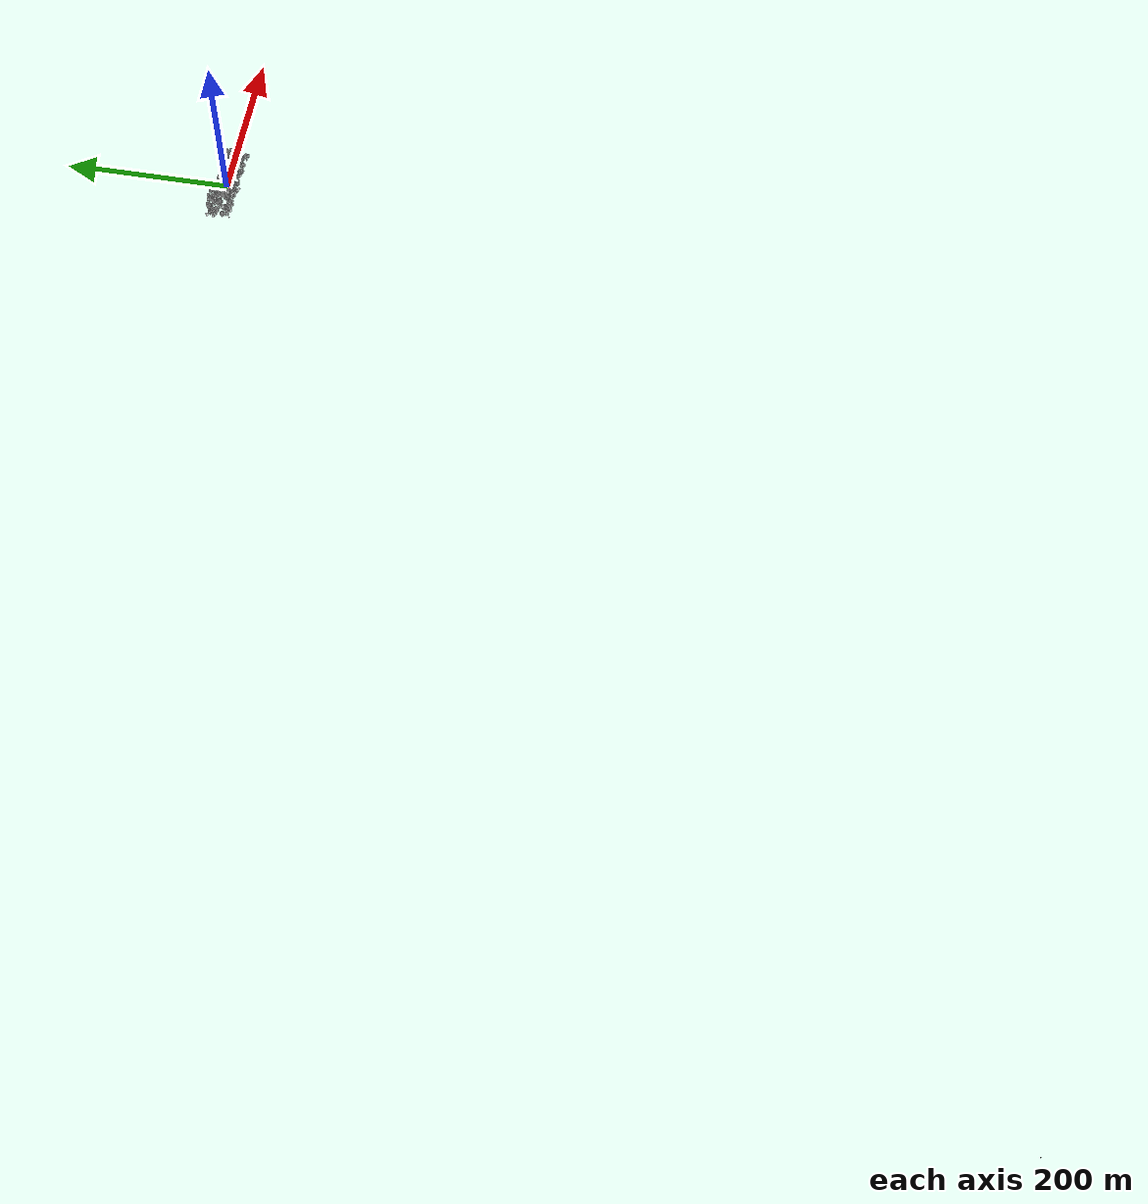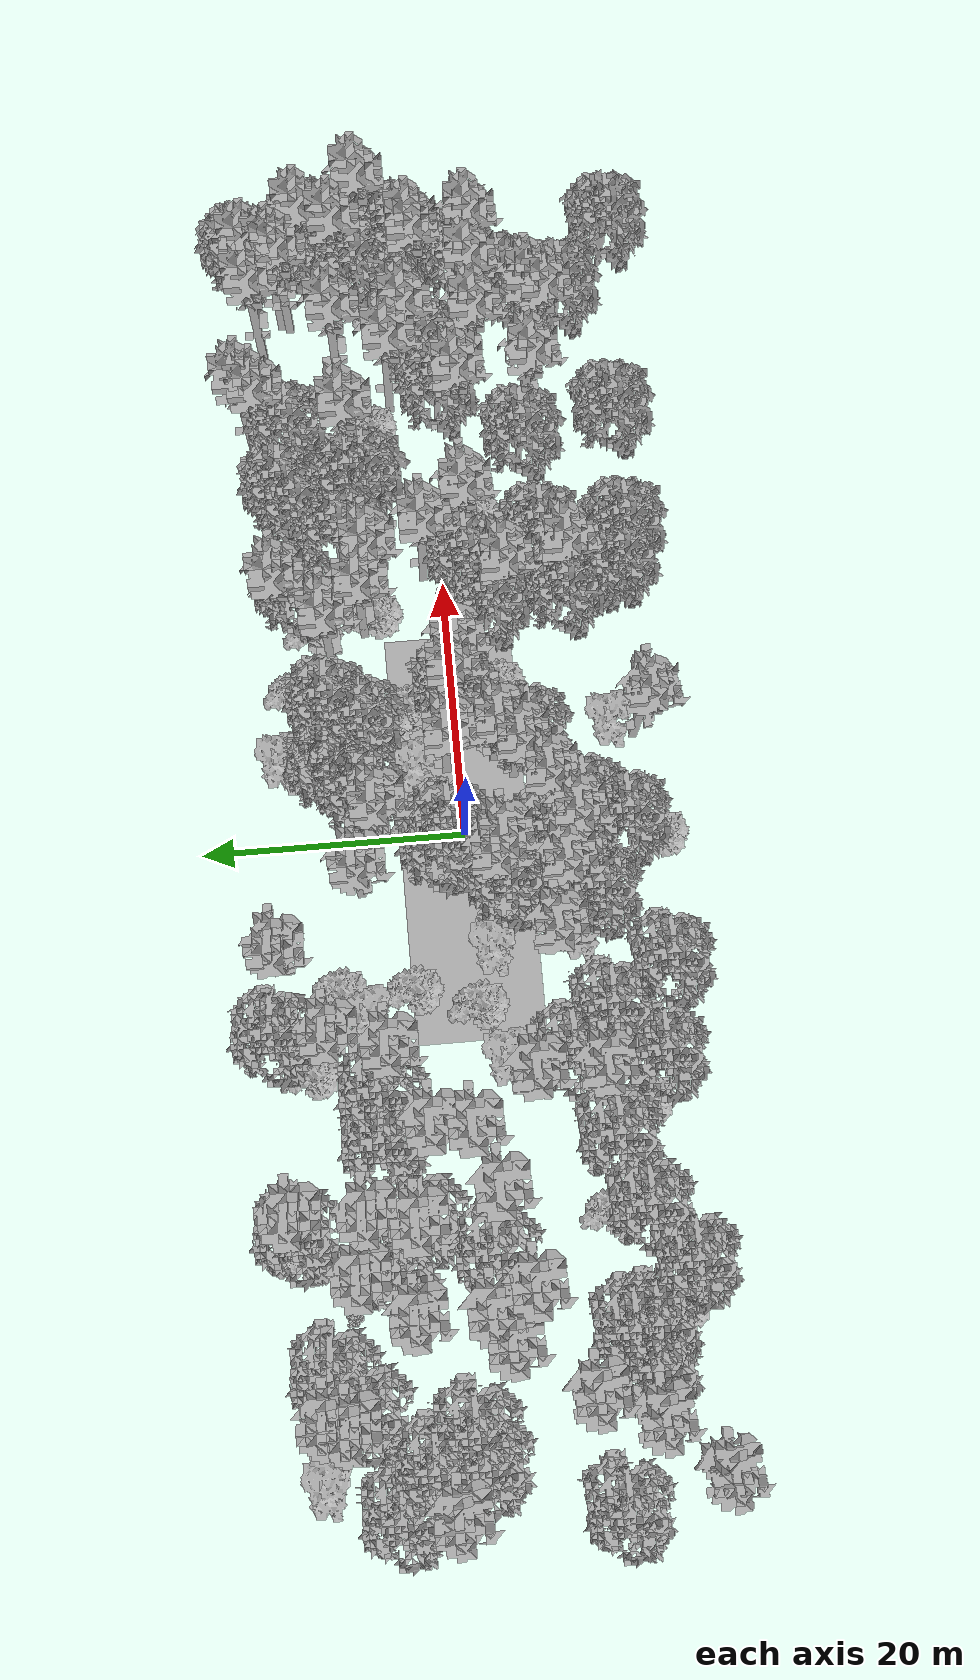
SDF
<sdf version="1.7">
    <world name="default">
        <plugin name="mrs_gazebo_static_transform_republisher_plugin" filename="libMrsGazeboCommonResources_StaticTransformRepublisher.so"/>
        <spherical_coordinates>
            <surface_model>EARTH_WGS84</surface_model>
            <latitude_deg>47.3977</latitude_deg>
            <longitude_deg>8.54559</longitude_deg>
            <elevation>0</elevation>
            <heading_deg>0</heading_deg>
        </spherical_coordinates>
        <physics name="default_physics" default="0" type="ode">
            <ode>
                <solver>
                    <type>quick</type>
                    <iters>10</iters>
                    <sor>1.3</sor>
                    <use_dynamic_moi_rescaling>0</use_dynamic_moi_rescaling>
                </solver>
                <constraints>
                    <cfm>0</cfm>
                    <erp>0.2</erp>
                    <contact_max_correcting_vel>1000</contact_max_correcting_vel>
                    <contact_surface_layer>0.001</contact_surface_layer>
                </constraints>
            </ode>
            <max_step_size>0.004</max_step_size>
            <real_time_factor>1</real_time_factor>
            <real_time_update_rate>250</real_time_update_rate>
        </physics>
        <scene>
            <shadows>0</shadows>
            <ambient>0.4 0.4 0.4 1</ambient>
            <background>0.7 0.7 0.7 1</background>
        </scene>
        <light name="sun" type="directional">
            <pose>0 0 1000 0.4 0.2 0</pose>
            <diffuse>1 1 1 1</diffuse>
            <specular>0.6 0.6 0.6 1</specular>
            <direction>0.1 0.1 -0.9</direction>
            <attenuation>
                <range>20</range>
                <constant>0.5</constant>
                <linear>0.01</linear>
                <quadratic>0.001</quadratic>
            </attenuation>
            <cast_shadows>1</cast_shadows>
            <spot>
                <inner_angle>0</inner_angle>
                <outer_angle>0</outer_angle>
                <falloff>0</falloff>
            </spot>
        </light>
        <model name="ground_plane">
            <static>1</static>
            <link name="link">
                <collision name="collision">
                    <pose>-50 0 0 0 -0 0</pose>
                    <geometry>
                        <plane>
                            <normal>0 0 1</normal>
                            <size>100 100</size>
                        </plane>
                    </geometry>
                    <surface>
                        <contact>
                            <ode>
                                <min_depth>0.01</min_depth>
                                <max_vel>0</max_vel>
                            </ode>
                        </contact>
                        <friction>
                            <ode/>
                            <torsional>
                                <ode/>
                            </torsional>
                        </friction>
                        <bounce/>
                    </surface>
                    <max_contacts>10</max_contacts>
                </collision>
                <visual name="grass">
                    <pose>0 0 0 0 -0 0</pose>
                    <cast_shadows>0</cast_shadows>
                    <geometry>
                        <mesh>
                            <scale>0.5814285714285714 0.18142857142857144 0.1</scale>
                            <uri>file://grass_plane/meshes/grass_plane.dae</uri>
                        </mesh>
                    </geometry>
                </visual>
                <self_collide>0</self_collide>
                <enable_wind>0</enable_wind>
                <kinematic>0</kinematic>
            </link>
        </model>
        <model name="the_void">
            <static>1</static>
            <link name="link">
                <pose>0 0 0.1 0 -0 0</pose>
                <visual name="the_void">
                    <pose>0 0 2 0 -0 0</pose>
                    <geometry>
                        <sphere>
                            <radius>0.25</radius>
                        </sphere>
                    </geometry>
                    <material>
                        <script>
                            <uri>file://media/materials/scripts/Gazebo.material</uri>
                            <name>Gazebo/Black</name>
                        </script>
                    </material>
                </visual>
                <self_collide>0</self_collide>
                <enable_wind>0</enable_wind>
                <kinematic>0</kinematic>
            </link>
            <pose>-1000 -1000 0 0 -0 0</pose>
        </model>
        <gui fullscreen="0">
            <camera name="camera">
                <pose>35.1577 98.6044 40.0204 0 0.407996 -1.99761</pose>
                <view_controller>orbit</view_controller>
                <projection_type>perspective</projection_type>
            </camera>
        </gui>
        <plugin name="mrs_gazebo_rviz_cam_synchronizer" filename="libMrsGazeboCommonResources_RvizCameraSynchronizer.so">
            <target_frame_id>gazebo_user_camera</target_frame_id>
            <world_origin_frame_id>uav1/gps_origin</world_origin_frame_id>
            <frame_to_follow>uav1</frame_to_follow>
        </plugin>
        <gravity>0 0 -9.8066</gravity>
        <magnetic_field>6e-06 2.3e-05 -4.2e-05</magnetic_field>
        <atmosphere type="adiabatic"/>
        <wind/>
        <model name="Tree 0">
            <static>1</static>
            <pose>-6.158259800889283 -8.98808349845068 0 1.57079 -0 0</pose>
            <link name="link">
                <pose>0 0 0 0 -0 0</pose>
                <collision name="collision">
                    <geometry>
                        <mesh>
                            <scale>3.5 5 3.5</scale>
                            <uri>model://tree_2/meshes/tree_2.obj</uri>
                        </mesh>
                    </geometry>
                    <max_contacts>10</max_contacts>
                    <surface>
                        <contact>
                            <ode/>
                        </contact>
                        <bounce/>
                        <friction>
                            <torsional>
                                <ode/>
                            </torsional>
                            <ode/>
                        </friction>
                    </surface>
                </collision>
                <visual name="visual">
                    <geometry>
                        <mesh>
                            <scale>3.5 5 3.5</scale>
                            <uri>model://tree_2/meshes/tree_2.obj</uri>
                        </mesh>
                    </geometry>
                </visual>
                <self_collide>0</self_collide>
                <enable_wind>0</enable_wind>
                <kinematic>0</kinematic>
            </link>
        </model>
        <model name="Tree 1">
            <static>1</static>
            <pose>-14.95214326042474 12.86118347821349 0 1.57079 -0 0</pose>
            <link name="link">
                <pose>0 0 0 0 -0 0</pose>
                <collision name="collision">
                    <geometry>
                        <mesh>
                            <scale>4 2.5 4</scale>
                            <uri>model://tree_1/meshes/tree_1.obj</uri>
                        </mesh>
                    </geometry>
                    <max_contacts>10</max_contacts>
                    <surface>
                        <contact>
                            <ode/>
                        </contact>
                        <bounce/>
                        <friction>
                            <torsional>
                                <ode/>
                            </torsional>
                            <ode/>
                        </friction>
                    </surface>
                </collision>
                <visual name="visual">
                    <geometry>
                        <mesh>
                            <scale>4 2.5 4</scale>
                            <uri>model://tree_1/meshes/tree_1.obj</uri>
                        </mesh>
                    </geometry>
                </visual>
                <self_collide>0</self_collide>
                <enable_wind>0</enable_wind>
                <kinematic>0</kinematic>
            </link>
        </model>
        <model name="Tree 2">
            <static>1</static>
            <pose>45.38698988461415 1.1021665377766503 0 1.57079 -0 0</pose>
            <link name="link">
                <pose>0 0 0 0 -0 0</pose>
                <collision name="collision">
                    <geometry>
                        <mesh>
                            <scale>3.5 5 3.5</scale>
                            <uri>model://tree_2/meshes/tree_2.obj</uri>
                        </mesh>
                    </geometry>
                    <max_contacts>10</max_contacts>
                    <surface>
                        <contact>
                            <ode/>
                        </contact>
                        <bounce/>
                        <friction>
                            <torsional>
                                <ode/>
                            </torsional>
                            <ode/>
                        </friction>
                    </surface>
                </collision>
                <visual name="visual">
                    <geometry>
                        <mesh>
                            <scale>3.5 5 3.5</scale>
                            <uri>model://tree_2/meshes/tree_2.obj</uri>
                        </mesh>
                    </geometry>
                </visual>
                <self_collide>0</self_collide>
                <enable_wind>0</enable_wind>
                <kinematic>0</kinematic>
            </link>
        </model>
        <model name="Tree 3">
            <static>1</static>
            <pose>-31.481385527673343 7.390100889595605 0 1.57079 -0 0</pose>
            <link name="link">
                <pose>0 0 0 0 -0 0</pose>
                <collision name="collision">
                    <geometry>
                        <mesh>
                            <scale>3.5 5 3.5</scale>
                            <uri>model://tree_2/meshes/tree_2.obj</uri>
                        </mesh>
                    </geometry>
                    <max_contacts>10</max_contacts>
                    <surface>
                        <contact>
                            <ode/>
                        </contact>
                        <bounce/>
                        <friction>
                            <torsional>
                                <ode/>
                            </torsional>
                            <ode/>
                        </friction>
                    </surface>
                </collision>
                <visual name="visual">
                    <geometry>
                        <mesh>
                            <scale>3.5 5 3.5</scale>
                            <uri>model://tree_2/meshes/tree_2.obj</uri>
                        </mesh>
                    </geometry>
                </visual>
                <self_collide>0</self_collide>
                <enable_wind>0</enable_wind>
                <kinematic>0</kinematic>
            </link>
        </model>
        <model name="Tree 4">
            <static>1</static>
            <pose>5.58407054845911 3.052981912878497 0 1.57079 -0 0</pose>
            <link name="link">
                <pose>0 0 0 0 -0 0</pose>
                <collision name="collision">
                    <geometry>
                        <mesh>
                            <scale>3 2 3</scale>
                            <uri>model://tree_3/meshes/tree_3.obj</uri>
                        </mesh>
                    </geometry>
                    <max_contacts>10</max_contacts>
                    <surface>
                        <contact>
                            <ode/>
                        </contact>
                        <bounce/>
                        <friction>
                            <torsional>
                                <ode/>
                            </torsional>
                            <ode/>
                        </friction>
                    </surface>
                </collision>
                <visual name="visual">
                    <geometry>
                        <mesh>
                            <scale>3 2 3</scale>
                            <uri>model://tree_3/meshes/tree_3.obj</uri>
                        </mesh>
                    </geometry>
                </visual>
                <self_collide>0</self_collide>
                <enable_wind>0</enable_wind>
                <kinematic>0</kinematic>
            </link>
        </model>
        <model name="Tree 5">
            <static>1</static>
            <pose>4.440106754375051 -4.174271067530999 0 1.57079 -0 0</pose>
            <link name="link">
                <pose>0 0 0 0 -0 0</pose>
                <collision name="collision">
                    <geometry>
                        <mesh>
                            <scale>3.5 5 3.5</scale>
                            <uri>model://tree_9/meshes/tree_9.obj</uri>
                        </mesh>
                    </geometry>
                    <max_contacts>10</max_contacts>
                    <surface>
                        <contact>
                            <ode/>
                        </contact>
                        <bounce/>
                        <friction>
                            <torsional>
                                <ode/>
                            </torsional>
                            <ode/>
                        </friction>
                    </surface>
                </collision>
                <visual name="visual">
                    <geometry>
                        <mesh>
                            <scale>3.5 5 3.5</scale>
                            <uri>model://tree_9/meshes/tree_9.obj</uri>
                        </mesh>
                    </geometry>
                </visual>
                <self_collide>0</self_collide>
                <enable_wind>0</enable_wind>
                <kinematic>0</kinematic>
            </link>
        </model>
        <model name="Tree 6">
            <static>1</static>
            <pose>44.363141829020776 0.558316381607467 0 1.57079 -0 0</pose>
            <link name="link">
                <pose>0 0 0 0 -0 0</pose>
                <collision name="collision">
                    <geometry>
                        <mesh>
                            <scale>3.5 5 3.5</scale>
                            <uri>model://tree_9/meshes/tree_9.obj</uri>
                        </mesh>
                    </geometry>
                    <max_contacts>10</max_contacts>
                    <surface>
                        <contact>
                            <ode/>
                        </contact>
                        <bounce/>
                        <friction>
                            <torsional>
                                <ode/>
                            </torsional>
                            <ode/>
                        </friction>
                    </surface>
                </collision>
                <visual name="visual">
                    <geometry>
                        <mesh>
                            <scale>3.5 5 3.5</scale>
                            <uri>model://tree_9/meshes/tree_9.obj</uri>
                        </mesh>
                    </geometry>
                </visual>
                <self_collide>0</self_collide>
                <enable_wind>0</enable_wind>
                <kinematic>0</kinematic>
            </link>
        </model>
        <model name="Tree 7">
            <static>1</static>
            <pose>47.19614981732464 8.263385943300001 0 1.57079 -0 0</pose>
            <link name="link">
                <pose>0 0 0 0 -0 0</pose>
                <collision name="collision">
                    <geometry>
                        <mesh>
                            <scale>3.5 5 3.5</scale>
                            <uri>model://tree_2/meshes/tree_2.obj</uri>
                        </mesh>
                    </geometry>
                    <max_contacts>10</max_contacts>
                    <surface>
                        <contact>
                            <ode/>
                        </contact>
                        <bounce/>
                        <friction>
                            <torsional>
                                <ode/>
                            </torsional>
                            <ode/>
                        </friction>
                    </surface>
                </collision>
                <visual name="visual">
                    <geometry>
                        <mesh>
                            <scale>3.5 5 3.5</scale>
                            <uri>model://tree_2/meshes/tree_2.obj</uri>
                        </mesh>
                    </geometry>
                </visual>
                <self_collide>0</self_collide>
                <enable_wind>0</enable_wind>
                <kinematic>0</kinematic>
            </link>
        </model>
        <model name="Tree 8">
            <static>1</static>
            <pose>-34.72252910490241 6.281720493063954 0 1.57079 -0 0</pose>
            <link name="link">
                <pose>0 0 0 0 -0 0</pose>
                <collision name="collision">
                    <geometry>
                        <mesh>
                            <scale>3.5 5 3.5</scale>
                            <uri>model://tree_9/meshes/tree_9.obj</uri>
                        </mesh>
                    </geometry>
                    <max_contacts>10</max_contacts>
                    <surface>
                        <contact>
                            <ode/>
                        </contact>
                        <bounce/>
                        <friction>
                            <torsional>
                                <ode/>
                            </torsional>
                            <ode/>
                        </friction>
                    </surface>
                </collision>
                <visual name="visual">
                    <geometry>
                        <mesh>
                            <scale>3.5 5 3.5</scale>
                            <uri>model://tree_9/meshes/tree_9.obj</uri>
                        </mesh>
                    </geometry>
                </visual>
                <self_collide>0</self_collide>
                <enable_wind>0</enable_wind>
                <kinematic>0</kinematic>
            </link>
        </model>
        <model name="Tree 9">
            <static>1</static>
            <pose>-36.51045037347647 -9.925831288126538 0 1.57079 -0 0</pose>
            <link name="link">
                <pose>0 0 0 0 -0 0</pose>
                <collision name="collision">
                    <geometry>
                        <mesh>
                            <scale>3.5 5 3.5</scale>
                            <uri>model://tree_2/meshes/tree_2.obj</uri>
                        </mesh>
                    </geometry>
                    <max_contacts>10</max_contacts>
                    <surface>
                        <contact>
                            <ode/>
                        </contact>
                        <bounce/>
                        <friction>
                            <torsional>
                                <ode/>
                            </torsional>
                            <ode/>
                        </friction>
                    </surface>
                </collision>
                <visual name="visual">
                    <geometry>
                        <mesh>
                            <scale>3.5 5 3.5</scale>
                            <uri>model://tree_2/meshes/tree_2.obj</uri>
                        </mesh>
                    </geometry>
                </visual>
                <self_collide>0</self_collide>
                <enable_wind>0</enable_wind>
                <kinematic>0</kinematic>
            </link>
        </model>
        <model name="Tree 10">
            <static>1</static>
            <pose>9.207565093119584 9.432502181089014 0 1.57079 -0 0</pose>
            <link name="link">
                <pose>0 0 0 0 -0 0</pose>
                <collision name="collision">
                    <geometry>
                        <mesh>
                            <scale>3.5 5 3.5</scale>
                            <uri>model://tree_2/meshes/tree_2.obj</uri>
                        </mesh>
                    </geometry>
                    <max_contacts>10</max_contacts>
                    <surface>
                        <contact>
                            <ode/>
                        </contact>
                        <bounce/>
                        <friction>
                            <torsional>
                                <ode/>
                            </torsional>
                            <ode/>
                        </friction>
                    </surface>
                </collision>
                <visual name="visual">
                    <geometry>
                        <mesh>
                            <scale>3.5 5 3.5</scale>
                            <uri>model://tree_2/meshes/tree_2.obj</uri>
                        </mesh>
                    </geometry>
                </visual>
                <self_collide>0</self_collide>
                <enable_wind>0</enable_wind>
                <kinematic>0</kinematic>
            </link>
        </model>
        <model name="Tree 11">
            <static>1</static>
            <pose>-48.516853860675 -6.801275732537819 0 1.57079 -0 0</pose>
            <link name="link">
                <pose>0 0 0 0 -0 0</pose>
                <collision name="collision">
                    <geometry>
                        <mesh>
                            <scale>3.5 5 3.5</scale>
                            <uri>model://tree_2/meshes/tree_2.obj</uri>
                        </mesh>
                    </geometry>
                    <max_contacts>10</max_contacts>
                    <surface>
                        <contact>
                            <ode/>
                        </contact>
                        <bounce/>
                        <friction>
                            <torsional>
                                <ode/>
                            </torsional>
                            <ode/>
                        </friction>
                    </surface>
                </collision>
                <visual name="visual">
                    <geometry>
                        <mesh>
                            <scale>3.5 5 3.5</scale>
                            <uri>model://tree_2/meshes/tree_2.obj</uri>
                        </mesh>
                    </geometry>
                </visual>
                <self_collide>0</self_collide>
                <enable_wind>0</enable_wind>
                <kinematic>0</kinematic>
            </link>
        </model>
        <model name="Tree 12">
            <static>1</static>
            <pose>21.025856287350308 1.3842964651900367 0 1.57079 -0 0</pose>
            <link name="link">
                <pose>0 0 0 0 -0 0</pose>
                <collision name="collision">
                    <geometry>
                        <mesh>
                            <scale>3.5 5 3.5</scale>
                            <uri>model://tree_9/meshes/tree_9.obj</uri>
                        </mesh>
                    </geometry>
                    <max_contacts>10</max_contacts>
                    <surface>
                        <contact>
                            <ode/>
                        </contact>
                        <bounce/>
                        <friction>
                            <torsional>
                                <ode/>
                            </torsional>
                            <ode/>
                        </friction>
                    </surface>
                </collision>
                <visual name="visual">
                    <geometry>
                        <mesh>
                            <scale>3.5 5 3.5</scale>
                            <uri>model://tree_9/meshes/tree_9.obj</uri>
                        </mesh>
                    </geometry>
                </visual>
                <self_collide>0</self_collide>
                <enable_wind>0</enable_wind>
                <kinematic>0</kinematic>
            </link>
        </model>
        <model name="Tree 13">
            <static>1</static>
            <pose>-28.541274599776546 -10.350069301686885 0 1.57079 -0 0</pose>
            <link name="link">
                <pose>0 0 0 0 -0 0</pose>
                <collision name="collision">
                    <geometry>
                        <mesh>
                            <scale>3.5 5 3.5</scale>
                            <uri>model://tree_2/meshes/tree_2.obj</uri>
                        </mesh>
                    </geometry>
                    <max_contacts>10</max_contacts>
                    <surface>
                        <contact>
                            <ode/>
                        </contact>
                        <bounce/>
                        <friction>
                            <torsional>
                                <ode/>
                            </torsional>
                            <ode/>
                        </friction>
                    </surface>
                </collision>
                <visual name="visual">
                    <geometry>
                        <mesh>
                            <scale>3.5 5 3.5</scale>
                            <uri>model://tree_2/meshes/tree_2.obj</uri>
                        </mesh>
                    </geometry>
                </visual>
                <self_collide>0</self_collide>
                <enable_wind>0</enable_wind>
                <kinematic>0</kinematic>
            </link>
        </model>
        <model name="Tree 14">
            <static>1</static>
            <pose>-40.880451458060946 12.764865354557013 0 1.57079 -0 0</pose>
            <link name="link">
                <pose>0 0 0 0 -0 0</pose>
                <collision name="collision">
                    <geometry>
                        <mesh>
                            <scale>3.5 5 3.5</scale>
                            <uri>model://tree_9/meshes/tree_9.obj</uri>
                        </mesh>
                    </geometry>
                    <max_contacts>10</max_contacts>
                    <surface>
                        <contact>
                            <ode/>
                        </contact>
                        <bounce/>
                        <friction>
                            <torsional>
                                <ode/>
                            </torsional>
                            <ode/>
                        </friction>
                    </surface>
                </collision>
                <visual name="visual">
                    <geometry>
                        <mesh>
                            <scale>3.5 5 3.5</scale>
                            <uri>model://tree_9/meshes/tree_9.obj</uri>
                        </mesh>
                    </geometry>
                </visual>
                <self_collide>0</self_collide>
                <enable_wind>0</enable_wind>
                <kinematic>0</kinematic>
            </link>
        </model>
        <model name="Tree 15">
            <static>1</static>
            <pose>-22.051231511386494 4.27168029875806 0 1.57079 -0 0</pose>
            <link name="link">
                <pose>0 0 0 0 -0 0</pose>
                <collision name="collision">
                    <geometry>
                        <mesh>
                            <scale>3.5 5 3.5</scale>
                            <uri>model://tree_9/meshes/tree_9.obj</uri>
                        </mesh>
                    </geometry>
                    <max_contacts>10</max_contacts>
                    <surface>
                        <contact>
                            <ode/>
                        </contact>
                        <bounce/>
                        <friction>
                            <torsional>
                                <ode/>
                            </torsional>
                            <ode/>
                        </friction>
                    </surface>
                </collision>
                <visual name="visual">
                    <geometry>
                        <mesh>
                            <scale>3.5 5 3.5</scale>
                            <uri>model://tree_9/meshes/tree_9.obj</uri>
                        </mesh>
                    </geometry>
                </visual>
                <self_collide>0</self_collide>
                <enable_wind>0</enable_wind>
                <kinematic>0</kinematic>
            </link>
        </model>
        <model name="Tree 16">
            <static>1</static>
            <pose>8.469443120652137 5.244132896557197 0 1.57079 -0 0</pose>
            <link name="link">
                <pose>0 0 0 0 -0 0</pose>
                <collision name="collision">
                    <geometry>
                        <mesh>
                            <scale>4 2.5 4</scale>
                            <uri>model://tree_1/meshes/tree_1.obj</uri>
                        </mesh>
                    </geometry>
                    <max_contacts>10</max_contacts>
                    <surface>
                        <contact>
                            <ode/>
                        </contact>
                        <bounce/>
                        <friction>
                            <torsional>
                                <ode/>
                            </torsional>
                            <ode/>
                        </friction>
                    </surface>
                </collision>
                <visual name="visual">
                    <geometry>
                        <mesh>
                            <scale>4 2.5 4</scale>
                            <uri>model://tree_1/meshes/tree_1.obj</uri>
                        </mesh>
                    </geometry>
                </visual>
                <self_collide>0</self_collide>
                <enable_wind>0</enable_wind>
                <kinematic>0</kinematic>
            </link>
        </model>
        <model name="Tree 17">
            <static>1</static>
            <pose>-30.91629413074486 0.5587436162132704 0 1.57079 -0 0</pose>
            <link name="link">
                <pose>0 0 0 0 -0 0</pose>
                <collision name="collision">
                    <geometry>
                        <mesh>
                            <scale>3.5 5 3.5</scale>
                            <uri>model://tree_2/meshes/tree_2.obj</uri>
                        </mesh>
                    </geometry>
                    <max_contacts>10</max_contacts>
                    <surface>
                        <contact>
                            <ode/>
                        </contact>
                        <bounce/>
                        <friction>
                            <torsional>
                                <ode/>
                            </torsional>
                            <ode/>
                        </friction>
                    </surface>
                </collision>
                <visual name="visual">
                    <geometry>
                        <mesh>
                            <scale>3.5 5 3.5</scale>
                            <uri>model://tree_2/meshes/tree_2.obj</uri>
                        </mesh>
                    </geometry>
                </visual>
                <self_collide>0</self_collide>
                <enable_wind>0</enable_wind>
                <kinematic>0</kinematic>
            </link>
        </model>
        <model name="Tree 18">
            <static>1</static>
            <pose>44.79083676963218 -0.20597438506012722 0 1.57079 -0 0</pose>
            <link name="link">
                <pose>0 0 0 0 -0 0</pose>
                <collision name="collision">
                    <geometry>
                        <mesh>
                            <scale>3 2 3</scale>
                            <uri>model://tree_3/meshes/tree_3.obj</uri>
                        </mesh>
                    </geometry>
                    <max_contacts>10</max_contacts>
                    <surface>
                        <contact>
                            <ode/>
                        </contact>
                        <bounce/>
                        <friction>
                            <torsional>
                                <ode/>
                            </torsional>
                            <ode/>
                        </friction>
                    </surface>
                </collision>
                <visual name="visual">
                    <geometry>
                        <mesh>
                            <scale>3 2 3</scale>
                            <uri>model://tree_3/meshes/tree_3.obj</uri>
                        </mesh>
                    </geometry>
                </visual>
                <self_collide>0</self_collide>
                <enable_wind>0</enable_wind>
                <kinematic>0</kinematic>
            </link>
        </model>
        <model name="Tree 19">
            <static>1</static>
            <pose>43.74474452205713 0.48922184363445176 0 1.57079 -0 0</pose>
            <link name="link">
                <pose>0 0 0 0 -0 0</pose>
                <collision name="collision">
                    <geometry>
                        <mesh>
                            <scale>3.5 5 3.5</scale>
                            <uri>model://tree_9/meshes/tree_9.obj</uri>
                        </mesh>
                    </geometry>
                    <max_contacts>10</max_contacts>
                    <surface>
                        <contact>
                            <ode/>
                        </contact>
                        <bounce/>
                        <friction>
                            <torsional>
                                <ode/>
                            </torsional>
                            <ode/>
                        </friction>
                    </surface>
                </collision>
                <visual name="visual">
                    <geometry>
                        <mesh>
                            <scale>3.5 5 3.5</scale>
                            <uri>model://tree_9/meshes/tree_9.obj</uri>
                        </mesh>
                    </geometry>
                </visual>
                <self_collide>0</self_collide>
                <enable_wind>0</enable_wind>
                <kinematic>0</kinematic>
            </link>
        </model>
        <model name="Tree 20">
            <static>1</static>
            <pose>43.586952294607 12.798136278993798 0 1.57079 -0 0</pose>
            <link name="link">
                <pose>0 0 0 0 -0 0</pose>
                <collision name="collision">
                    <geometry>
                        <mesh>
                            <scale>3.5 5 3.5</scale>
                            <uri>model://tree_9/meshes/tree_9.obj</uri>
                        </mesh>
                    </geometry>
                    <max_contacts>10</max_contacts>
                    <surface>
                        <contact>
                            <ode/>
                        </contact>
                        <bounce/>
                        <friction>
                            <torsional>
                                <ode/>
                            </torsional>
                            <ode/>
                        </friction>
                    </surface>
                </collision>
                <visual name="visual">
                    <geometry>
                        <mesh>
                            <scale>3.5 5 3.5</scale>
                            <uri>model://tree_9/meshes/tree_9.obj</uri>
                        </mesh>
                    </geometry>
                </visual>
                <self_collide>0</self_collide>
                <enable_wind>0</enable_wind>
                <kinematic>0</kinematic>
            </link>
        </model>
        <model name="Tree 21">
            <static>1</static>
            <pose>40.45998238796628 -10.520547793926774 0 1.57079 -0 0</pose>
            <link name="link">
                <pose>0 0 0 0 -0 0</pose>
                <collision name="collision">
                    <geometry>
                        <mesh>
                            <scale>3.5 5 3.5</scale>
                            <uri>model://tree_2/meshes/tree_2.obj</uri>
                        </mesh>
                    </geometry>
                    <max_contacts>10</max_contacts>
                    <surface>
                        <contact>
                            <ode/>
                        </contact>
                        <bounce/>
                        <friction>
                            <torsional>
                                <ode/>
                            </torsional>
                            <ode/>
                        </friction>
                    </surface>
                </collision>
                <visual name="visual">
                    <geometry>
                        <mesh>
                            <scale>3.5 5 3.5</scale>
                            <uri>model://tree_2/meshes/tree_2.obj</uri>
                        </mesh>
                    </geometry>
                </visual>
                <self_collide>0</self_collide>
                <enable_wind>0</enable_wind>
                <kinematic>0</kinematic>
            </link>
        </model>
        <model name="Tree 22">
            <static>1</static>
            <pose>0.5068303792683722 -8.481424559732355 0 1.57079 -0 0</pose>
            <link name="link">
                <pose>0 0 0 0 -0 0</pose>
                <collision name="collision">
                    <geometry>
                        <mesh>
                            <scale>3.5 5 3.5</scale>
                            <uri>model://tree_2/meshes/tree_2.obj</uri>
                        </mesh>
                    </geometry>
                    <max_contacts>10</max_contacts>
                    <surface>
                        <contact>
                            <ode/>
                        </contact>
                        <bounce/>
                        <friction>
                            <torsional>
                                <ode/>
                            </torsional>
                            <ode/>
                        </friction>
                    </surface>
                </collision>
                <visual name="visual">
                    <geometry>
                        <mesh>
                            <scale>3.5 5 3.5</scale>
                            <uri>model://tree_2/meshes/tree_2.obj</uri>
                        </mesh>
                    </geometry>
                </visual>
                <self_collide>0</self_collide>
                <enable_wind>0</enable_wind>
                <kinematic>0</kinematic>
            </link>
        </model>
        <model name="Tree 23">
            <static>1</static>
            <pose>-17.553101795031015 -6.1093200136517005 0 1.57079 -0 0</pose>
            <link name="link">
                <pose>0 0 0 0 -0 0</pose>
                <collision name="collision">
                    <geometry>
                        <mesh>
                            <scale>3.5 5 3.5</scale>
                            <uri>model://tree_2/meshes/tree_2.obj</uri>
                        </mesh>
                    </geometry>
                    <max_contacts>10</max_contacts>
                    <surface>
                        <contact>
                            <ode/>
                        </contact>
                        <bounce/>
                        <friction>
                            <torsional>
                                <ode/>
                            </torsional>
                            <ode/>
                        </friction>
                    </surface>
                </collision>
                <visual name="visual">
                    <geometry>
                        <mesh>
                            <scale>3.5 5 3.5</scale>
                            <uri>model://tree_2/meshes/tree_2.obj</uri>
                        </mesh>
                    </geometry>
                </visual>
                <self_collide>0</self_collide>
                <enable_wind>0</enable_wind>
                <kinematic>0</kinematic>
            </link>
        </model>
        <model name="Tree 24">
            <static>1</static>
            <pose>-11.590597687950584 -13.634750835188747 0 1.57079 -0 0</pose>
            <link name="link">
                <pose>0 0 0 0 -0 0</pose>
                <collision name="collision">
                    <geometry>
                        <mesh>
                            <scale>3.5 5 3.5</scale>
                            <uri>model://tree_2/meshes/tree_2.obj</uri>
                        </mesh>
                    </geometry>
                    <max_contacts>10</max_contacts>
                    <surface>
                        <contact>
                            <ode/>
                        </contact>
                        <bounce/>
                        <friction>
                            <torsional>
                                <ode/>
                            </torsional>
                            <ode/>
                        </friction>
                    </surface>
                </collision>
                <visual name="visual">
                    <geometry>
                        <mesh>
                            <scale>3.5 5 3.5</scale>
                            <uri>model://tree_2/meshes/tree_2.obj</uri>
                        </mesh>
                    </geometry>
                </visual>
                <self_collide>0</self_collide>
                <enable_wind>0</enable_wind>
                <kinematic>0</kinematic>
            </link>
        </model>
        <model name="Tree 25">
            <static>1</static>
            <pose>-2.526162246297069 -2.372710406290759 0 1.57079 -0 0</pose>
            <link name="link">
                <pose>0 0 0 0 -0 0</pose>
                <collision name="collision">
                    <geometry>
                        <mesh>
                            <scale>3.5 5 3.5</scale>
                            <uri>model://tree_9/meshes/tree_9.obj</uri>
                        </mesh>
                    </geometry>
                    <max_contacts>10</max_contacts>
                    <surface>
                        <contact>
                            <ode/>
                        </contact>
                        <bounce/>
                        <friction>
                            <torsional>
                                <ode/>
                            </torsional>
                            <ode/>
                        </friction>
                    </surface>
                </collision>
                <visual name="visual">
                    <geometry>
                        <mesh>
                            <scale>3.5 5 3.5</scale>
                            <uri>model://tree_9/meshes/tree_9.obj</uri>
                        </mesh>
                    </geometry>
                </visual>
                <self_collide>0</self_collide>
                <enable_wind>0</enable_wind>
                <kinematic>0</kinematic>
            </link>
        </model>
        <model name="Tree 26">
            <static>1</static>
            <pose>38.31958006728536 -8.912998692593735 0 1.57079 -0 0</pose>
            <link name="link">
                <pose>0 0 0 0 -0 0</pose>
                <collision name="collision">
                    <geometry>
                        <mesh>
                            <scale>3.5 5 3.5</scale>
                            <uri>model://tree_9/meshes/tree_9.obj</uri>
                        </mesh>
                    </geometry>
                    <max_contacts>10</max_contacts>
                    <surface>
                        <contact>
                            <ode/>
                        </contact>
                        <bounce/>
                        <friction>
                            <torsional>
                                <ode/>
                            </torsional>
                            <ode/>
                        </friction>
                    </surface>
                </collision>
                <visual name="visual">
                    <geometry>
                        <mesh>
                            <scale>3.5 5 3.5</scale>
                            <uri>model://tree_9/meshes/tree_9.obj</uri>
                        </mesh>
                    </geometry>
                </visual>
                <self_collide>0</self_collide>
                <enable_wind>0</enable_wind>
                <kinematic>0</kinematic>
            </link>
        </model>
        <model name="Tree 27">
            <static>1</static>
            <pose>45.05268947053895 9.139568104182967 0 1.57079 -0 0</pose>
            <link name="link">
                <pose>0 0 0 0 -0 0</pose>
                <collision name="collision">
                    <geometry>
                        <mesh>
                            <scale>3.5 5 3.5</scale>
                            <uri>model://tree_2/meshes/tree_2.obj</uri>
                        </mesh>
                    </geometry>
                    <max_contacts>10</max_contacts>
                    <surface>
                        <contact>
                            <ode/>
                        </contact>
                        <bounce/>
                        <friction>
                            <torsional>
                                <ode/>
                            </torsional>
                            <ode/>
                        </friction>
                    </surface>
                </collision>
                <visual name="visual">
                    <geometry>
                        <mesh>
                            <scale>3.5 5 3.5</scale>
                            <uri>model://tree_2/meshes/tree_2.obj</uri>
                        </mesh>
                    </geometry>
                </visual>
                <self_collide>0</self_collide>
                <enable_wind>0</enable_wind>
                <kinematic>0</kinematic>
            </link>
        </model>
        <model name="Tree 28">
            <static>1</static>
            <pose>25.04193544505364 -2.8722364656625743 0 1.57079 -0 0</pose>
            <link name="link">
                <pose>0 0 0 0 -0 0</pose>
                <collision name="collision">
                    <geometry>
                        <mesh>
                            <scale>4 2.5 4</scale>
                            <uri>model://tree_1/meshes/tree_1.obj</uri>
                        </mesh>
                    </geometry>
                    <max_contacts>10</max_contacts>
                    <surface>
                        <contact>
                            <ode/>
                        </contact>
                        <bounce/>
                        <friction>
                            <torsional>
                                <ode/>
                            </torsional>
                            <ode/>
                        </friction>
                    </surface>
                </collision>
                <visual name="visual">
                    <geometry>
                        <mesh>
                            <scale>4 2.5 4</scale>
                            <uri>model://tree_1/meshes/tree_1.obj</uri>
                        </mesh>
                    </geometry>
                </visual>
                <self_collide>0</self_collide>
                <enable_wind>0</enable_wind>
                <kinematic>0</kinematic>
            </link>
        </model>
        <model name="Tree 29">
            <static>1</static>
            <pose>32.859026506648405 4.661615741895513 0 1.57079 -0 0</pose>
            <link name="link">
                <pose>0 0 0 0 -0 0</pose>
                <collision name="collision">
                    <geometry>
                        <mesh>
                            <scale>4 2.5 4</scale>
                            <uri>model://tree_1/meshes/tree_1.obj</uri>
                        </mesh>
                    </geometry>
                    <max_contacts>10</max_contacts>
                    <surface>
                        <contact>
                            <ode/>
                        </contact>
                        <bounce/>
                        <friction>
                            <torsional>
                                <ode/>
                            </torsional>
                            <ode/>
                        </friction>
                    </surface>
                </collision>
                <visual name="visual">
                    <geometry>
                        <mesh>
                            <scale>4 2.5 4</scale>
                            <uri>model://tree_1/meshes/tree_1.obj</uri>
                        </mesh>
                    </geometry>
                </visual>
                <self_collide>0</self_collide>
                <enable_wind>0</enable_wind>
                <kinematic>0</kinematic>
            </link>
        </model>
        <model name="Tree 30">
            <static>1</static>
            <pose>19.5493914912514 -1.5999695103256109 0 1.57079 -0 0</pose>
            <link name="link">
                <pose>0 0 0 0 -0 0</pose>
                <collision name="collision">
                    <geometry>
                        <mesh>
                            <scale>3.5 5 3.5</scale>
                            <uri>model://tree_2/meshes/tree_2.obj</uri>
                        </mesh>
                    </geometry>
                    <max_contacts>10</max_contacts>
                    <surface>
                        <contact>
                            <ode/>
                        </contact>
                        <bounce/>
                        <friction>
                            <torsional>
                                <ode/>
                            </torsional>
                            <ode/>
                        </friction>
                    </surface>
                </collision>
                <visual name="visual">
                    <geometry>
                        <mesh>
                            <scale>3.5 5 3.5</scale>
                            <uri>model://tree_2/meshes/tree_2.obj</uri>
                        </mesh>
                    </geometry>
                </visual>
                <self_collide>0</self_collide>
                <enable_wind>0</enable_wind>
                <kinematic>0</kinematic>
            </link>
        </model>
        <model name="Tree 31">
            <static>1</static>
            <pose>43.629641944730366 4.848017975946856 0 1.57079 -0 0</pose>
            <link name="link">
                <pose>0 0 0 0 -0 0</pose>
                <collision name="collision">
                    <geometry>
                        <mesh>
                            <scale>3.5 5 3.5</scale>
                            <uri>model://tree_2/meshes/tree_2.obj</uri>
                        </mesh>
                    </geometry>
                    <max_contacts>10</max_contacts>
                    <surface>
                        <contact>
                            <ode/>
                        </contact>
                        <bounce/>
                        <friction>
                            <torsional>
                                <ode/>
                            </torsional>
                            <ode/>
                        </friction>
                    </surface>
                </collision>
                <visual name="visual">
                    <geometry>
                        <mesh>
                            <scale>3.5 5 3.5</scale>
                            <uri>model://tree_2/meshes/tree_2.obj</uri>
                        </mesh>
                    </geometry>
                </visual>
                <self_collide>0</self_collide>
                <enable_wind>0</enable_wind>
                <kinematic>0</kinematic>
            </link>
        </model>
        <model name="Tree 32">
            <static>1</static>
            <pose>-5.078672200318167 -5.466062343714581 0 1.57079 -0 0</pose>
            <link name="link">
                <pose>0 0 0 0 -0 0</pose>
                <collision name="collision">
                    <geometry>
                        <mesh>
                            <scale>3 2 3</scale>
                            <uri>model://tree_3/meshes/tree_3.obj</uri>
                        </mesh>
                    </geometry>
                    <max_contacts>10</max_contacts>
                    <surface>
                        <contact>
                            <ode/>
                        </contact>
                        <bounce/>
                        <friction>
                            <torsional>
                                <ode/>
                            </torsional>
                            <ode/>
                        </friction>
                    </surface>
                </collision>
                <visual name="visual">
                    <geometry>
                        <mesh>
                            <scale>3 2 3</scale>
                            <uri>model://tree_3/meshes/tree_3.obj</uri>
                        </mesh>
                    </geometry>
                </visual>
                <self_collide>0</self_collide>
                <enable_wind>0</enable_wind>
                <kinematic>0</kinematic>
            </link>
        </model>
        <model name="Tree 33">
            <static>1</static>
            <pose>-38.20391990140483 12.369561402918748 0 1.57079 -0 0</pose>
            <link name="link">
                <pose>0 0 0 0 -0 0</pose>
                <collision name="collision">
                    <geometry>
                        <mesh>
                            <scale>3.5 5 3.5</scale>
                            <uri>model://tree_2/meshes/tree_2.obj</uri>
                        </mesh>
                    </geometry>
                    <max_contacts>10</max_contacts>
                    <surface>
                        <contact>
                            <ode/>
                        </contact>
                        <bounce/>
                        <friction>
                            <torsional>
                                <ode/>
                            </torsional>
                            <ode/>
                        </friction>
                    </surface>
                </collision>
                <visual name="visual">
                    <geometry>
                        <mesh>
                            <scale>3.5 5 3.5</scale>
                            <uri>model://tree_2/meshes/tree_2.obj</uri>
                        </mesh>
                    </geometry>
                </visual>
                <self_collide>0</self_collide>
                <enable_wind>0</enable_wind>
                <kinematic>0</kinematic>
            </link>
        </model>
        <model name="Tree 34">
            <static>1</static>
            <pose>23.457838525932445 -1.7492071314287436 0 1.57079 -0 0</pose>
            <link name="link">
                <pose>0 0 0 0 -0 0</pose>
                <collision name="collision">
                    <geometry>
                        <mesh>
                            <scale>3.5 5 3.5</scale>
                            <uri>model://tree_9/meshes/tree_9.obj</uri>
                        </mesh>
                    </geometry>
                    <max_contacts>10</max_contacts>
                    <surface>
                        <contact>
                            <ode/>
                        </contact>
                        <bounce/>
                        <friction>
                            <torsional>
                                <ode/>
                            </torsional>
                            <ode/>
                        </friction>
                    </surface>
                </collision>
                <visual name="visual">
                    <geometry>
                        <mesh>
                            <scale>3.5 5 3.5</scale>
                            <uri>model://tree_9/meshes/tree_9.obj</uri>
                        </mesh>
                    </geometry>
                </visual>
                <self_collide>0</self_collide>
                <enable_wind>0</enable_wind>
                <kinematic>0</kinematic>
            </link>
        </model>
        <model name="Tree 35">
            <static>1</static>
            <pose>-39.42708513826542 -9.651935685705222 0 1.57079 -0 0</pose>
            <link name="link">
                <pose>0 0 0 0 -0 0</pose>
                <collision name="collision">
                    <geometry>
                        <mesh>
                            <scale>3.5 5 3.5</scale>
                            <uri>model://tree_2/meshes/tree_2.obj</uri>
                        </mesh>
                    </geometry>
                    <max_contacts>10</max_contacts>
                    <surface>
                        <contact>
                            <ode/>
                        </contact>
                        <bounce/>
                        <friction>
                            <torsional>
                                <ode/>
                            </torsional>
                            <ode/>
                        </friction>
                    </surface>
                </collision>
                <visual name="visual">
                    <geometry>
                        <mesh>
                            <scale>3.5 5 3.5</scale>
                            <uri>model://tree_2/meshes/tree_2.obj</uri>
                        </mesh>
                    </geometry>
                </visual>
                <self_collide>0</self_collide>
                <enable_wind>0</enable_wind>
                <kinematic>0</kinematic>
            </link>
        </model>
        <model name="Tree 36">
            <static>1</static>
            <pose>16.069035292341454 -3.057705988287557 0 1.57079 -0 0</pose>
            <link name="link">
                <pose>0 0 0 0 -0 0</pose>
                <collision name="collision">
                    <geometry>
                        <mesh>
                            <scale>3.5 5 3.5</scale>
                            <uri>model://tree_2/meshes/tree_2.obj</uri>
                        </mesh>
                    </geometry>
                    <max_contacts>10</max_contacts>
                    <surface>
                        <contact>
                            <ode/>
                        </contact>
                        <bounce/>
                        <friction>
                            <torsional>
                                <ode/>
                            </torsional>
                            <ode/>
                        </friction>
                    </surface>
                </collision>
                <visual name="visual">
                    <geometry>
                        <mesh>
                            <scale>3.5 5 3.5</scale>
                            <uri>model://tree_2/meshes/tree_2.obj</uri>
                        </mesh>
                    </geometry>
                </visual>
                <self_collide>0</self_collide>
                <enable_wind>0</enable_wind>
                <kinematic>0</kinematic>
            </link>
        </model>
        <model name="Tree 37">
            <static>1</static>
            <pose>-8.184124486246354 -8.223530742062346 0 1.57079 -0 0</pose>
            <link name="link">
                <pose>0 0 0 0 -0 0</pose>
                <collision name="collision">
                    <geometry>
                        <mesh>
                            <scale>3 2 3</scale>
                            <uri>model://tree_3/meshes/tree_3.obj</uri>
                        </mesh>
                    </geometry>
                    <max_contacts>10</max_contacts>
                    <surface>
                        <contact>
                            <ode/>
                        </contact>
                        <bounce/>
                        <friction>
                            <torsional>
                                <ode/>
                            </torsional>
                            <ode/>
                        </friction>
                    </surface>
                </collision>
                <visual name="visual">
                    <geometry>
                        <mesh>
                            <scale>3 2 3</scale>
                            <uri>model://tree_3/meshes/tree_3.obj</uri>
                        </mesh>
                    </geometry>
                </visual>
                <self_collide>0</self_collide>
                <enable_wind>0</enable_wind>
                <kinematic>0</kinematic>
            </link>
        </model>
        <model name="Tree 38">
            <static>1</static>
            <pose>37.23460746593081 -3.5984982082138615 0 1.57079 -0 0</pose>
            <link name="link">
                <pose>0 0 0 0 -0 0</pose>
                <collision name="collision">
                    <geometry>
                        <mesh>
                            <scale>3.5 5 3.5</scale>
                            <uri>model://tree_9/meshes/tree_9.obj</uri>
                        </mesh>
                    </geometry>
                    <max_contacts>10</max_contacts>
                    <surface>
                        <contact>
                            <ode/>
                        </contact>
                        <bounce/>
                        <friction>
                            <torsional>
                                <ode/>
                            </torsional>
                            <ode/>
                        </friction>
                    </surface>
                </collision>
                <visual name="visual">
                    <geometry>
                        <mesh>
                            <scale>3.5 5 3.5</scale>
                            <uri>model://tree_9/meshes/tree_9.obj</uri>
                        </mesh>
                    </geometry>
                </visual>
                <self_collide>0</self_collide>
                <enable_wind>0</enable_wind>
                <kinematic>0</kinematic>
            </link>
        </model>
        <model name="Tree 39">
            <static>1</static>
            <pose>48.240149062940546 4.259859413721397 0 1.57079 -0 0</pose>
            <link name="link">
                <pose>0 0 0 0 -0 0</pose>
                <collision name="collision">
                    <geometry>
                        <mesh>
                            <scale>3.5 5 3.5</scale>
                            <uri>model://tree_9/meshes/tree_9.obj</uri>
                        </mesh>
                    </geometry>
                    <max_contacts>10</max_contacts>
                    <surface>
                        <contact>
                            <ode/>
                        </contact>
                        <bounce/>
                        <friction>
                            <torsional>
                                <ode/>
                            </torsional>
                            <ode/>
                        </friction>
                    </surface>
                </collision>
                <visual name="visual">
                    <geometry>
                        <mesh>
                            <scale>3.5 5 3.5</scale>
                            <uri>model://tree_9/meshes/tree_9.obj</uri>
                        </mesh>
                    </geometry>
                </visual>
                <self_collide>0</self_collide>
                <enable_wind>0</enable_wind>
                <kinematic>0</kinematic>
            </link>
        </model>
        <model name="Tree 40">
            <static>1</static>
            <pose>39.04368902184419 -7.886512687450794 0 1.57079 -0 0</pose>
            <link name="link">
                <pose>0 0 0 0 -0 0</pose>
                <collision name="collision">
                    <geometry>
                        <mesh>
                            <scale>3.5 5 3.5</scale>
                            <uri>model://tree_9/meshes/tree_9.obj</uri>
                        </mesh>
                    </geometry>
                    <max_contacts>10</max_contacts>
                    <surface>
                        <contact>
                            <ode/>
                        </contact>
                        <bounce/>
                        <friction>
                            <torsional>
                                <ode/>
                            </torsional>
                            <ode/>
                        </friction>
                    </surface>
                </collision>
                <visual name="visual">
                    <geometry>
                        <mesh>
                            <scale>3.5 5 3.5</scale>
                            <uri>model://tree_9/meshes/tree_9.obj</uri>
                        </mesh>
                    </geometry>
                </visual>
                <self_collide>0</self_collide>
                <enable_wind>0</enable_wind>
                <kinematic>0</kinematic>
            </link>
        </model>
        <model name="Tree 41">
            <static>1</static>
            <pose>26.60695885766043 5.413874731381668 0 1.57079 -0 0</pose>
            <link name="link">
                <pose>0 0 0 0 -0 0</pose>
                <collision name="collision">
                    <geometry>
                        <mesh>
                            <scale>3.5 5 3.5</scale>
                            <uri>model://tree_2/meshes/tree_2.obj</uri>
                        </mesh>
                    </geometry>
                    <max_contacts>10</max_contacts>
                    <surface>
                        <contact>
                            <ode/>
                        </contact>
                        <bounce/>
                        <friction>
                            <torsional>
                                <ode/>
                            </torsional>
                            <ode/>
                        </friction>
                    </surface>
                </collision>
                <visual name="visual">
                    <geometry>
                        <mesh>
                            <scale>3.5 5 3.5</scale>
                            <uri>model://tree_2/meshes/tree_2.obj</uri>
                        </mesh>
                    </geometry>
                </visual>
                <self_collide>0</self_collide>
                <enable_wind>0</enable_wind>
                <kinematic>0</kinematic>
            </link>
        </model>
        <model name="Tree 42">
            <static>1</static>
            <pose>4.733336476455996 9.573123390964305 0 1.57079 -0 0</pose>
            <link name="link">
                <pose>0 0 0 0 -0 0</pose>
                <collision name="collision">
                    <geometry>
                        <mesh>
                            <scale>3.5 5 3.5</scale>
                            <uri>model://tree_2/meshes/tree_2.obj</uri>
                        </mesh>
                    </geometry>
                    <max_contacts>10</max_contacts>
                    <surface>
                        <contact>
                            <ode/>
                        </contact>
                        <bounce/>
                        <friction>
                            <torsional>
                                <ode/>
                            </torsional>
                            <ode/>
                        </friction>
                    </surface>
                </collision>
                <visual name="visual">
                    <geometry>
                        <mesh>
                            <scale>3.5 5 3.5</scale>
                            <uri>model://tree_2/meshes/tree_2.obj</uri>
                        </mesh>
                    </geometry>
                </visual>
                <self_collide>0</self_collide>
                <enable_wind>0</enable_wind>
                <kinematic>0</kinematic>
            </link>
        </model>
        <model name="Tree 43">
            <static>1</static>
            <pose>-47.622293033828235 4.44104296170822 0 1.57079 -0 0</pose>
            <link name="link">
                <pose>0 0 0 0 -0 0</pose>
                <collision name="collision">
                    <geometry>
                        <mesh>
                            <scale>3.5 5 3.5</scale>
                            <uri>model://tree_9/meshes/tree_9.obj</uri>
                        </mesh>
                    </geometry>
                    <max_contacts>10</max_contacts>
                    <surface>
                        <contact>
                            <ode/>
                        </contact>
                        <bounce/>
                        <friction>
                            <torsional>
                                <ode/>
                            </torsional>
                            <ode/>
                        </friction>
                    </surface>
                </collision>
                <visual name="visual">
                    <geometry>
                        <mesh>
                            <scale>3.5 5 3.5</scale>
                            <uri>model://tree_9/meshes/tree_9.obj</uri>
                        </mesh>
                    </geometry>
                </visual>
                <self_collide>0</self_collide>
                <enable_wind>0</enable_wind>
                <kinematic>0</kinematic>
            </link>
        </model>
        <model name="Tree 44">
            <static>1</static>
            <pose>33.22954344768287 -7.547114755973925 0 1.57079 -0 0</pose>
            <link name="link">
                <pose>0 0 0 0 -0 0</pose>
                <collision name="collision">
                    <geometry>
                        <mesh>
                            <scale>3.5 5 3.5</scale>
                            <uri>model://tree_9/meshes/tree_9.obj</uri>
                        </mesh>
                    </geometry>
                    <max_contacts>10</max_contacts>
                    <surface>
                        <contact>
                            <ode/>
                        </contact>
                        <bounce/>
                        <friction>
                            <torsional>
                                <ode/>
                            </torsional>
                            <ode/>
                        </friction>
                    </surface>
                </collision>
                <visual name="visual">
                    <geometry>
                        <mesh>
                            <scale>3.5 5 3.5</scale>
                            <uri>model://tree_9/meshes/tree_9.obj</uri>
                        </mesh>
                    </geometry>
                </visual>
                <self_collide>0</self_collide>
                <enable_wind>0</enable_wind>
                <kinematic>0</kinematic>
            </link>
        </model>
        <model name="Tree 45">
            <static>1</static>
            <pose>30.376701053576156 6.498416812295336 0 1.57079 -0 0</pose>
            <link name="link">
                <pose>0 0 0 0 -0 0</pose>
                <collision name="collision">
                    <geometry>
                        <mesh>
                            <scale>3.5 5 3.5</scale>
                            <uri>model://tree_9/meshes/tree_9.obj</uri>
                        </mesh>
                    </geometry>
                    <max_contacts>10</max_contacts>
                    <surface>
                        <contact>
                            <ode/>
                        </contact>
                        <bounce/>
                        <friction>
                            <torsional>
                                <ode/>
                            </torsional>
                            <ode/>
                        </friction>
                    </surface>
                </collision>
                <visual name="visual">
                    <geometry>
                        <mesh>
                            <scale>3.5 5 3.5</scale>
                            <uri>model://tree_9/meshes/tree_9.obj</uri>
                        </mesh>
                    </geometry>
                </visual>
                <self_collide>0</self_collide>
                <enable_wind>0</enable_wind>
                <kinematic>0</kinematic>
            </link>
        </model>
        <model name="Tree 46">
            <static>1</static>
            <pose>5.954832692624549 10.95492946948189 0 1.57079 -0 0</pose>
            <link name="link">
                <pose>0 0 0 0 -0 0</pose>
                <collision name="collision">
                    <geometry>
                        <mesh>
                            <scale>4 2.5 4</scale>
                            <uri>model://tree_1/meshes/tree_1.obj</uri>
                        </mesh>
                    </geometry>
                    <max_contacts>10</max_contacts>
                    <surface>
                        <contact>
                            <ode/>
                        </contact>
                        <bounce/>
                        <friction>
                            <torsional>
                                <ode/>
                            </torsional>
                            <ode/>
                        </friction>
                    </surface>
                </collision>
                <visual name="visual">
                    <geometry>
                        <mesh>
                            <scale>4 2.5 4</scale>
                            <uri>model://tree_1/meshes/tree_1.obj</uri>
                        </mesh>
                    </geometry>
                </visual>
                <self_collide>0</self_collide>
                <enable_wind>0</enable_wind>
                <kinematic>0</kinematic>
            </link>
        </model>
        <model name="Tree 47">
            <static>1</static>
            <pose>-11.567636651969373 10.23903266482154 0 1.57079 -0 0</pose>
            <link name="link">
                <pose>0 0 0 0 -0 0</pose>
                <collision name="collision">
                    <geometry>
                        <mesh>
                            <scale>4 2.5 4</scale>
                            <uri>model://tree_1/meshes/tree_1.obj</uri>
                        </mesh>
                    </geometry>
                    <max_contacts>10</max_contacts>
                    <surface>
                        <contact>
                            <ode/>
                        </contact>
                        <bounce/>
                        <friction>
                            <torsional>
                                <ode/>
                            </torsional>
                            <ode/>
                        </friction>
                    </surface>
                </collision>
                <visual name="visual">
                    <geometry>
                        <mesh>
                            <scale>4 2.5 4</scale>
                            <uri>model://tree_1/meshes/tree_1.obj</uri>
                        </mesh>
                    </geometry>
                </visual>
                <self_collide>0</self_collide>
                <enable_wind>0</enable_wind>
                <kinematic>0</kinematic>
            </link>
        </model>
        <model name="Tree 48">
            <static>1</static>
            <pose>44.57238236259015 -5.9752397027769515 0 1.57079 -0 0</pose>
            <link name="link">
                <pose>0 0 0 0 -0 0</pose>
                <collision name="collision">
                    <geometry>
                        <mesh>
                            <scale>4 2.5 4</scale>
                            <uri>model://tree_1/meshes/tree_1.obj</uri>
                        </mesh>
                    </geometry>
                    <max_contacts>10</max_contacts>
                    <surface>
                        <contact>
                            <ode/>
                        </contact>
                        <bounce/>
                        <friction>
                            <torsional>
                                <ode/>
                            </torsional>
                            <ode/>
                        </friction>
                    </surface>
                </collision>
                <visual name="visual">
                    <geometry>
                        <mesh>
                            <scale>4 2.5 4</scale>
                            <uri>model://tree_1/meshes/tree_1.obj</uri>
                        </mesh>
                    </geometry>
                </visual>
                <self_collide>0</self_collide>
                <enable_wind>0</enable_wind>
                <kinematic>0</kinematic>
            </link>
        </model>
        <model name="Tree 49">
            <static>1</static>
            <pose>-46.39853776990978 13.50395326499055 0 1.57079 -0 0</pose>
            <link name="link">
                <pose>0 0 0 0 -0 0</pose>
                <collision name="collision">
                    <geometry>
                        <mesh>
                            <scale>3 2 3</scale>
                            <uri>model://tree_3/meshes/tree_3.obj</uri>
                        </mesh>
                    </geometry>
                    <max_contacts>10</max_contacts>
                    <surface>
                        <contact>
                            <ode/>
                        </contact>
                        <bounce/>
                        <friction>
                            <torsional>
                                <ode/>
                            </torsional>
                            <ode/>
                        </friction>
                    </surface>
                </collision>
                <visual name="visual">
                    <geometry>
                        <mesh>
                            <scale>3 2 3</scale>
                            <uri>model://tree_3/meshes/tree_3.obj</uri>
                        </mesh>
                    </geometry>
                </visual>
                <self_collide>0</self_collide>
                <enable_wind>0</enable_wind>
                <kinematic>0</kinematic>
            </link>
        </model>
        <model name="Tree 50">
            <static>1</static>
            <pose>32.76626149887174 13.967060395683536 0 1.57079 -0 0</pose>
            <link name="link">
                <pose>0 0 0 0 -0 0</pose>
                <collision name="collision">
                    <geometry>
                        <mesh>
                            <scale>3.5 5 3.5</scale>
                            <uri>model://tree_9/meshes/tree_9.obj</uri>
                        </mesh>
                    </geometry>
                    <max_contacts>10</max_contacts>
                    <surface>
                        <contact>
                            <ode/>
                        </contact>
                        <bounce/>
                        <friction>
                            <torsional>
                                <ode/>
                            </torsional>
                            <ode/>
                        </friction>
                    </surface>
                </collision>
                <visual name="visual">
                    <geometry>
                        <mesh>
                            <scale>3.5 5 3.5</scale>
                            <uri>model://tree_9/meshes/tree_9.obj</uri>
                        </mesh>
                    </geometry>
                </visual>
                <self_collide>0</self_collide>
                <enable_wind>0</enable_wind>
                <kinematic>0</kinematic>
            </link>
        </model>
        <model name="Tree 51">
            <static>1</static>
            <pose>-1.7743517588591473 -5.931650518404787 0 1.57079 -0 0</pose>
            <link name="link">
                <pose>0 0 0 0 -0 0</pose>
                <collision name="collision">
                    <geometry>
                        <mesh>
                            <scale>3.5 5 3.5</scale>
                            <uri>model://tree_2/meshes/tree_2.obj</uri>
                        </mesh>
                    </geometry>
                    <max_contacts>10</max_contacts>
                    <surface>
                        <contact>
                            <ode/>
                        </contact>
                        <bounce/>
                        <friction>
                            <torsional>
                                <ode/>
                            </torsional>
                            <ode/>
                        </friction>
                    </surface>
                </collision>
                <visual name="visual">
                    <geometry>
                        <mesh>
                            <scale>3.5 5 3.5</scale>
                            <uri>model://tree_2/meshes/tree_2.obj</uri>
                        </mesh>
                    </geometry>
                </visual>
                <self_collide>0</self_collide>
                <enable_wind>0</enable_wind>
                <kinematic>0</kinematic>
            </link>
        </model>
        <model name="Tree 52">
            <static>1</static>
            <pose>-31.878450718677136 9.904338914191474 0 1.57079 -0 0</pose>
            <link name="link">
                <pose>0 0 0 0 -0 0</pose>
                <collision name="collision">
                    <geometry>
                        <mesh>
                            <scale>3.5 5 3.5</scale>
                            <uri>model://tree_9/meshes/tree_9.obj</uri>
                        </mesh>
                    </geometry>
                    <max_contacts>10</max_contacts>
                    <surface>
                        <contact>
                            <ode/>
                        </contact>
                        <bounce/>
                        <friction>
                            <torsional>
                                <ode/>
                            </torsional>
                            <ode/>
                        </friction>
                    </surface>
                </collision>
                <visual name="visual">
                    <geometry>
                        <mesh>
                            <scale>3.5 5 3.5</scale>
                            <uri>model://tree_9/meshes/tree_9.obj</uri>
                        </mesh>
                    </geometry>
                </visual>
                <self_collide>0</self_collide>
                <enable_wind>0</enable_wind>
                <kinematic>0</kinematic>
            </link>
        </model>
        <model name="Tree 53">
            <static>1</static>
            <pose>6.995886372756587 -13.656083849280837 0 1.57079 -0 0</pose>
            <link name="link">
                <pose>0 0 0 0 -0 0</pose>
                <collision name="collision">
                    <geometry>
                        <mesh>
                            <scale>3.5 5 3.5</scale>
                            <uri>model://tree_9/meshes/tree_9.obj</uri>
                        </mesh>
                    </geometry>
                    <max_contacts>10</max_contacts>
                    <surface>
                        <contact>
                            <ode/>
                        </contact>
                        <bounce/>
                        <friction>
                            <torsional>
                                <ode/>
                            </torsional>
                            <ode/>
                        </friction>
                    </surface>
                </collision>
                <visual name="visual">
                    <geometry>
                        <mesh>
                            <scale>3.5 5 3.5</scale>
                            <uri>model://tree_9/meshes/tree_9.obj</uri>
                        </mesh>
                    </geometry>
                </visual>
                <self_collide>0</self_collide>
                <enable_wind>0</enable_wind>
                <kinematic>0</kinematic>
            </link>
        </model>
        <model name="Tree 54">
            <static>1</static>
            <pose>44.63615310669459 -3.8234659051967643 0 1.57079 -0 0</pose>
            <link name="link">
                <pose>0 0 0 0 -0 0</pose>
                <collision name="collision">
                    <geometry>
                        <mesh>
                            <scale>3.5 5 3.5</scale>
                            <uri>model://tree_9/meshes/tree_9.obj</uri>
                        </mesh>
                    </geometry>
                    <max_contacts>10</max_contacts>
                    <surface>
                        <contact>
                            <ode/>
                        </contact>
                        <bounce/>
                        <friction>
                            <torsional>
                                <ode/>
                            </torsional>
                            <ode/>
                        </friction>
                    </surface>
                </collision>
                <visual name="visual">
                    <geometry>
                        <mesh>
                            <scale>3.5 5 3.5</scale>
                            <uri>model://tree_9/meshes/tree_9.obj</uri>
                        </mesh>
                    </geometry>
                </visual>
                <self_collide>0</self_collide>
                <enable_wind>0</enable_wind>
                <kinematic>0</kinematic>
            </link>
        </model>
        <model name="Tree 55">
            <static>1</static>
            <pose>45.15607069556796 8.315606683575247 0 1.57079 -0 0</pose>
            <link name="link">
                <pose>0 0 0 0 -0 0</pose>
                <collision name="collision">
                    <geometry>
                        <mesh>
                            <scale>3.5 5 3.5</scale>
                            <uri>model://tree_2/meshes/tree_2.obj</uri>
                        </mesh>
                    </geometry>
                    <max_contacts>10</max_contacts>
                    <surface>
                        <contact>
                            <ode/>
                        </contact>
                        <bounce/>
                        <friction>
                            <torsional>
                                <ode/>
                            </torsional>
                            <ode/>
                        </friction>
                    </surface>
                </collision>
                <visual name="visual">
                    <geometry>
                        <mesh>
                            <scale>3.5 5 3.5</scale>
                            <uri>model://tree_2/meshes/tree_2.obj</uri>
                        </mesh>
                    </geometry>
                </visual>
                <self_collide>0</self_collide>
                <enable_wind>0</enable_wind>
                <kinematic>0</kinematic>
            </link>
        </model>
        <model name="Tree 56">
            <static>1</static>
            <pose>5.230063578412455 0.9020688472201179 0 1.57079 -0 0</pose>
            <link name="link">
                <pose>0 0 0 0 -0 0</pose>
                <collision name="collision">
                    <geometry>
                        <mesh>
                            <scale>3.5 5 3.5</scale>
                            <uri>model://tree_9/meshes/tree_9.obj</uri>
                        </mesh>
                    </geometry>
                    <max_contacts>10</max_contacts>
                    <surface>
                        <contact>
                            <ode/>
                        </contact>
                        <bounce/>
                        <friction>
                            <torsional>
                                <ode/>
                            </torsional>
                            <ode/>
                        </friction>
                    </surface>
                </collision>
                <visual name="visual">
                    <geometry>
                        <mesh>
                            <scale>3.5 5 3.5</scale>
                            <uri>model://tree_9/meshes/tree_9.obj</uri>
                        </mesh>
                    </geometry>
                </visual>
                <self_collide>0</self_collide>
                <enable_wind>0</enable_wind>
                <kinematic>0</kinematic>
            </link>
        </model>
        <model name="Tree 57">
            <static>1</static>
            <pose>-1.949571450964001 2.142068206218301 0 1.57079 -0 0</pose>
            <link name="link">
                <pose>0 0 0 0 -0 0</pose>
                <collision name="collision">
                    <geometry>
                        <mesh>
                            <scale>3.5 5 3.5</scale>
                            <uri>model://tree_2/meshes/tree_2.obj</uri>
                        </mesh>
                    </geometry>
                    <max_contacts>10</max_contacts>
                    <surface>
                        <contact>
                            <ode/>
                        </contact>
                        <bounce/>
                        <friction>
                            <torsional>
                                <ode/>
                            </torsional>
                            <ode/>
                        </friction>
                    </surface>
                </collision>
                <visual name="visual">
                    <geometry>
                        <mesh>
                            <scale>3.5 5 3.5</scale>
                            <uri>model://tree_2/meshes/tree_2.obj</uri>
                        </mesh>
                    </geometry>
                </visual>
                <self_collide>0</self_collide>
                <enable_wind>0</enable_wind>
                <kinematic>0</kinematic>
            </link>
        </model>
        <model name="Tree 58">
            <static>1</static>
            <pose>16.390098397944442 10.143635248531481 0 1.57079 -0 0</pose>
            <link name="link">
                <pose>0 0 0 0 -0 0</pose>
                <collision name="collision">
                    <geometry>
                        <mesh>
                            <scale>4 2.5 4</scale>
                            <uri>model://tree_1/meshes/tree_1.obj</uri>
                        </mesh>
                    </geometry>
                    <max_contacts>10</max_contacts>
                    <surface>
                        <contact>
                            <ode/>
                        </contact>
                        <bounce/>
                        <friction>
                            <torsional>
                                <ode/>
                            </torsional>
                            <ode/>
                        </friction>
                    </surface>
                </collision>
                <visual name="visual">
                    <geometry>
                        <mesh>
                            <scale>4 2.5 4</scale>
                            <uri>model://tree_1/meshes/tree_1.obj</uri>
                        </mesh>
                    </geometry>
                </visual>
                <self_collide>0</self_collide>
                <enable_wind>0</enable_wind>
                <kinematic>0</kinematic>
            </link>
        </model>
        <model name="Tree 59">
            <static>1</static>
            <pose>5.999779488540028 -5.039655490214223 0 1.57079 -0 0</pose>
            <link name="link">
                <pose>0 0 0 0 -0 0</pose>
                <collision name="collision">
                    <geometry>
                        <mesh>
                            <scale>3.5 5 3.5</scale>
                            <uri>model://tree_2/meshes/tree_2.obj</uri>
                        </mesh>
                    </geometry>
                    <max_contacts>10</max_contacts>
                    <surface>
                        <contact>
                            <ode/>
                        </contact>
                        <bounce/>
                        <friction>
                            <torsional>
                                <ode/>
                            </torsional>
                            <ode/>
                        </friction>
                    </surface>
                </collision>
                <visual name="visual">
                    <geometry>
                        <mesh>
                            <scale>3.5 5 3.5</scale>
                            <uri>model://tree_2/meshes/tree_2.obj</uri>
                        </mesh>
                    </geometry>
                </visual>
                <self_collide>0</self_collide>
                <enable_wind>0</enable_wind>
                <kinematic>0</kinematic>
            </link>
        </model>
        <model name="Tree 60">
            <static>1</static>
            <pose>-0.6481637504976092 1.3012135888520397 0 1.57079 -0 0</pose>
            <link name="link">
                <pose>0 0 0 0 -0 0</pose>
                <collision name="collision">
                    <geometry>
                        <mesh>
                            <scale>3.5 5 3.5</scale>
                            <uri>model://tree_2/meshes/tree_2.obj</uri>
                        </mesh>
                    </geometry>
                    <max_contacts>10</max_contacts>
                    <surface>
                        <contact>
                            <ode/>
                        </contact>
                        <bounce/>
                        <friction>
                            <torsional>
                                <ode/>
                            </torsional>
                            <ode/>
                        </friction>
                    </surface>
                </collision>
                <visual name="visual">
                    <geometry>
                        <mesh>
                            <scale>3.5 5 3.5</scale>
                            <uri>model://tree_2/meshes/tree_2.obj</uri>
                        </mesh>
                    </geometry>
                </visual>
                <self_collide>0</self_collide>
                <enable_wind>0</enable_wind>
                <kinematic>0</kinematic>
            </link>
        </model>
        <model name="Tree 61">
            <static>1</static>
            <pose>-42.42370563875058 -9.393826917016066 0 1.57079 -0 0</pose>
            <link name="link">
                <pose>0 0 0 0 -0 0</pose>
                <collision name="collision">
                    <geometry>
                        <mesh>
                            <scale>3.5 5 3.5</scale>
                            <uri>model://tree_9/meshes/tree_9.obj</uri>
                        </mesh>
                    </geometry>
                    <max_contacts>10</max_contacts>
                    <surface>
                        <contact>
                            <ode/>
                        </contact>
                        <bounce/>
                        <friction>
                            <torsional>
                                <ode/>
                            </torsional>
                            <ode/>
                        </friction>
                    </surface>
                </collision>
                <visual name="visual">
                    <geometry>
                        <mesh>
                            <scale>3.5 5 3.5</scale>
                            <uri>model://tree_9/meshes/tree_9.obj</uri>
                        </mesh>
                    </geometry>
                </visual>
                <self_collide>0</self_collide>
                <enable_wind>0</enable_wind>
                <kinematic>0</kinematic>
            </link>
        </model>
        <model name="Tree 62">
            <static>1</static>
            <pose>-21.31711818183084 -11.740425579969658 0 1.57079 -0 0</pose>
            <link name="link">
                <pose>0 0 0 0 -0 0</pose>
                <collision name="collision">
                    <geometry>
                        <mesh>
                            <scale>4 2.5 4</scale>
                            <uri>model://tree_1/meshes/tree_1.obj</uri>
                        </mesh>
                    </geometry>
                    <max_contacts>10</max_contacts>
                    <surface>
                        <contact>
                            <ode/>
                        </contact>
                        <bounce/>
                        <friction>
                            <torsional>
                                <ode/>
                            </torsional>
                            <ode/>
                        </friction>
                    </surface>
                </collision>
                <visual name="visual">
                    <geometry>
                        <mesh>
                            <scale>4 2.5 4</scale>
                            <uri>model://tree_1/meshes/tree_1.obj</uri>
                        </mesh>
                    </geometry>
                </visual>
                <self_collide>0</self_collide>
                <enable_wind>0</enable_wind>
                <kinematic>0</kinematic>
            </link>
        </model>
        <model name="Tree 63">
            <static>1</static>
            <pose>-1.0149084392214078 -11.572216341253888 0 1.57079 -0 0</pose>
            <link name="link">
                <pose>0 0 0 0 -0 0</pose>
                <collision name="collision">
                    <geometry>
                        <mesh>
                            <scale>3.5 5 3.5</scale>
                            <uri>model://tree_2/meshes/tree_2.obj</uri>
                        </mesh>
                    </geometry>
                    <max_contacts>10</max_contacts>
                    <surface>
                        <contact>
                            <ode/>
                        </contact>
                        <bounce/>
                        <friction>
                            <torsional>
                                <ode/>
                            </torsional>
                            <ode/>
                        </friction>
                    </surface>
                </collision>
                <visual name="visual">
                    <geometry>
                        <mesh>
                            <scale>3.5 5 3.5</scale>
                            <uri>model://tree_2/meshes/tree_2.obj</uri>
                        </mesh>
                    </geometry>
                </visual>
                <self_collide>0</self_collide>
                <enable_wind>0</enable_wind>
                <kinematic>0</kinematic>
            </link>
        </model>
        <model name="Tree 64">
            <static>1</static>
            <pose>-46.24811913987478 -13.472757530109682 0 1.57079 -0 0</pose>
            <link name="link">
                <pose>0 0 0 0 -0 0</pose>
                <collision name="collision">
                    <geometry>
                        <mesh>
                            <scale>3.5 5 3.5</scale>
                            <uri>model://tree_9/meshes/tree_9.obj</uri>
                        </mesh>
                    </geometry>
                    <max_contacts>10</max_contacts>
                    <surface>
                        <contact>
                            <ode/>
                        </contact>
                        <bounce/>
                        <friction>
                            <torsional>
                                <ode/>
                            </torsional>
                            <ode/>
                        </friction>
                    </surface>
                </collision>
                <visual name="visual">
                    <geometry>
                        <mesh>
                            <scale>3.5 5 3.5</scale>
                            <uri>model://tree_9/meshes/tree_9.obj</uri>
                        </mesh>
                    </geometry>
                </visual>
                <self_collide>0</self_collide>
                <enable_wind>0</enable_wind>
                <kinematic>0</kinematic>
            </link>
        </model>
        <model name="Tree 65">
            <static>1</static>
            <pose>-44.77162462262486 5.788172271483528 0 1.57079 -0 0</pose>
            <link name="link">
                <pose>0 0 0 0 -0 0</pose>
                <collision name="collision">
                    <geometry>
                        <mesh>
                            <scale>3.5 5 3.5</scale>
                            <uri>model://tree_2/meshes/tree_2.obj</uri>
                        </mesh>
                    </geometry>
                    <max_contacts>10</max_contacts>
                    <surface>
                        <contact>
                            <ode/>
                        </contact>
                        <bounce/>
                        <friction>
                            <torsional>
                                <ode/>
                            </torsional>
                            <ode/>
                        </friction>
                    </surface>
                </collision>
                <visual name="visual">
                    <geometry>
                        <mesh>
                            <scale>3.5 5 3.5</scale>
                            <uri>model://tree_2/meshes/tree_2.obj</uri>
                        </mesh>
                    </geometry>
                </visual>
                <self_collide>0</self_collide>
                <enable_wind>0</enable_wind>
                <kinematic>0</kinematic>
            </link>
        </model>
        <model name="Tree 66">
            <static>1</static>
            <pose>32.95169529307226 -0.6221834776885977 0 1.57079 -0 0</pose>
            <link name="link">
                <pose>0 0 0 0 -0 0</pose>
                <collision name="collision">
                    <geometry>
                        <mesh>
                            <scale>3.5 5 3.5</scale>
                            <uri>model://tree_2/meshes/tree_2.obj</uri>
                        </mesh>
                    </geometry>
                    <max_contacts>10</max_contacts>
                    <surface>
                        <contact>
                            <ode/>
                        </contact>
                        <bounce/>
                        <friction>
                            <torsional>
                                <ode/>
                            </torsional>
                            <ode/>
                        </friction>
                    </surface>
                </collision>
                <visual name="visual">
                    <geometry>
                        <mesh>
                            <scale>3.5 5 3.5</scale>
                            <uri>model://tree_2/meshes/tree_2.obj</uri>
                        </mesh>
                    </geometry>
                </visual>
                <self_collide>0</self_collide>
                <enable_wind>0</enable_wind>
                <kinematic>0</kinematic>
            </link>
        </model>
        <model name="Tree 67">
            <static>1</static>
            <pose>18.732469026211234 -8.743708731428107 0 1.57079 -0 0</pose>
            <link name="link">
                <pose>0 0 0 0 -0 0</pose>
                <collision name="collision">
                    <geometry>
                        <mesh>
                            <scale>3.5 5 3.5</scale>
                            <uri>model://tree_9/meshes/tree_9.obj</uri>
                        </mesh>
                    </geometry>
                    <max_contacts>10</max_contacts>
                    <surface>
                        <contact>
                            <ode/>
                        </contact>
                        <bounce/>
                        <friction>
                            <torsional>
                                <ode/>
                            </torsional>
                            <ode/>
                        </friction>
                    </surface>
                </collision>
                <visual name="visual">
                    <geometry>
                        <mesh>
                            <scale>3.5 5 3.5</scale>
                            <uri>model://tree_9/meshes/tree_9.obj</uri>
                        </mesh>
                    </geometry>
                </visual>
                <self_collide>0</self_collide>
                <enable_wind>0</enable_wind>
                <kinematic>0</kinematic>
            </link>
        </model>
        <model name="Tree 68">
            <static>1</static>
            <pose>7.478915784512829 -2.1178034794931886 0 1.57079 -0 0</pose>
            <link name="link">
                <pose>0 0 0 0 -0 0</pose>
                <collision name="collision">
                    <geometry>
                        <mesh>
                            <scale>4 2.5 4</scale>
                            <uri>model://tree_1/meshes/tree_1.obj</uri>
                        </mesh>
                    </geometry>
                    <max_contacts>10</max_contacts>
                    <surface>
                        <contact>
                            <ode/>
                        </contact>
                        <bounce/>
                        <friction>
                            <torsional>
                                <ode/>
                            </torsional>
                            <ode/>
                        </friction>
                    </surface>
                </collision>
                <visual name="visual">
                    <geometry>
                        <mesh>
                            <scale>4 2.5 4</scale>
                            <uri>model://tree_1/meshes/tree_1.obj</uri>
                        </mesh>
                    </geometry>
                </visual>
                <self_collide>0</self_collide>
                <enable_wind>0</enable_wind>
                <kinematic>0</kinematic>
            </link>
        </model>
        <model name="Tree 69">
            <static>1</static>
            <pose>23.576476482526047 4.767473505577133 0 1.57079 -0 0</pose>
            <link name="link">
                <pose>0 0 0 0 -0 0</pose>
                <collision name="collision">
                    <geometry>
                        <mesh>
                            <scale>3 2 3</scale>
                            <uri>model://tree_3/meshes/tree_3.obj</uri>
                        </mesh>
                    </geometry>
                    <max_contacts>10</max_contacts>
                    <surface>
                        <contact>
                            <ode/>
                        </contact>
                        <bounce/>
                        <friction>
                            <torsional>
                                <ode/>
                            </torsional>
                            <ode/>
                        </friction>
                    </surface>
                </collision>
                <visual name="visual">
                    <geometry>
                        <mesh>
                            <scale>3 2 3</scale>
                            <uri>model://tree_3/meshes/tree_3.obj</uri>
                        </mesh>
                    </geometry>
                </visual>
                <self_collide>0</self_collide>
                <enable_wind>0</enable_wind>
                <kinematic>0</kinematic>
            </link>
        </model>
        <model name="Tree 70">
            <static>1</static>
            <pose>44.906152467213616 6.279791915494613 0 1.57079 -0 0</pose>
            <link name="link">
                <pose>0 0 0 0 -0 0</pose>
                <collision name="collision">
                    <geometry>
                        <mesh>
                            <scale>3.5 5 3.5</scale>
                            <uri>model://tree_9/meshes/tree_9.obj</uri>
                        </mesh>
                    </geometry>
                    <max_contacts>10</max_contacts>
                    <surface>
                        <contact>
                            <ode/>
                        </contact>
                        <bounce/>
                        <friction>
                            <torsional>
                                <ode/>
                            </torsional>
                            <ode/>
                        </friction>
                    </surface>
                </collision>
                <visual name="visual">
                    <geometry>
                        <mesh>
                            <scale>3.5 5 3.5</scale>
                            <uri>model://tree_9/meshes/tree_9.obj</uri>
                        </mesh>
                    </geometry>
                </visual>
                <self_collide>0</self_collide>
                <enable_wind>0</enable_wind>
                <kinematic>0</kinematic>
            </link>
        </model>
        <model name="Tree 71">
            <static>1</static>
            <pose>-40.56743693315477 -5.262582682742812 0 1.57079 -0 0</pose>
            <link name="link">
                <pose>0 0 0 0 -0 0</pose>
                <collision name="collision">
                    <geometry>
                        <mesh>
                            <scale>3.5 5 3.5</scale>
                            <uri>model://tree_9/meshes/tree_9.obj</uri>
                        </mesh>
                    </geometry>
                    <max_contacts>10</max_contacts>
                    <surface>
                        <contact>
                            <ode/>
                        </contact>
                        <bounce/>
                        <friction>
                            <torsional>
                                <ode/>
                            </torsional>
                            <ode/>
                        </friction>
                    </surface>
                </collision>
                <visual name="visual">
                    <geometry>
                        <mesh>
                            <scale>3.5 5 3.5</scale>
                            <uri>model://tree_9/meshes/tree_9.obj</uri>
                        </mesh>
                    </geometry>
                </visual>
                <self_collide>0</self_collide>
                <enable_wind>0</enable_wind>
                <kinematic>0</kinematic>
            </link>
        </model>
        <model name="Tree 72">
            <static>1</static>
            <pose>-1.5053740062221266 -14.823072997043349 0 1.57079 -0 0</pose>
            <link name="link">
                <pose>0 0 0 0 -0 0</pose>
                <collision name="collision">
                    <geometry>
                        <mesh>
                            <scale>4 2.5 4</scale>
                            <uri>model://tree_1/meshes/tree_1.obj</uri>
                        </mesh>
                    </geometry>
                    <max_contacts>10</max_contacts>
                    <surface>
                        <contact>
                            <ode/>
                        </contact>
                        <bounce/>
                        <friction>
                            <torsional>
                                <ode/>
                            </torsional>
                            <ode/>
                        </friction>
                    </surface>
                </collision>
                <visual name="visual">
                    <geometry>
                        <mesh>
                            <scale>4 2.5 4</scale>
                            <uri>model://tree_1/meshes/tree_1.obj</uri>
                        </mesh>
                    </geometry>
                </visual>
                <self_collide>0</self_collide>
                <enable_wind>0</enable_wind>
                <kinematic>0</kinematic>
            </link>
        </model>
        <model name="Tree 73">
            <static>1</static>
            <pose>-9.2063776476734 -5.541820742819789 0 1.57079 -0 0</pose>
            <link name="link">
                <pose>0 0 0 0 -0 0</pose>
                <collision name="collision">
                    <geometry>
                        <mesh>
                            <scale>3.5 5 3.5</scale>
                            <uri>model://tree_9/meshes/tree_9.obj</uri>
                        </mesh>
                    </geometry>
                    <max_contacts>10</max_contacts>
                    <surface>
                        <contact>
                            <ode/>
                        </contact>
                        <bounce/>
                        <friction>
                            <torsional>
                                <ode/>
                            </torsional>
                            <ode/>
                        </friction>
                    </surface>
                </collision>
                <visual name="visual">
                    <geometry>
                        <mesh>
                            <scale>3.5 5 3.5</scale>
                            <uri>model://tree_9/meshes/tree_9.obj</uri>
                        </mesh>
                    </geometry>
                </visual>
                <self_collide>0</self_collide>
                <enable_wind>0</enable_wind>
                <kinematic>0</kinematic>
            </link>
        </model>
        <model name="Tree 74">
            <static>1</static>
            <pose>7.950719099601926 -12.074482936224104 0 1.57079 -0 0</pose>
            <link name="link">
                <pose>0 0 0 0 -0 0</pose>
                <collision name="collision">
                    <geometry>
                        <mesh>
                            <scale>3 2 3</scale>
                            <uri>model://tree_3/meshes/tree_3.obj</uri>
                        </mesh>
                    </geometry>
                    <max_contacts>10</max_contacts>
                    <surface>
                        <contact>
                            <ode/>
                        </contact>
                        <bounce/>
                        <friction>
                            <torsional>
                                <ode/>
                            </torsional>
                            <ode/>
                        </friction>
                    </surface>
                </collision>
                <visual name="visual">
                    <geometry>
                        <mesh>
                            <scale>3 2 3</scale>
                            <uri>model://tree_3/meshes/tree_3.obj</uri>
                        </mesh>
                    </geometry>
                </visual>
                <self_collide>0</self_collide>
                <enable_wind>0</enable_wind>
                <kinematic>0</kinematic>
            </link>
        </model>
        <model name="Tree 75">
            <static>1</static>
            <pose>42.47233707911823 2.8317539919744377 0 1.57079 -0 0</pose>
            <link name="link">
                <pose>0 0 0 0 -0 0</pose>
                <collision name="collision">
                    <geometry>
                        <mesh>
                            <scale>4 2.5 4</scale>
                            <uri>model://tree_1/meshes/tree_1.obj</uri>
                        </mesh>
                    </geometry>
                    <max_contacts>10</max_contacts>
                    <surface>
                        <contact>
                            <ode/>
                        </contact>
                        <bounce/>
                        <friction>
                            <torsional>
                                <ode/>
                            </torsional>
                            <ode/>
                        </friction>
                    </surface>
                </collision>
                <visual name="visual">
                    <geometry>
                        <mesh>
                            <scale>4 2.5 4</scale>
                            <uri>model://tree_1/meshes/tree_1.obj</uri>
                        </mesh>
                    </geometry>
                </visual>
                <self_collide>0</self_collide>
                <enable_wind>0</enable_wind>
                <kinematic>0</kinematic>
            </link>
        </model>
        <model name="Tree 76">
            <static>1</static>
            <pose>-22.383585650882107 1.464619174953583 0 1.57079 -0 0</pose>
            <link name="link">
                <pose>0 0 0 0 -0 0</pose>
                <collision name="collision">
                    <geometry>
                        <mesh>
                            <scale>3.5 5 3.5</scale>
                            <uri>model://tree_9/meshes/tree_9.obj</uri>
                        </mesh>
                    </geometry>
                    <max_contacts>10</max_contacts>
                    <surface>
                        <contact>
                            <ode/>
                        </contact>
                        <bounce/>
                        <friction>
                            <torsional>
                                <ode/>
                            </torsional>
                            <ode/>
                        </friction>
                    </surface>
                </collision>
                <visual name="visual">
                    <geometry>
                        <mesh>
                            <scale>3.5 5 3.5</scale>
                            <uri>model://tree_9/meshes/tree_9.obj</uri>
                        </mesh>
                    </geometry>
                </visual>
                <self_collide>0</self_collide>
                <enable_wind>0</enable_wind>
                <kinematic>0</kinematic>
            </link>
        </model>
        <model name="Tree 77">
            <static>1</static>
            <pose>41.162979464409304 -3.563890950978651 0 1.57079 -0 0</pose>
            <link name="link">
                <pose>0 0 0 0 -0 0</pose>
                <collision name="collision">
                    <geometry>
                        <mesh>
                            <scale>3.5 5 3.5</scale>
                            <uri>model://tree_9/meshes/tree_9.obj</uri>
                        </mesh>
                    </geometry>
                    <max_contacts>10</max_contacts>
                    <surface>
                        <contact>
                            <ode/>
                        </contact>
                        <bounce/>
                        <friction>
                            <torsional>
                                <ode/>
                            </torsional>
                            <ode/>
                        </friction>
                    </surface>
                </collision>
                <visual name="visual">
                    <geometry>
                        <mesh>
                            <scale>3.5 5 3.5</scale>
                            <uri>model://tree_9/meshes/tree_9.obj</uri>
                        </mesh>
                    </geometry>
                </visual>
                <self_collide>0</self_collide>
                <enable_wind>0</enable_wind>
                <kinematic>0</kinematic>
            </link>
        </model>
        <model name="Tree 78">
            <static>1</static>
            <pose>-4.963246851853242 -2.4932796219714035 0 1.57079 -0 0</pose>
            <link name="link">
                <pose>0 0 0 0 -0 0</pose>
                <collision name="collision">
                    <geometry>
                        <mesh>
                            <scale>3.5 5 3.5</scale>
                            <uri>model://tree_2/meshes/tree_2.obj</uri>
                        </mesh>
                    </geometry>
                    <max_contacts>10</max_contacts>
                    <surface>
                        <contact>
                            <ode/>
                        </contact>
                        <bounce/>
                        <friction>
                            <torsional>
                                <ode/>
                            </torsional>
                            <ode/>
                        </friction>
                    </surface>
                </collision>
                <visual name="visual">
                    <geometry>
                        <mesh>
                            <scale>3.5 5 3.5</scale>
                            <uri>model://tree_2/meshes/tree_2.obj</uri>
                        </mesh>
                    </geometry>
                </visual>
                <self_collide>0</self_collide>
                <enable_wind>0</enable_wind>
                <kinematic>0</kinematic>
            </link>
        </model>
        <model name="Tree 79">
            <static>1</static>
            <pose>-32.49088899574368 -13.141083897920682 0 1.57079 -0 0</pose>
            <link name="link">
                <pose>0 0 0 0 -0 0</pose>
                <collision name="collision">
                    <geometry>
                        <mesh>
                            <scale>3.5 5 3.5</scale>
                            <uri>model://tree_2/meshes/tree_2.obj</uri>
                        </mesh>
                    </geometry>
                    <max_contacts>10</max_contacts>
                    <surface>
                        <contact>
                            <ode/>
                        </contact>
                        <bounce/>
                        <friction>
                            <torsional>
                                <ode/>
                            </torsional>
                            <ode/>
                        </friction>
                    </surface>
                </collision>
                <visual name="visual">
                    <geometry>
                        <mesh>
                            <scale>3.5 5 3.5</scale>
                            <uri>model://tree_2/meshes/tree_2.obj</uri>
                        </mesh>
                    </geometry>
                </visual>
                <self_collide>0</self_collide>
                <enable_wind>0</enable_wind>
                <kinematic>0</kinematic>
            </link>
        </model>
        <model name="Tree 80">
            <static>1</static>
            <pose>-47.72107241561221 8.223956834752286 0 1.57079 -0 0</pose>
            <link name="link">
                <pose>0 0 0 0 -0 0</pose>
                <collision name="collision">
                    <geometry>
                        <mesh>
                            <scale>3.5 5 3.5</scale>
                            <uri>model://tree_2/meshes/tree_2.obj</uri>
                        </mesh>
                    </geometry>
                    <max_contacts>10</max_contacts>
                    <surface>
                        <contact>
                            <ode/>
                        </contact>
                        <bounce/>
                        <friction>
                            <torsional>
                                <ode/>
                            </torsional>
                            <ode/>
                        </friction>
                    </surface>
                </collision>
                <visual name="visual">
                    <geometry>
                        <mesh>
                            <scale>3.5 5 3.5</scale>
                            <uri>model://tree_2/meshes/tree_2.obj</uri>
                        </mesh>
                    </geometry>
                </visual>
                <self_collide>0</self_collide>
                <enable_wind>0</enable_wind>
                <kinematic>0</kinematic>
            </link>
        </model>
        <model name="Tree 81">
            <static>1</static>
            <pose>-11.864375615900691 4.690574913838553 0 1.57079 -0 0</pose>
            <link name="link">
                <pose>0 0 0 0 -0 0</pose>
                <collision name="collision">
                    <geometry>
                        <mesh>
                            <scale>4 2.5 4</scale>
                            <uri>model://tree_1/meshes/tree_1.obj</uri>
                        </mesh>
                    </geometry>
                    <max_contacts>10</max_contacts>
                    <surface>
                        <contact>
                            <ode/>
                        </contact>
                        <bounce/>
                        <friction>
                            <torsional>
                                <ode/>
                            </torsional>
                            <ode/>
                        </friction>
                    </surface>
                </collision>
                <visual name="visual">
                    <geometry>
                        <mesh>
                            <scale>4 2.5 4</scale>
                            <uri>model://tree_1/meshes/tree_1.obj</uri>
                        </mesh>
                    </geometry>
                </visual>
                <self_collide>0</self_collide>
                <enable_wind>0</enable_wind>
                <kinematic>0</kinematic>
            </link>
        </model>
        <model name="Tree 82">
            <static>1</static>
            <pose>17.371757168450586 5.403757014713392 0 1.57079 -0 0</pose>
            <link name="link">
                <pose>0 0 0 0 -0 0</pose>
                <collision name="collision">
                    <geometry>
                        <mesh>
                            <scale>4 2.5 4</scale>
                            <uri>model://tree_1/meshes/tree_1.obj</uri>
                        </mesh>
                    </geometry>
                    <max_contacts>10</max_contacts>
                    <surface>
                        <contact>
                            <ode/>
                        </contact>
                        <bounce/>
                        <friction>
                            <torsional>
                                <ode/>
                            </torsional>
                            <ode/>
                        </friction>
                    </surface>
                </collision>
                <visual name="visual">
                    <geometry>
                        <mesh>
                            <scale>4 2.5 4</scale>
                            <uri>model://tree_1/meshes/tree_1.obj</uri>
                        </mesh>
                    </geometry>
                </visual>
                <self_collide>0</self_collide>
                <enable_wind>0</enable_wind>
                <kinematic>0</kinematic>
            </link>
        </model>
        <model name="Tree 83">
            <static>1</static>
            <pose>24.550537839288396 10.646241697512792 0 1.57079 -0 0</pose>
            <link name="link">
                <pose>0 0 0 0 -0 0</pose>
                <collision name="collision">
                    <geometry>
                        <mesh>
                            <scale>3.5 5 3.5</scale>
                            <uri>model://tree_2/meshes/tree_2.obj</uri>
                        </mesh>
                    </geometry>
                    <max_contacts>10</max_contacts>
                    <surface>
                        <contact>
                            <ode/>
                        </contact>
                        <bounce/>
                        <friction>
                            <torsional>
                                <ode/>
                            </torsional>
                            <ode/>
                        </friction>
                    </surface>
                </collision>
                <visual name="visual">
                    <geometry>
                        <mesh>
                            <scale>3.5 5 3.5</scale>
                            <uri>model://tree_2/meshes/tree_2.obj</uri>
                        </mesh>
                    </geometry>
                </visual>
                <self_collide>0</self_collide>
                <enable_wind>0</enable_wind>
                <kinematic>0</kinematic>
            </link>
        </model>
        <model name="Tree 84">
            <static>1</static>
            <pose>-36.885690338422556 0.040739906687392136 0 1.57079 -0 0</pose>
            <link name="link">
                <pose>0 0 0 0 -0 0</pose>
                <collision name="collision">
                    <geometry>
                        <mesh>
                            <scale>3.5 5 3.5</scale>
                            <uri>model://tree_9/meshes/tree_9.obj</uri>
                        </mesh>
                    </geometry>
                    <max_contacts>10</max_contacts>
                    <surface>
                        <contact>
                            <ode/>
                        </contact>
                        <bounce/>
                        <friction>
                            <torsional>
                                <ode/>
                            </torsional>
                            <ode/>
                        </friction>
                    </surface>
                </collision>
                <visual name="visual">
                    <geometry>
                        <mesh>
                            <scale>3.5 5 3.5</scale>
                            <uri>model://tree_9/meshes/tree_9.obj</uri>
                        </mesh>
                    </geometry>
                </visual>
                <self_collide>0</self_collide>
                <enable_wind>0</enable_wind>
                <kinematic>0</kinematic>
            </link>
        </model>
        <model name="Tree 85">
            <static>1</static>
            <pose>-22.88806600378796 7.778996320906433 0 1.57079 -0 0</pose>
            <link name="link">
                <pose>0 0 0 0 -0 0</pose>
                <collision name="collision">
                    <geometry>
                        <mesh>
                            <scale>3.5 5 3.5</scale>
                            <uri>model://tree_2/meshes/tree_2.obj</uri>
                        </mesh>
                    </geometry>
                    <max_contacts>10</max_contacts>
                    <surface>
                        <contact>
                            <ode/>
                        </contact>
                        <bounce/>
                        <friction>
                            <torsional>
                                <ode/>
                            </torsional>
                            <ode/>
                        </friction>
                    </surface>
                </collision>
                <visual name="visual">
                    <geometry>
                        <mesh>
                            <scale>3.5 5 3.5</scale>
                            <uri>model://tree_2/meshes/tree_2.obj</uri>
                        </mesh>
                    </geometry>
                </visual>
                <self_collide>0</self_collide>
                <enable_wind>0</enable_wind>
                <kinematic>0</kinematic>
            </link>
        </model>
        <model name="Tree 86">
            <static>1</static>
            <pose>17.70004207237541 12.368740576460965 0 1.57079 -0 0</pose>
            <link name="link">
                <pose>0 0 0 0 -0 0</pose>
                <collision name="collision">
                    <geometry>
                        <mesh>
                            <scale>3.5 5 3.5</scale>
                            <uri>model://tree_9/meshes/tree_9.obj</uri>
                        </mesh>
                    </geometry>
                    <max_contacts>10</max_contacts>
                    <surface>
                        <contact>
                            <ode/>
                        </contact>
                        <bounce/>
                        <friction>
                            <torsional>
                                <ode/>
                            </torsional>
                            <ode/>
                        </friction>
                    </surface>
                </collision>
                <visual name="visual">
                    <geometry>
                        <mesh>
                            <scale>3.5 5 3.5</scale>
                            <uri>model://tree_9/meshes/tree_9.obj</uri>
                        </mesh>
                    </geometry>
                </visual>
                <self_collide>0</self_collide>
                <enable_wind>0</enable_wind>
                <kinematic>0</kinematic>
            </link>
        </model>
        <model name="Tree 87">
            <static>1</static>
            <pose>18.581582926868194 -12.891456419910812 0 1.57079 -0 0</pose>
            <link name="link">
                <pose>0 0 0 0 -0 0</pose>
                <collision name="collision">
                    <geometry>
                        <mesh>
                            <scale>3.5 5 3.5</scale>
                            <uri>model://tree_2/meshes/tree_2.obj</uri>
                        </mesh>
                    </geometry>
                    <max_contacts>10</max_contacts>
                    <surface>
                        <contact>
                            <ode/>
                        </contact>
                        <bounce/>
                        <friction>
                            <torsional>
                                <ode/>
                            </torsional>
                            <ode/>
                        </friction>
                    </surface>
                </collision>
                <visual name="visual">
                    <geometry>
                        <mesh>
                            <scale>3.5 5 3.5</scale>
                            <uri>model://tree_2/meshes/tree_2.obj</uri>
                        </mesh>
                    </geometry>
                </visual>
                <self_collide>0</self_collide>
                <enable_wind>0</enable_wind>
                <kinematic>0</kinematic>
            </link>
        </model>
        <model name="Tree 88">
            <static>1</static>
            <pose>-13.054785930468363 8.128150034350103 0 1.57079 -0 0</pose>
            <link name="link">
                <pose>0 0 0 0 -0 0</pose>
                <collision name="collision">
                    <geometry>
                        <mesh>
                            <scale>3 2 3</scale>
                            <uri>model://tree_3/meshes/tree_3.obj</uri>
                        </mesh>
                    </geometry>
                    <max_contacts>10</max_contacts>
                    <surface>
                        <contact>
                            <ode/>
                        </contact>
                        <bounce/>
                        <friction>
                            <torsional>
                                <ode/>
                            </torsional>
                            <ode/>
                        </friction>
                    </surface>
                </collision>
                <visual name="visual">
                    <geometry>
                        <mesh>
                            <scale>3 2 3</scale>
                            <uri>model://tree_3/meshes/tree_3.obj</uri>
                        </mesh>
                    </geometry>
                </visual>
                <self_collide>0</self_collide>
                <enable_wind>0</enable_wind>
                <kinematic>0</kinematic>
            </link>
        </model>
        <model name="Tree 89">
            <static>1</static>
            <pose>19.614802559362403 5.618602692632113 0 1.57079 -0 0</pose>
            <link name="link">
                <pose>0 0 0 0 -0 0</pose>
                <collision name="collision">
                    <geometry>
                        <mesh>
                            <scale>3.5 5 3.5</scale>
                            <uri>model://tree_9/meshes/tree_9.obj</uri>
                        </mesh>
                    </geometry>
                    <max_contacts>10</max_contacts>
                    <surface>
                        <contact>
                            <ode/>
                        </contact>
                        <bounce/>
                        <friction>
                            <torsional>
                                <ode/>
                            </torsional>
                            <ode/>
                        </friction>
                    </surface>
                </collision>
                <visual name="visual">
                    <geometry>
                        <mesh>
                            <scale>3.5 5 3.5</scale>
                            <uri>model://tree_9/meshes/tree_9.obj</uri>
                        </mesh>
                    </geometry>
                </visual>
                <self_collide>0</self_collide>
                <enable_wind>0</enable_wind>
                <kinematic>0</kinematic>
            </link>
        </model>
        <model name="Tree 90">
            <static>1</static>
            <pose>-36.10445378574019 -12.847532932795808 0 1.57079 -0 0</pose>
            <link name="link">
                <pose>0 0 0 0 -0 0</pose>
                <collision name="collision">
                    <geometry>
                        <mesh>
                            <scale>4 2.5 4</scale>
                            <uri>model://tree_1/meshes/tree_1.obj</uri>
                        </mesh>
                    </geometry>
                    <max_contacts>10</max_contacts>
                    <surface>
                        <contact>
                            <ode/>
                        </contact>
                        <bounce/>
                        <friction>
                            <torsional>
                                <ode/>
                            </torsional>
                            <ode/>
                        </friction>
                    </surface>
                </collision>
                <visual name="visual">
                    <geometry>
                        <mesh>
                            <scale>4 2.5 4</scale>
                            <uri>model://tree_1/meshes/tree_1.obj</uri>
                        </mesh>
                    </geometry>
                </visual>
                <self_collide>0</self_collide>
                <enable_wind>0</enable_wind>
                <kinematic>0</kinematic>
            </link>
        </model>
        <model name="Tree 91">
            <static>1</static>
            <pose>10.18950637042888 0.3011891297687068 0 1.57079 -0 0</pose>
            <link name="link">
                <pose>0 0 0 0 -0 0</pose>
                <collision name="collision">
                    <geometry>
                        <mesh>
                            <scale>3.5 5 3.5</scale>
                            <uri>model://tree_9/meshes/tree_9.obj</uri>
                        </mesh>
                    </geometry>
                    <max_contacts>10</max_contacts>
                    <surface>
                        <contact>
                            <ode/>
                        </contact>
                        <bounce/>
                        <friction>
                            <torsional>
                                <ode/>
                            </torsional>
                            <ode/>
                        </friction>
                    </surface>
                </collision>
                <visual name="visual">
                    <geometry>
                        <mesh>
                            <scale>3.5 5 3.5</scale>
                            <uri>model://tree_9/meshes/tree_9.obj</uri>
                        </mesh>
                    </geometry>
                </visual>
                <self_collide>0</self_collide>
                <enable_wind>0</enable_wind>
                <kinematic>0</kinematic>
            </link>
        </model>
        <model name="Tree 92">
            <static>1</static>
            <pose>-13.34467274861342 -0.09199819451738733 0 1.57079 -0 0</pose>
            <link name="link">
                <pose>0 0 0 0 -0 0</pose>
                <collision name="collision">
                    <geometry>
                        <mesh>
                            <scale>4 2.5 4</scale>
                            <uri>model://tree_1/meshes/tree_1.obj</uri>
                        </mesh>
                    </geometry>
                    <max_contacts>10</max_contacts>
                    <surface>
                        <contact>
                            <ode/>
                        </contact>
                        <bounce/>
                        <friction>
                            <torsional>
                                <ode/>
                            </torsional>
                            <ode/>
                        </friction>
                    </surface>
                </collision>
                <visual name="visual">
                    <geometry>
                        <mesh>
                            <scale>4 2.5 4</scale>
                            <uri>model://tree_1/meshes/tree_1.obj</uri>
                        </mesh>
                    </geometry>
                </visual>
                <self_collide>0</self_collide>
                <enable_wind>0</enable_wind>
                <kinematic>0</kinematic>
            </link>
        </model>
        <model name="Tree 93">
            <static>1</static>
            <pose>-36.768724167638446 -8.408612009555771 0 1.57079 -0 0</pose>
            <link name="link">
                <pose>0 0 0 0 -0 0</pose>
                <collision name="collision">
                    <geometry>
                        <mesh>
                            <scale>3.5 5 3.5</scale>
                            <uri>model://tree_2/meshes/tree_2.obj</uri>
                        </mesh>
                    </geometry>
                    <max_contacts>10</max_contacts>
                    <surface>
                        <contact>
                            <ode/>
                        </contact>
                        <bounce/>
                        <friction>
                            <torsional>
                                <ode/>
                            </torsional>
                            <ode/>
                        </friction>
                    </surface>
                </collision>
                <visual name="visual">
                    <geometry>
                        <mesh>
                            <scale>3.5 5 3.5</scale>
                            <uri>model://tree_2/meshes/tree_2.obj</uri>
                        </mesh>
                    </geometry>
                </visual>
                <self_collide>0</self_collide>
                <enable_wind>0</enable_wind>
                <kinematic>0</kinematic>
            </link>
        </model>
        <model name="Tree 94">
            <static>1</static>
            <pose>-29.16867018608335 -8.427914120189605 0 1.57079 -0 0</pose>
            <link name="link">
                <pose>0 0 0 0 -0 0</pose>
                <collision name="collision">
                    <geometry>
                        <mesh>
                            <scale>4 2.5 4</scale>
                            <uri>model://tree_1/meshes/tree_1.obj</uri>
                        </mesh>
                    </geometry>
                    <max_contacts>10</max_contacts>
                    <surface>
                        <contact>
                            <ode/>
                        </contact>
                        <bounce/>
                        <friction>
                            <torsional>
                                <ode/>
                            </torsional>
                            <ode/>
                        </friction>
                    </surface>
                </collision>
                <visual name="visual">
                    <geometry>
                        <mesh>
                            <scale>4 2.5 4</scale>
                            <uri>model://tree_1/meshes/tree_1.obj</uri>
                        </mesh>
                    </geometry>
                </visual>
                <self_collide>0</self_collide>
                <enable_wind>0</enable_wind>
                <kinematic>0</kinematic>
            </link>
        </model>
        <model name="Tree 95">
            <static>1</static>
            <pose>6.7896581997774135 13.352186293015649 0 1.57079 -0 0</pose>
            <link name="link">
                <pose>0 0 0 0 -0 0</pose>
                <collision name="collision">
                    <geometry>
                        <mesh>
                            <scale>3 2 3</scale>
                            <uri>model://tree_3/meshes/tree_3.obj</uri>
                        </mesh>
                    </geometry>
                    <max_contacts>10</max_contacts>
                    <surface>
                        <contact>
                            <ode/>
                        </contact>
                        <bounce/>
                        <friction>
                            <torsional>
                                <ode/>
                            </torsional>
                            <ode/>
                        </friction>
                    </surface>
                </collision>
                <visual name="visual">
                    <geometry>
                        <mesh>
                            <scale>3 2 3</scale>
                            <uri>model://tree_3/meshes/tree_3.obj</uri>
                        </mesh>
                    </geometry>
                </visual>
                <self_collide>0</self_collide>
                <enable_wind>0</enable_wind>
                <kinematic>0</kinematic>
            </link>
        </model>
        <model name="Tree 96">
            <static>1</static>
            <pose>2.570727670415721 7.605812344055046 0 1.57079 -0 0</pose>
            <link name="link">
                <pose>0 0 0 0 -0 0</pose>
                <collision name="collision">
                    <geometry>
                        <mesh>
                            <scale>3.5 5 3.5</scale>
                            <uri>model://tree_2/meshes/tree_2.obj</uri>
                        </mesh>
                    </geometry>
                    <max_contacts>10</max_contacts>
                    <surface>
                        <contact>
                            <ode/>
                        </contact>
                        <bounce/>
                        <friction>
                            <torsional>
                                <ode/>
                            </torsional>
                            <ode/>
                        </friction>
                    </surface>
                </collision>
                <visual name="visual">
                    <geometry>
                        <mesh>
                            <scale>3.5 5 3.5</scale>
                            <uri>model://tree_2/meshes/tree_2.obj</uri>
                        </mesh>
                    </geometry>
                </visual>
                <self_collide>0</self_collide>
                <enable_wind>0</enable_wind>
                <kinematic>0</kinematic>
            </link>
        </model>
        <model name="Tree 97">
            <static>1</static>
            <pose>-46.60096022170873 5.637893205361678 0 1.57079 -0 0</pose>
            <link name="link">
                <pose>0 0 0 0 -0 0</pose>
                <collision name="collision">
                    <geometry>
                        <mesh>
                            <scale>3 2 3</scale>
                            <uri>model://tree_3/meshes/tree_3.obj</uri>
                        </mesh>
                    </geometry>
                    <max_contacts>10</max_contacts>
                    <surface>
                        <contact>
                            <ode/>
                        </contact>
                        <bounce/>
                        <friction>
                            <torsional>
                                <ode/>
                            </torsional>
                            <ode/>
                        </friction>
                    </surface>
                </collision>
                <visual name="visual">
                    <geometry>
                        <mesh>
                            <scale>3 2 3</scale>
                            <uri>model://tree_3/meshes/tree_3.obj</uri>
                        </mesh>
                    </geometry>
                </visual>
                <self_collide>0</self_collide>
                <enable_wind>0</enable_wind>
                <kinematic>0</kinematic>
            </link>
        </model>
        <model name="Tree 98">
            <static>1</static>
            <pose>-4.514896271077546 -6.594838861201538 0 1.57079 -0 0</pose>
            <link name="link">
                <pose>0 0 0 0 -0 0</pose>
                <collision name="collision">
                    <geometry>
                        <mesh>
                            <scale>3.5 5 3.5</scale>
                            <uri>model://tree_9/meshes/tree_9.obj</uri>
                        </mesh>
                    </geometry>
                    <max_contacts>10</max_contacts>
                    <surface>
                        <contact>
                            <ode/>
                        </contact>
                        <bounce/>
                        <friction>
                            <torsional>
                                <ode/>
                            </torsional>
                            <ode/>
                        </friction>
                    </surface>
                </collision>
                <visual name="visual">
                    <geometry>
                        <mesh>
                            <scale>3.5 5 3.5</scale>
                            <uri>model://tree_9/meshes/tree_9.obj</uri>
                        </mesh>
                    </geometry>
                </visual>
                <self_collide>0</self_collide>
                <enable_wind>0</enable_wind>
                <kinematic>0</kinematic>
            </link>
        </model>
        <model name="Tree 99">
            <static>1</static>
            <pose>-15.365767508985464 10.97204150997408 0 1.57079 -0 0</pose>
            <link name="link">
                <pose>0 0 0 0 -0 0</pose>
                <collision name="collision">
                    <geometry>
                        <mesh>
                            <scale>3.5 5 3.5</scale>
                            <uri>model://tree_9/meshes/tree_9.obj</uri>
                        </mesh>
                    </geometry>
                    <max_contacts>10</max_contacts>
                    <surface>
                        <contact>
                            <ode/>
                        </contact>
                        <bounce/>
                        <friction>
                            <torsional>
                                <ode/>
                            </torsional>
                            <ode/>
                        </friction>
                    </surface>
                </collision>
                <visual name="visual">
                    <geometry>
                        <mesh>
                            <scale>3.5 5 3.5</scale>
                            <uri>model://tree_9/meshes/tree_9.obj</uri>
                        </mesh>
                    </geometry>
                </visual>
                <self_collide>0</self_collide>
                <enable_wind>0</enable_wind>
                <kinematic>0</kinematic>
            </link>
        </model>
        <model name="Tree 100">
            <static>1</static>
            <pose>-28.53290180158267 5.758255386338558 0 1.57079 -0 0</pose>
            <link name="link">
                <pose>0 0 0 0 -0 0</pose>
                <collision name="collision">
                    <geometry>
                        <mesh>
                            <scale>3.5 5 3.5</scale>
                            <uri>model://tree_9/meshes/tree_9.obj</uri>
                        </mesh>
                    </geometry>
                    <max_contacts>10</max_contacts>
                    <surface>
                        <contact>
                            <ode/>
                        </contact>
                        <bounce/>
                        <friction>
                            <torsional>
                                <ode/>
                            </torsional>
                            <ode/>
                        </friction>
                    </surface>
                </collision>
                <visual name="visual">
                    <geometry>
                        <mesh>
                            <scale>3.5 5 3.5</scale>
                            <uri>model://tree_9/meshes/tree_9.obj</uri>
                        </mesh>
                    </geometry>
                </visual>
                <self_collide>0</self_collide>
                <enable_wind>0</enable_wind>
                <kinematic>0</kinematic>
            </link>
        </model>
        <model name="Tree 101">
            <static>1</static>
            <pose>9.82012839334029 3.5124145268154763 0 1.57079 -0 0</pose>
            <link name="link">
                <pose>0 0 0 0 -0 0</pose>
                <collision name="collision">
                    <geometry>
                        <mesh>
                            <scale>4 2.5 4</scale>
                            <uri>model://tree_1/meshes/tree_1.obj</uri>
                        </mesh>
                    </geometry>
                    <max_contacts>10</max_contacts>
                    <surface>
                        <contact>
                            <ode/>
                        </contact>
                        <bounce/>
                        <friction>
                            <torsional>
                                <ode/>
                            </torsional>
                            <ode/>
                        </friction>
                    </surface>
                </collision>
                <visual name="visual">
                    <geometry>
                        <mesh>
                            <scale>4 2.5 4</scale>
                            <uri>model://tree_1/meshes/tree_1.obj</uri>
                        </mesh>
                    </geometry>
                </visual>
                <self_collide>0</self_collide>
                <enable_wind>0</enable_wind>
                <kinematic>0</kinematic>
            </link>
        </model>
        <model name="Tree 102">
            <static>1</static>
            <pose>43.12525312308436 11.016214721994931 0 1.57079 -0 0</pose>
            <link name="link">
                <pose>0 0 0 0 -0 0</pose>
                <collision name="collision">
                    <geometry>
                        <mesh>
                            <scale>3.5 5 3.5</scale>
                            <uri>model://tree_9/meshes/tree_9.obj</uri>
                        </mesh>
                    </geometry>
                    <max_contacts>10</max_contacts>
                    <surface>
                        <contact>
                            <ode/>
                        </contact>
                        <bounce/>
                        <friction>
                            <torsional>
                                <ode/>
                            </torsional>
                            <ode/>
                        </friction>
                    </surface>
                </collision>
                <visual name="visual">
                    <geometry>
                        <mesh>
                            <scale>3.5 5 3.5</scale>
                            <uri>model://tree_9/meshes/tree_9.obj</uri>
                        </mesh>
                    </geometry>
                </visual>
                <self_collide>0</self_collide>
                <enable_wind>0</enable_wind>
                <kinematic>0</kinematic>
            </link>
        </model>
        <model name="Tree 103">
            <static>1</static>
            <pose>32.472551682838656 -1.924593012322859 0 1.57079 -0 0</pose>
            <link name="link">
                <pose>0 0 0 0 -0 0</pose>
                <collision name="collision">
                    <geometry>
                        <mesh>
                            <scale>3.5 5 3.5</scale>
                            <uri>model://tree_9/meshes/tree_9.obj</uri>
                        </mesh>
                    </geometry>
                    <max_contacts>10</max_contacts>
                    <surface>
                        <contact>
                            <ode/>
                        </contact>
                        <bounce/>
                        <friction>
                            <torsional>
                                <ode/>
                            </torsional>
                            <ode/>
                        </friction>
                    </surface>
                </collision>
                <visual name="visual">
                    <geometry>
                        <mesh>
                            <scale>3.5 5 3.5</scale>
                            <uri>model://tree_9/meshes/tree_9.obj</uri>
                        </mesh>
                    </geometry>
                </visual>
                <self_collide>0</self_collide>
                <enable_wind>0</enable_wind>
                <kinematic>0</kinematic>
            </link>
        </model>
        <model name="Tree 104">
            <static>1</static>
            <pose>-33.33666091121425 -1.8101792922594395 0 1.57079 -0 0</pose>
            <link name="link">
                <pose>0 0 0 0 -0 0</pose>
                <collision name="collision">
                    <geometry>
                        <mesh>
                            <scale>3.5 5 3.5</scale>
                            <uri>model://tree_9/meshes/tree_9.obj</uri>
                        </mesh>
                    </geometry>
                    <max_contacts>10</max_contacts>
                    <surface>
                        <contact>
                            <ode/>
                        </contact>
                        <bounce/>
                        <friction>
                            <torsional>
                                <ode/>
                            </torsional>
                            <ode/>
                        </friction>
                    </surface>
                </collision>
                <visual name="visual">
                    <geometry>
                        <mesh>
                            <scale>3.5 5 3.5</scale>
                            <uri>model://tree_9/meshes/tree_9.obj</uri>
                        </mesh>
                    </geometry>
                </visual>
                <self_collide>0</self_collide>
                <enable_wind>0</enable_wind>
                <kinematic>0</kinematic>
            </link>
        </model>
        <model name="Tree 105">
            <static>1</static>
            <pose>-28.205795705988052 5.442100943099302 0 1.57079 -0 0</pose>
            <link name="link">
                <pose>0 0 0 0 -0 0</pose>
                <collision name="collision">
                    <geometry>
                        <mesh>
                            <scale>3.5 5 3.5</scale>
                            <uri>model://tree_2/meshes/tree_2.obj</uri>
                        </mesh>
                    </geometry>
                    <max_contacts>10</max_contacts>
                    <surface>
                        <contact>
                            <ode/>
                        </contact>
                        <bounce/>
                        <friction>
                            <torsional>
                                <ode/>
                            </torsional>
                            <ode/>
                        </friction>
                    </surface>
                </collision>
                <visual name="visual">
                    <geometry>
                        <mesh>
                            <scale>3.5 5 3.5</scale>
                            <uri>model://tree_2/meshes/tree_2.obj</uri>
                        </mesh>
                    </geometry>
                </visual>
                <self_collide>0</self_collide>
                <enable_wind>0</enable_wind>
                <kinematic>0</kinematic>
            </link>
        </model>
        <model name="Tree 106">
            <static>1</static>
            <pose>32.01205362940182 12.926251510971522 0 1.57079 -0 0</pose>
            <link name="link">
                <pose>0 0 0 0 -0 0</pose>
                <collision name="collision">
                    <geometry>
                        <mesh>
                            <scale>3.5 5 3.5</scale>
                            <uri>model://tree_9/meshes/tree_9.obj</uri>
                        </mesh>
                    </geometry>
                    <max_contacts>10</max_contacts>
                    <surface>
                        <contact>
                            <ode/>
                        </contact>
                        <bounce/>
                        <friction>
                            <torsional>
                                <ode/>
                            </torsional>
                            <ode/>
                        </friction>
                    </surface>
                </collision>
                <visual name="visual">
                    <geometry>
                        <mesh>
                            <scale>3.5 5 3.5</scale>
                            <uri>model://tree_9/meshes/tree_9.obj</uri>
                        </mesh>
                    </geometry>
                </visual>
                <self_collide>0</self_collide>
                <enable_wind>0</enable_wind>
                <kinematic>0</kinematic>
            </link>
        </model>
        <model name="Tree 107">
            <static>1</static>
            <pose>-44.8014631006795 2.4061692136637305 0 1.57079 -0 0</pose>
            <link name="link">
                <pose>0 0 0 0 -0 0</pose>
                <collision name="collision">
                    <geometry>
                        <mesh>
                            <scale>3.5 5 3.5</scale>
                            <uri>model://tree_2/meshes/tree_2.obj</uri>
                        </mesh>
                    </geometry>
                    <max_contacts>10</max_contacts>
                    <surface>
                        <contact>
                            <ode/>
                        </contact>
                        <bounce/>
                        <friction>
                            <torsional>
                                <ode/>
                            </torsional>
                            <ode/>
                        </friction>
                    </surface>
                </collision>
                <visual name="visual">
                    <geometry>
                        <mesh>
                            <scale>3.5 5 3.5</scale>
                            <uri>model://tree_2/meshes/tree_2.obj</uri>
                        </mesh>
                    </geometry>
                </visual>
                <self_collide>0</self_collide>
                <enable_wind>0</enable_wind>
                <kinematic>0</kinematic>
            </link>
        </model>
        <model name="Tree 108">
            <static>1</static>
            <pose>-9.205130623879555 14.187765769462107 0 1.57079 -0 0</pose>
            <link name="link">
                <pose>0 0 0 0 -0 0</pose>
                <collision name="collision">
                    <geometry>
                        <mesh>
                            <scale>3.5 5 3.5</scale>
                            <uri>model://tree_9/meshes/tree_9.obj</uri>
                        </mesh>
                    </geometry>
                    <max_contacts>10</max_contacts>
                    <surface>
                        <contact>
                            <ode/>
                        </contact>
                        <bounce/>
                        <friction>
                            <torsional>
                                <ode/>
                            </torsional>
                            <ode/>
                        </friction>
                    </surface>
                </collision>
                <visual name="visual">
                    <geometry>
                        <mesh>
                            <scale>3.5 5 3.5</scale>
                            <uri>model://tree_9/meshes/tree_9.obj</uri>
                        </mesh>
                    </geometry>
                </visual>
                <self_collide>0</self_collide>
                <enable_wind>0</enable_wind>
                <kinematic>0</kinematic>
            </link>
        </model>
        <model name="Tree 109">
            <static>1</static>
            <pose>37.9678403894296 6.842878078943375 0 1.57079 -0 0</pose>
            <link name="link">
                <pose>0 0 0 0 -0 0</pose>
                <collision name="collision">
                    <geometry>
                        <mesh>
                            <scale>3.5 5 3.5</scale>
                            <uri>model://tree_9/meshes/tree_9.obj</uri>
                        </mesh>
                    </geometry>
                    <max_contacts>10</max_contacts>
                    <surface>
                        <contact>
                            <ode/>
                        </contact>
                        <bounce/>
                        <friction>
                            <torsional>
                                <ode/>
                            </torsional>
                            <ode/>
                        </friction>
                    </surface>
                </collision>
                <visual name="visual">
                    <geometry>
                        <mesh>
                            <scale>3.5 5 3.5</scale>
                            <uri>model://tree_9/meshes/tree_9.obj</uri>
                        </mesh>
                    </geometry>
                </visual>
                <self_collide>0</self_collide>
                <enable_wind>0</enable_wind>
                <kinematic>0</kinematic>
            </link>
        </model>
        <model name="Tree 110">
            <static>1</static>
            <pose>19.819501014072543 -12.423177375696724 0 1.57079 -0 0</pose>
            <link name="link">
                <pose>0 0 0 0 -0 0</pose>
                <collision name="collision">
                    <geometry>
                        <mesh>
                            <scale>3 2 3</scale>
                            <uri>model://tree_3/meshes/tree_3.obj</uri>
                        </mesh>
                    </geometry>
                    <max_contacts>10</max_contacts>
                    <surface>
                        <contact>
                            <ode/>
                        </contact>
                        <bounce/>
                        <friction>
                            <torsional>
                                <ode/>
                            </torsional>
                            <ode/>
                        </friction>
                    </surface>
                </collision>
                <visual name="visual">
                    <geometry>
                        <mesh>
                            <scale>3 2 3</scale>
                            <uri>model://tree_3/meshes/tree_3.obj</uri>
                        </mesh>
                    </geometry>
                </visual>
                <self_collide>0</self_collide>
                <enable_wind>0</enable_wind>
                <kinematic>0</kinematic>
            </link>
        </model>
        <model name="Tree 111">
            <static>1</static>
            <pose>25.969285133255624 11.598069760501858 0 1.57079 -0 0</pose>
            <link name="link">
                <pose>0 0 0 0 -0 0</pose>
                <collision name="collision">
                    <geometry>
                        <mesh>
                            <scale>3.5 5 3.5</scale>
                            <uri>model://tree_2/meshes/tree_2.obj</uri>
                        </mesh>
                    </geometry>
                    <max_contacts>10</max_contacts>
                    <surface>
                        <contact>
                            <ode/>
                        </contact>
                        <bounce/>
                        <friction>
                            <torsional>
                                <ode/>
                            </torsional>
                            <ode/>
                        </friction>
                    </surface>
                </collision>
                <visual name="visual">
                    <geometry>
                        <mesh>
                            <scale>3.5 5 3.5</scale>
                            <uri>model://tree_2/meshes/tree_2.obj</uri>
                        </mesh>
                    </geometry>
                </visual>
                <self_collide>0</self_collide>
                <enable_wind>0</enable_wind>
                <kinematic>0</kinematic>
            </link>
        </model>
        <model name="Tree 112">
            <static>1</static>
            <pose>0.5542585910200799 6.4444039798057595 0 1.57079 -0 0</pose>
            <link name="link">
                <pose>0 0 0 0 -0 0</pose>
                <collision name="collision">
                    <geometry>
                        <mesh>
                            <scale>3.5 5 3.5</scale>
                            <uri>model://tree_9/meshes/tree_9.obj</uri>
                        </mesh>
                    </geometry>
                    <max_contacts>10</max_contacts>
                    <surface>
                        <contact>
                            <ode/>
                        </contact>
                        <bounce/>
                        <friction>
                            <torsional>
                                <ode/>
                            </torsional>
                            <ode/>
                        </friction>
                    </surface>
                </collision>
                <visual name="visual">
                    <geometry>
                        <mesh>
                            <scale>3.5 5 3.5</scale>
                            <uri>model://tree_9/meshes/tree_9.obj</uri>
                        </mesh>
                    </geometry>
                </visual>
                <self_collide>0</self_collide>
                <enable_wind>0</enable_wind>
                <kinematic>0</kinematic>
            </link>
        </model>
        <model name="Tree 113">
            <static>1</static>
            <pose>11.944309168160409 -0.19158163490399538 0 1.57079 -0 0</pose>
            <link name="link">
                <pose>0 0 0 0 -0 0</pose>
                <collision name="collision">
                    <geometry>
                        <mesh>
                            <scale>3.5 5 3.5</scale>
                            <uri>model://tree_9/meshes/tree_9.obj</uri>
                        </mesh>
                    </geometry>
                    <max_contacts>10</max_contacts>
                    <surface>
                        <contact>
                            <ode/>
                        </contact>
                        <bounce/>
                        <friction>
                            <torsional>
                                <ode/>
                            </torsional>
                            <ode/>
                        </friction>
                    </surface>
                </collision>
                <visual name="visual">
                    <geometry>
                        <mesh>
                            <scale>3.5 5 3.5</scale>
                            <uri>model://tree_9/meshes/tree_9.obj</uri>
                        </mesh>
                    </geometry>
                </visual>
                <self_collide>0</self_collide>
                <enable_wind>0</enable_wind>
                <kinematic>0</kinematic>
            </link>
        </model>
        <model name="Tree 114">
            <static>1</static>
            <pose>-16.606100020956497 6.841185801549042 0 1.57079 -0 0</pose>
            <link name="link">
                <pose>0 0 0 0 -0 0</pose>
                <collision name="collision">
                    <geometry>
                        <mesh>
                            <scale>3.5 5 3.5</scale>
                            <uri>model://tree_9/meshes/tree_9.obj</uri>
                        </mesh>
                    </geometry>
                    <max_contacts>10</max_contacts>
                    <surface>
                        <contact>
                            <ode/>
                        </contact>
                        <bounce/>
                        <friction>
                            <torsional>
                                <ode/>
                            </torsional>
                            <ode/>
                        </friction>
                    </surface>
                </collision>
                <visual name="visual">
                    <geometry>
                        <mesh>
                            <scale>3.5 5 3.5</scale>
                            <uri>model://tree_9/meshes/tree_9.obj</uri>
                        </mesh>
                    </geometry>
                </visual>
                <self_collide>0</self_collide>
                <enable_wind>0</enable_wind>
                <kinematic>0</kinematic>
            </link>
        </model>
        <model name="Tree 115">
            <static>1</static>
            <pose>-3.630742942891885 -1.7036149108700513 0 1.57079 -0 0</pose>
            <link name="link">
                <pose>0 0 0 0 -0 0</pose>
                <collision name="collision">
                    <geometry>
                        <mesh>
                            <scale>3.5 5 3.5</scale>
                            <uri>model://tree_9/meshes/tree_9.obj</uri>
                        </mesh>
                    </geometry>
                    <max_contacts>10</max_contacts>
                    <surface>
                        <contact>
                            <ode/>
                        </contact>
                        <bounce/>
                        <friction>
                            <torsional>
                                <ode/>
                            </torsional>
                            <ode/>
                        </friction>
                    </surface>
                </collision>
                <visual name="visual">
                    <geometry>
                        <mesh>
                            <scale>3.5 5 3.5</scale>
                            <uri>model://tree_9/meshes/tree_9.obj</uri>
                        </mesh>
                    </geometry>
                </visual>
                <self_collide>0</self_collide>
                <enable_wind>0</enable_wind>
                <kinematic>0</kinematic>
            </link>
        </model>
        <model name="Tree 116">
            <static>1</static>
            <pose>-41.38711423685862 11.309418297176592 0 1.57079 -0 0</pose>
            <link name="link">
                <pose>0 0 0 0 -0 0</pose>
                <collision name="collision">
                    <geometry>
                        <mesh>
                            <scale>3.5 5 3.5</scale>
                            <uri>model://tree_9/meshes/tree_9.obj</uri>
                        </mesh>
                    </geometry>
                    <max_contacts>10</max_contacts>
                    <surface>
                        <contact>
                            <ode/>
                        </contact>
                        <bounce/>
                        <friction>
                            <torsional>
                                <ode/>
                            </torsional>
                            <ode/>
                        </friction>
                    </surface>
                </collision>
                <visual name="visual">
                    <geometry>
                        <mesh>
                            <scale>3.5 5 3.5</scale>
                            <uri>model://tree_9/meshes/tree_9.obj</uri>
                        </mesh>
                    </geometry>
                </visual>
                <self_collide>0</self_collide>
                <enable_wind>0</enable_wind>
                <kinematic>0</kinematic>
            </link>
        </model>
        <model name="Tree 117">
            <static>1</static>
            <pose>-26.678632339921883 0.0019131725630057161 0 1.57079 -0 0</pose>
            <link name="link">
                <pose>0 0 0 0 -0 0</pose>
                <collision name="collision">
                    <geometry>
                        <mesh>
                            <scale>3.5 5 3.5</scale>
                            <uri>model://tree_9/meshes/tree_9.obj</uri>
                        </mesh>
                    </geometry>
                    <max_contacts>10</max_contacts>
                    <surface>
                        <contact>
                            <ode/>
                        </contact>
                        <bounce/>
                        <friction>
                            <torsional>
                                <ode/>
                            </torsional>
                            <ode/>
                        </friction>
                    </surface>
                </collision>
                <visual name="visual">
                    <geometry>
                        <mesh>
                            <scale>3.5 5 3.5</scale>
                            <uri>model://tree_9/meshes/tree_9.obj</uri>
                        </mesh>
                    </geometry>
                </visual>
                <self_collide>0</self_collide>
                <enable_wind>0</enable_wind>
                <kinematic>0</kinematic>
            </link>
        </model>
        <model name="Tree 118">
            <static>1</static>
            <pose>-17.476179902937165 12.734968612178676 0 1.57079 -0 0</pose>
            <link name="link">
                <pose>0 0 0 0 -0 0</pose>
                <collision name="collision">
                    <geometry>
                        <mesh>
                            <scale>4 2.5 4</scale>
                            <uri>model://tree_1/meshes/tree_1.obj</uri>
                        </mesh>
                    </geometry>
                    <max_contacts>10</max_contacts>
                    <surface>
                        <contact>
                            <ode/>
                        </contact>
                        <bounce/>
                        <friction>
                            <torsional>
                                <ode/>
                            </torsional>
                            <ode/>
                        </friction>
                    </surface>
                </collision>
                <visual name="visual">
                    <geometry>
                        <mesh>
                            <scale>4 2.5 4</scale>
                            <uri>model://tree_1/meshes/tree_1.obj</uri>
                        </mesh>
                    </geometry>
                </visual>
                <self_collide>0</self_collide>
                <enable_wind>0</enable_wind>
                <kinematic>0</kinematic>
            </link>
        </model>
        <model name="Tree 119">
            <static>1</static>
            <pose>36.854502510275125 0.4696625161224741 0 1.57079 -0 0</pose>
            <link name="link">
                <pose>0 0 0 0 -0 0</pose>
                <collision name="collision">
                    <geometry>
                        <mesh>
                            <scale>3.5 5 3.5</scale>
                            <uri>model://tree_2/meshes/tree_2.obj</uri>
                        </mesh>
                    </geometry>
                    <max_contacts>10</max_contacts>
                    <surface>
                        <contact>
                            <ode/>
                        </contact>
                        <bounce/>
                        <friction>
                            <torsional>
                                <ode/>
                            </torsional>
                            <ode/>
                        </friction>
                    </surface>
                </collision>
                <visual name="visual">
                    <geometry>
                        <mesh>
                            <scale>3.5 5 3.5</scale>
                            <uri>model://tree_2/meshes/tree_2.obj</uri>
                        </mesh>
                    </geometry>
                </visual>
                <self_collide>0</self_collide>
                <enable_wind>0</enable_wind>
                <kinematic>0</kinematic>
            </link>
        </model>
        <model name="Tree 120">
            <static>1</static>
            <pose>-17.286276409264975 -8.773813533949237 0 1.57079 -0 0</pose>
            <link name="link">
                <pose>0 0 0 0 -0 0</pose>
                <collision name="collision">
                    <geometry>
                        <mesh>
                            <scale>3 2 3</scale>
                            <uri>model://tree_3/meshes/tree_3.obj</uri>
                        </mesh>
                    </geometry>
                    <max_contacts>10</max_contacts>
                    <surface>
                        <contact>
                            <ode/>
                        </contact>
                        <bounce/>
                        <friction>
                            <torsional>
                                <ode/>
                            </torsional>
                            <ode/>
                        </friction>
                    </surface>
                </collision>
                <visual name="visual">
                    <geometry>
                        <mesh>
                            <scale>3 2 3</scale>
                            <uri>model://tree_3/meshes/tree_3.obj</uri>
                        </mesh>
                    </geometry>
                </visual>
                <self_collide>0</self_collide>
                <enable_wind>0</enable_wind>
                <kinematic>0</kinematic>
            </link>
        </model>
        <model name="Tree 121">
            <static>1</static>
            <pose>42.815373310362844 10.42569950796592 0 1.57079 -0 0</pose>
            <link name="link">
                <pose>0 0 0 0 -0 0</pose>
                <collision name="collision">
                    <geometry>
                        <mesh>
                            <scale>3.5 5 3.5</scale>
                            <uri>model://tree_9/meshes/tree_9.obj</uri>
                        </mesh>
                    </geometry>
                    <max_contacts>10</max_contacts>
                    <surface>
                        <contact>
                            <ode/>
                        </contact>
                        <bounce/>
                        <friction>
                            <torsional>
                                <ode/>
                            </torsional>
                            <ode/>
                        </friction>
                    </surface>
                </collision>
                <visual name="visual">
                    <geometry>
                        <mesh>
                            <scale>3.5 5 3.5</scale>
                            <uri>model://tree_9/meshes/tree_9.obj</uri>
                        </mesh>
                    </geometry>
                </visual>
                <self_collide>0</self_collide>
                <enable_wind>0</enable_wind>
                <kinematic>0</kinematic>
            </link>
        </model>
        <model name="Tree 122">
            <static>1</static>
            <pose>18.364772066625378 -3.9753424537743136 0 1.57079 -0 0</pose>
            <link name="link">
                <pose>0 0 0 0 -0 0</pose>
                <collision name="collision">
                    <geometry>
                        <mesh>
                            <scale>3 2 3</scale>
                            <uri>model://tree_3/meshes/tree_3.obj</uri>
                        </mesh>
                    </geometry>
                    <max_contacts>10</max_contacts>
                    <surface>
                        <contact>
                            <ode/>
                        </contact>
                        <bounce/>
                        <friction>
                            <torsional>
                                <ode/>
                            </torsional>
                            <ode/>
                        </friction>
                    </surface>
                </collision>
                <visual name="visual">
                    <geometry>
                        <mesh>
                            <scale>3 2 3</scale>
                            <uri>model://tree_3/meshes/tree_3.obj</uri>
                        </mesh>
                    </geometry>
                </visual>
                <self_collide>0</self_collide>
                <enable_wind>0</enable_wind>
                <kinematic>0</kinematic>
            </link>
        </model>
        <model name="Tree 123">
            <static>1</static>
            <pose>-23.673496032369204 -8.701525291441206 0 1.57079 -0 0</pose>
            <link name="link">
                <pose>0 0 0 0 -0 0</pose>
                <collision name="collision">
                    <geometry>
                        <mesh>
                            <scale>3.5 5 3.5</scale>
                            <uri>model://tree_2/meshes/tree_2.obj</uri>
                        </mesh>
                    </geometry>
                    <max_contacts>10</max_contacts>
                    <surface>
                        <contact>
                            <ode/>
                        </contact>
                        <bounce/>
                        <friction>
                            <torsional>
                                <ode/>
                            </torsional>
                            <ode/>
                        </friction>
                    </surface>
                </collision>
                <visual name="visual">
                    <geometry>
                        <mesh>
                            <scale>3.5 5 3.5</scale>
                            <uri>model://tree_2/meshes/tree_2.obj</uri>
                        </mesh>
                    </geometry>
                </visual>
                <self_collide>0</self_collide>
                <enable_wind>0</enable_wind>
                <kinematic>0</kinematic>
            </link>
        </model>
        <model name="Tree 124">
            <static>1</static>
            <pose>-30.83074700628439 13.847748730422786 0 1.57079 -0 0</pose>
            <link name="link">
                <pose>0 0 0 0 -0 0</pose>
                <collision name="collision">
                    <geometry>
                        <mesh>
                            <scale>4 2.5 4</scale>
                            <uri>model://tree_1/meshes/tree_1.obj</uri>
                        </mesh>
                    </geometry>
                    <max_contacts>10</max_contacts>
                    <surface>
                        <contact>
                            <ode/>
                        </contact>
                        <bounce/>
                        <friction>
                            <torsional>
                                <ode/>
                            </torsional>
                            <ode/>
                        </friction>
                    </surface>
                </collision>
                <visual name="visual">
                    <geometry>
                        <mesh>
                            <scale>4 2.5 4</scale>
                            <uri>model://tree_1/meshes/tree_1.obj</uri>
                        </mesh>
                    </geometry>
                </visual>
                <self_collide>0</self_collide>
                <enable_wind>0</enable_wind>
                <kinematic>0</kinematic>
            </link>
        </model>
        <model name="Tree 125">
            <static>1</static>
            <pose>41.4750126992798 -5.873161831203523 0 1.57079 -0 0</pose>
            <link name="link">
                <pose>0 0 0 0 -0 0</pose>
                <collision name="collision">
                    <geometry>
                        <mesh>
                            <scale>3.5 5 3.5</scale>
                            <uri>model://tree_2/meshes/tree_2.obj</uri>
                        </mesh>
                    </geometry>
                    <max_contacts>10</max_contacts>
                    <surface>
                        <contact>
                            <ode/>
                        </contact>
                        <bounce/>
                        <friction>
                            <torsional>
                                <ode/>
                            </torsional>
                            <ode/>
                        </friction>
                    </surface>
                </collision>
                <visual name="visual">
                    <geometry>
                        <mesh>
                            <scale>3.5 5 3.5</scale>
                            <uri>model://tree_2/meshes/tree_2.obj</uri>
                        </mesh>
                    </geometry>
                </visual>
                <self_collide>0</self_collide>
                <enable_wind>0</enable_wind>
                <kinematic>0</kinematic>
            </link>
        </model>
        <model name="Tree 126">
            <static>1</static>
            <pose>1.9228420817351974 -5.945753471817946 0 1.57079 -0 0</pose>
            <link name="link">
                <pose>0 0 0 0 -0 0</pose>
                <collision name="collision">
                    <geometry>
                        <mesh>
                            <scale>3.5 5 3.5</scale>
                            <uri>model://tree_9/meshes/tree_9.obj</uri>
                        </mesh>
                    </geometry>
                    <max_contacts>10</max_contacts>
                    <surface>
                        <contact>
                            <ode/>
                        </contact>
                        <bounce/>
                        <friction>
                            <torsional>
                                <ode/>
                            </torsional>
                            <ode/>
                        </friction>
                    </surface>
                </collision>
                <visual name="visual">
                    <geometry>
                        <mesh>
                            <scale>3.5 5 3.5</scale>
                            <uri>model://tree_9/meshes/tree_9.obj</uri>
                        </mesh>
                    </geometry>
                </visual>
                <self_collide>0</self_collide>
                <enable_wind>0</enable_wind>
                <kinematic>0</kinematic>
            </link>
        </model>
        <model name="Tree 127">
            <static>1</static>
            <pose>46.45430064194828 2.225671304277771 0 1.57079 -0 0</pose>
            <link name="link">
                <pose>0 0 0 0 -0 0</pose>
                <collision name="collision">
                    <geometry>
                        <mesh>
                            <scale>3.5 5 3.5</scale>
                            <uri>model://tree_2/meshes/tree_2.obj</uri>
                        </mesh>
                    </geometry>
                    <max_contacts>10</max_contacts>
                    <surface>
                        <contact>
                            <ode/>
                        </contact>
                        <bounce/>
                        <friction>
                            <torsional>
                                <ode/>
                            </torsional>
                            <ode/>
                        </friction>
                    </surface>
                </collision>
                <visual name="visual">
                    <geometry>
                        <mesh>
                            <scale>3.5 5 3.5</scale>
                            <uri>model://tree_2/meshes/tree_2.obj</uri>
                        </mesh>
                    </geometry>
                </visual>
                <self_collide>0</self_collide>
                <enable_wind>0</enable_wind>
                <kinematic>0</kinematic>
            </link>
        </model>
        <model name="Tree 128">
            <static>1</static>
            <pose>-18.991857373169456 -3.162143247811361 0 1.57079 -0 0</pose>
            <link name="link">
                <pose>0 0 0 0 -0 0</pose>
                <collision name="collision">
                    <geometry>
                        <mesh>
                            <scale>3.5 5 3.5</scale>
                            <uri>model://tree_9/meshes/tree_9.obj</uri>
                        </mesh>
                    </geometry>
                    <max_contacts>10</max_contacts>
                    <surface>
                        <contact>
                            <ode/>
                        </contact>
                        <bounce/>
                        <friction>
                            <torsional>
                                <ode/>
                            </torsional>
                            <ode/>
                        </friction>
                    </surface>
                </collision>
                <visual name="visual">
                    <geometry>
                        <mesh>
                            <scale>3.5 5 3.5</scale>
                            <uri>model://tree_9/meshes/tree_9.obj</uri>
                        </mesh>
                    </geometry>
                </visual>
                <self_collide>0</self_collide>
                <enable_wind>0</enable_wind>
                <kinematic>0</kinematic>
            </link>
        </model>
        <model name="Tree 129">
            <static>1</static>
            <pose>23.388916991368845 -11.248785967693339 0 1.57079 -0 0</pose>
            <link name="link">
                <pose>0 0 0 0 -0 0</pose>
                <collision name="collision">
                    <geometry>
                        <mesh>
                            <scale>4 2.5 4</scale>
                            <uri>model://tree_1/meshes/tree_1.obj</uri>
                        </mesh>
                    </geometry>
                    <max_contacts>10</max_contacts>
                    <surface>
                        <contact>
                            <ode/>
                        </contact>
                        <bounce/>
                        <friction>
                            <torsional>
                                <ode/>
                            </torsional>
                            <ode/>
                        </friction>
                    </surface>
                </collision>
                <visual name="visual">
                    <geometry>
                        <mesh>
                            <scale>4 2.5 4</scale>
                            <uri>model://tree_1/meshes/tree_1.obj</uri>
                        </mesh>
                    </geometry>
                </visual>
                <self_collide>0</self_collide>
                <enable_wind>0</enable_wind>
                <kinematic>0</kinematic>
            </link>
        </model>
        <model name="Tree 130">
            <static>1</static>
            <pose>-3.7527997905690214 8.12473705205587 0 1.57079 -0 0</pose>
            <link name="link">
                <pose>0 0 0 0 -0 0</pose>
                <collision name="collision">
                    <geometry>
                        <mesh>
                            <scale>3.5 5 3.5</scale>
                            <uri>model://tree_9/meshes/tree_9.obj</uri>
                        </mesh>
                    </geometry>
                    <max_contacts>10</max_contacts>
                    <surface>
                        <contact>
                            <ode/>
                        </contact>
                        <bounce/>
                        <friction>
                            <torsional>
                                <ode/>
                            </torsional>
                            <ode/>
                        </friction>
                    </surface>
                </collision>
                <visual name="visual">
                    <geometry>
                        <mesh>
                            <scale>3.5 5 3.5</scale>
                            <uri>model://tree_9/meshes/tree_9.obj</uri>
                        </mesh>
                    </geometry>
                </visual>
                <self_collide>0</self_collide>
                <enable_wind>0</enable_wind>
                <kinematic>0</kinematic>
            </link>
        </model>
        <model name="Tree 131">
            <static>1</static>
            <pose>-42.64318331763628 2.934728769424378 0 1.57079 -0 0</pose>
            <link name="link">
                <pose>0 0 0 0 -0 0</pose>
                <collision name="collision">
                    <geometry>
                        <mesh>
                            <scale>3.5 5 3.5</scale>
                            <uri>model://tree_2/meshes/tree_2.obj</uri>
                        </mesh>
                    </geometry>
                    <max_contacts>10</max_contacts>
                    <surface>
                        <contact>
                            <ode/>
                        </contact>
                        <bounce/>
                        <friction>
                            <torsional>
                                <ode/>
                            </torsional>
                            <ode/>
                        </friction>
                    </surface>
                </collision>
                <visual name="visual">
                    <geometry>
                        <mesh>
                            <scale>3.5 5 3.5</scale>
                            <uri>model://tree_2/meshes/tree_2.obj</uri>
                        </mesh>
                    </geometry>
                </visual>
                <self_collide>0</self_collide>
                <enable_wind>0</enable_wind>
                <kinematic>0</kinematic>
            </link>
        </model>
        <model name="Tree 132">
            <static>1</static>
            <pose>7.638868399836383 7.078568134597077 0 1.57079 -0 0</pose>
            <link name="link">
                <pose>0 0 0 0 -0 0</pose>
                <collision name="collision">
                    <geometry>
                        <mesh>
                            <scale>3.5 5 3.5</scale>
                            <uri>model://tree_2/meshes/tree_2.obj</uri>
                        </mesh>
                    </geometry>
                    <max_contacts>10</max_contacts>
                    <surface>
                        <contact>
                            <ode/>
                        </contact>
                        <bounce/>
                        <friction>
                            <torsional>
                                <ode/>
                            </torsional>
                            <ode/>
                        </friction>
                    </surface>
                </collision>
                <visual name="visual">
                    <geometry>
                        <mesh>
                            <scale>3.5 5 3.5</scale>
                            <uri>model://tree_2/meshes/tree_2.obj</uri>
                        </mesh>
                    </geometry>
                </visual>
                <self_collide>0</self_collide>
                <enable_wind>0</enable_wind>
                <kinematic>0</kinematic>
            </link>
        </model>
        <model name="Tree 133">
            <static>1</static>
            <pose>26.170335167581683 6.533600602796618 0 1.57079 -0 0</pose>
            <link name="link">
                <pose>0 0 0 0 -0 0</pose>
                <collision name="collision">
                    <geometry>
                        <mesh>
                            <scale>3.5 5 3.5</scale>
                            <uri>model://tree_2/meshes/tree_2.obj</uri>
                        </mesh>
                    </geometry>
                    <max_contacts>10</max_contacts>
                    <surface>
                        <contact>
                            <ode/>
                        </contact>
                        <bounce/>
                        <friction>
                            <torsional>
                                <ode/>
                            </torsional>
                            <ode/>
                        </friction>
                    </surface>
                </collision>
                <visual name="visual">
                    <geometry>
                        <mesh>
                            <scale>3.5 5 3.5</scale>
                            <uri>model://tree_2/meshes/tree_2.obj</uri>
                        </mesh>
                    </geometry>
                </visual>
                <self_collide>0</self_collide>
                <enable_wind>0</enable_wind>
                <kinematic>0</kinematic>
            </link>
        </model>
        <model name="Tree 134">
            <static>1</static>
            <pose>45.524656253924476 13.522709811582136 0 1.57079 -0 0</pose>
            <link name="link">
                <pose>0 0 0 0 -0 0</pose>
                <collision name="collision">
                    <geometry>
                        <mesh>
                            <scale>3.5 5 3.5</scale>
                            <uri>model://tree_2/meshes/tree_2.obj</uri>
                        </mesh>
                    </geometry>
                    <max_contacts>10</max_contacts>
                    <surface>
                        <contact>
                            <ode/>
                        </contact>
                        <bounce/>
                        <friction>
                            <torsional>
                                <ode/>
                            </torsional>
                            <ode/>
                        </friction>
                    </surface>
                </collision>
                <visual name="visual">
                    <geometry>
                        <mesh>
                            <scale>3.5 5 3.5</scale>
                            <uri>model://tree_2/meshes/tree_2.obj</uri>
                        </mesh>
                    </geometry>
                </visual>
                <self_collide>0</self_collide>
                <enable_wind>0</enable_wind>
                <kinematic>0</kinematic>
            </link>
        </model>
        <model name="Tree 135">
            <static>1</static>
            <pose>21.21658670114431 -7.340402746676177 0 1.57079 -0 0</pose>
            <link name="link">
                <pose>0 0 0 0 -0 0</pose>
                <collision name="collision">
                    <geometry>
                        <mesh>
                            <scale>3.5 5 3.5</scale>
                            <uri>model://tree_2/meshes/tree_2.obj</uri>
                        </mesh>
                    </geometry>
                    <max_contacts>10</max_contacts>
                    <surface>
                        <contact>
                            <ode/>
                        </contact>
                        <bounce/>
                        <friction>
                            <torsional>
                                <ode/>
                            </torsional>
                            <ode/>
                        </friction>
                    </surface>
                </collision>
                <visual name="visual">
                    <geometry>
                        <mesh>
                            <scale>3.5 5 3.5</scale>
                            <uri>model://tree_2/meshes/tree_2.obj</uri>
                        </mesh>
                    </geometry>
                </visual>
                <self_collide>0</self_collide>
                <enable_wind>0</enable_wind>
                <kinematic>0</kinematic>
            </link>
        </model>
        <model name="Tree 136">
            <static>1</static>
            <pose>5.88006873018719 -2.7946750001700043 0 1.57079 -0 0</pose>
            <link name="link">
                <pose>0 0 0 0 -0 0</pose>
                <collision name="collision">
                    <geometry>
                        <mesh>
                            <scale>3.5 5 3.5</scale>
                            <uri>model://tree_9/meshes/tree_9.obj</uri>
                        </mesh>
                    </geometry>
                    <max_contacts>10</max_contacts>
                    <surface>
                        <contact>
                            <ode/>
                        </contact>
                        <bounce/>
                        <friction>
                            <torsional>
                                <ode/>
                            </torsional>
                            <ode/>
                        </friction>
                    </surface>
                </collision>
                <visual name="visual">
                    <geometry>
                        <mesh>
                            <scale>3.5 5 3.5</scale>
                            <uri>model://tree_9/meshes/tree_9.obj</uri>
                        </mesh>
                    </geometry>
                </visual>
                <self_collide>0</self_collide>
                <enable_wind>0</enable_wind>
                <kinematic>0</kinematic>
            </link>
        </model>
        <model name="Tree 137">
            <static>1</static>
            <pose>11.741683205113958 11.98093184802347 0 1.57079 -0 0</pose>
            <link name="link">
                <pose>0 0 0 0 -0 0</pose>
                <collision name="collision">
                    <geometry>
                        <mesh>
                            <scale>4 2.5 4</scale>
                            <uri>model://tree_1/meshes/tree_1.obj</uri>
                        </mesh>
                    </geometry>
                    <max_contacts>10</max_contacts>
                    <surface>
                        <contact>
                            <ode/>
                        </contact>
                        <bounce/>
                        <friction>
                            <torsional>
                                <ode/>
                            </torsional>
                            <ode/>
                        </friction>
                    </surface>
                </collision>
                <visual name="visual">
                    <geometry>
                        <mesh>
                            <scale>4 2.5 4</scale>
                            <uri>model://tree_1/meshes/tree_1.obj</uri>
                        </mesh>
                    </geometry>
                </visual>
                <self_collide>0</self_collide>
                <enable_wind>0</enable_wind>
                <kinematic>0</kinematic>
            </link>
        </model>
        <model name="Tree 138">
            <static>1</static>
            <pose>46.2861685328069 7.649337019180454 0 1.57079 -0 0</pose>
            <link name="link">
                <pose>0 0 0 0 -0 0</pose>
                <collision name="collision">
                    <geometry>
                        <mesh>
                            <scale>3.5 5 3.5</scale>
                            <uri>model://tree_2/meshes/tree_2.obj</uri>
                        </mesh>
                    </geometry>
                    <max_contacts>10</max_contacts>
                    <surface>
                        <contact>
                            <ode/>
                        </contact>
                        <bounce/>
                        <friction>
                            <torsional>
                                <ode/>
                            </torsional>
                            <ode/>
                        </friction>
                    </surface>
                </collision>
                <visual name="visual">
                    <geometry>
                        <mesh>
                            <scale>3.5 5 3.5</scale>
                            <uri>model://tree_2/meshes/tree_2.obj</uri>
                        </mesh>
                    </geometry>
                </visual>
                <self_collide>0</self_collide>
                <enable_wind>0</enable_wind>
                <kinematic>0</kinematic>
            </link>
        </model>
        <model name="Tree 139">
            <static>1</static>
            <pose>11.267136459644057 -3.551856142747191 0 1.57079 -0 0</pose>
            <link name="link">
                <pose>0 0 0 0 -0 0</pose>
                <collision name="collision">
                    <geometry>
                        <mesh>
                            <scale>4 2.5 4</scale>
                            <uri>model://tree_1/meshes/tree_1.obj</uri>
                        </mesh>
                    </geometry>
                    <max_contacts>10</max_contacts>
                    <surface>
                        <contact>
                            <ode/>
                        </contact>
                        <bounce/>
                        <friction>
                            <torsional>
                                <ode/>
                            </torsional>
                            <ode/>
                        </friction>
                    </surface>
                </collision>
                <visual name="visual">
                    <geometry>
                        <mesh>
                            <scale>4 2.5 4</scale>
                            <uri>model://tree_1/meshes/tree_1.obj</uri>
                        </mesh>
                    </geometry>
                </visual>
                <self_collide>0</self_collide>
                <enable_wind>0</enable_wind>
                <kinematic>0</kinematic>
            </link>
        </model>
        <model name="Tree 140">
            <static>1</static>
            <pose>-14.766516817686735 14.888660278424009 0 1.57079 -0 0</pose>
            <link name="link">
                <pose>0 0 0 0 -0 0</pose>
                <collision name="collision">
                    <geometry>
                        <mesh>
                            <scale>3.5 5 3.5</scale>
                            <uri>model://tree_2/meshes/tree_2.obj</uri>
                        </mesh>
                    </geometry>
                    <max_contacts>10</max_contacts>
                    <surface>
                        <contact>
                            <ode/>
                        </contact>
                        <bounce/>
                        <friction>
                            <torsional>
                                <ode/>
                            </torsional>
                            <ode/>
                        </friction>
                    </surface>
                </collision>
                <visual name="visual">
                    <geometry>
                        <mesh>
                            <scale>3.5 5 3.5</scale>
                            <uri>model://tree_2/meshes/tree_2.obj</uri>
                        </mesh>
                    </geometry>
                </visual>
                <self_collide>0</self_collide>
                <enable_wind>0</enable_wind>
                <kinematic>0</kinematic>
            </link>
        </model>
        <model name="Tree 141">
            <static>1</static>
            <pose>28.963328542876823 -6.616514941242746 0 1.57079 -0 0</pose>
            <link name="link">
                <pose>0 0 0 0 -0 0</pose>
                <collision name="collision">
                    <geometry>
                        <mesh>
                            <scale>3.5 5 3.5</scale>
                            <uri>model://tree_2/meshes/tree_2.obj</uri>
                        </mesh>
                    </geometry>
                    <max_contacts>10</max_contacts>
                    <surface>
                        <contact>
                            <ode/>
                        </contact>
                        <bounce/>
                        <friction>
                            <torsional>
                                <ode/>
                            </torsional>
                            <ode/>
                        </friction>
                    </surface>
                </collision>
                <visual name="visual">
                    <geometry>
                        <mesh>
                            <scale>3.5 5 3.5</scale>
                            <uri>model://tree_2/meshes/tree_2.obj</uri>
                        </mesh>
                    </geometry>
                </visual>
                <self_collide>0</self_collide>
                <enable_wind>0</enable_wind>
                <kinematic>0</kinematic>
            </link>
        </model>
        <model name="Tree 142">
            <static>1</static>
            <pose>18.36992060925526 -11.172768248504857 0 1.57079 -0 0</pose>
            <link name="link">
                <pose>0 0 0 0 -0 0</pose>
                <collision name="collision">
                    <geometry>
                        <mesh>
                            <scale>3.5 5 3.5</scale>
                            <uri>model://tree_2/meshes/tree_2.obj</uri>
                        </mesh>
                    </geometry>
                    <max_contacts>10</max_contacts>
                    <surface>
                        <contact>
                            <ode/>
                        </contact>
                        <bounce/>
                        <friction>
                            <torsional>
                                <ode/>
                            </torsional>
                            <ode/>
                        </friction>
                    </surface>
                </collision>
                <visual name="visual">
                    <geometry>
                        <mesh>
                            <scale>3.5 5 3.5</scale>
                            <uri>model://tree_2/meshes/tree_2.obj</uri>
                        </mesh>
                    </geometry>
                </visual>
                <self_collide>0</self_collide>
                <enable_wind>0</enable_wind>
                <kinematic>0</kinematic>
            </link>
        </model>
        <model name="Tree 143">
            <static>1</static>
            <pose>44.964027096830335 7.9132708043375395 0 1.57079 -0 0</pose>
            <link name="link">
                <pose>0 0 0 0 -0 0</pose>
                <collision name="collision">
                    <geometry>
                        <mesh>
                            <scale>3.5 5 3.5</scale>
                            <uri>model://tree_2/meshes/tree_2.obj</uri>
                        </mesh>
                    </geometry>
                    <max_contacts>10</max_contacts>
                    <surface>
                        <contact>
                            <ode/>
                        </contact>
                        <bounce/>
                        <friction>
                            <torsional>
                                <ode/>
                            </torsional>
                            <ode/>
                        </friction>
                    </surface>
                </collision>
                <visual name="visual">
                    <geometry>
                        <mesh>
                            <scale>3.5 5 3.5</scale>
                            <uri>model://tree_2/meshes/tree_2.obj</uri>
                        </mesh>
                    </geometry>
                </visual>
                <self_collide>0</self_collide>
                <enable_wind>0</enable_wind>
                <kinematic>0</kinematic>
            </link>
        </model>
        <model name="Tree 144">
            <static>1</static>
            <pose>43.71999418046342 -3.008882506897667 0 1.57079 -0 0</pose>
            <link name="link">
                <pose>0 0 0 0 -0 0</pose>
                <collision name="collision">
                    <geometry>
                        <mesh>
                            <scale>3.5 5 3.5</scale>
                            <uri>model://tree_2/meshes/tree_2.obj</uri>
                        </mesh>
                    </geometry>
                    <max_contacts>10</max_contacts>
                    <surface>
                        <contact>
                            <ode/>
                        </contact>
                        <bounce/>
                        <friction>
                            <torsional>
                                <ode/>
                            </torsional>
                            <ode/>
                        </friction>
                    </surface>
                </collision>
                <visual name="visual">
                    <geometry>
                        <mesh>
                            <scale>3.5 5 3.5</scale>
                            <uri>model://tree_2/meshes/tree_2.obj</uri>
                        </mesh>
                    </geometry>
                </visual>
                <self_collide>0</self_collide>
                <enable_wind>0</enable_wind>
                <kinematic>0</kinematic>
            </link>
        </model>
        <model name="Tree 145">
            <static>1</static>
            <pose>16.766191774469704 6.33530100566869 0 1.57079 -0 0</pose>
            <link name="link">
                <pose>0 0 0 0 -0 0</pose>
                <collision name="collision">
                    <geometry>
                        <mesh>
                            <scale>3.5 5 3.5</scale>
                            <uri>model://tree_9/meshes/tree_9.obj</uri>
                        </mesh>
                    </geometry>
                    <max_contacts>10</max_contacts>
                    <surface>
                        <contact>
                            <ode/>
                        </contact>
                        <bounce/>
                        <friction>
                            <torsional>
                                <ode/>
                            </torsional>
                            <ode/>
                        </friction>
                    </surface>
                </collision>
                <visual name="visual">
                    <geometry>
                        <mesh>
                            <scale>3.5 5 3.5</scale>
                            <uri>model://tree_9/meshes/tree_9.obj</uri>
                        </mesh>
                    </geometry>
                </visual>
                <self_collide>0</self_collide>
                <enable_wind>0</enable_wind>
                <kinematic>0</kinematic>
            </link>
        </model>
        <model name="Tree 146">
            <static>1</static>
            <pose>30.771764360251524 10.836943164447739 0 1.57079 -0 0</pose>
            <link name="link">
                <pose>0 0 0 0 -0 0</pose>
                <collision name="collision">
                    <geometry>
                        <mesh>
                            <scale>3.5 5 3.5</scale>
                            <uri>model://tree_2/meshes/tree_2.obj</uri>
                        </mesh>
                    </geometry>
                    <max_contacts>10</max_contacts>
                    <surface>
                        <contact>
                            <ode/>
                        </contact>
                        <bounce/>
                        <friction>
                            <torsional>
                                <ode/>
                            </torsional>
                            <ode/>
                        </friction>
                    </surface>
                </collision>
                <visual name="visual">
                    <geometry>
                        <mesh>
                            <scale>3.5 5 3.5</scale>
                            <uri>model://tree_2/meshes/tree_2.obj</uri>
                        </mesh>
                    </geometry>
                </visual>
                <self_collide>0</self_collide>
                <enable_wind>0</enable_wind>
                <kinematic>0</kinematic>
            </link>
        </model>
        <model name="Tree 147">
            <static>1</static>
            <pose>-40.73682225995806 10.345407640179054 0 1.57079 -0 0</pose>
            <link name="link">
                <pose>0 0 0 0 -0 0</pose>
                <collision name="collision">
                    <geometry>
                        <mesh>
                            <scale>3.5 5 3.5</scale>
                            <uri>model://tree_2/meshes/tree_2.obj</uri>
                        </mesh>
                    </geometry>
                    <max_contacts>10</max_contacts>
                    <surface>
                        <contact>
                            <ode/>
                        </contact>
                        <bounce/>
                        <friction>
                            <torsional>
                                <ode/>
                            </torsional>
                            <ode/>
                        </friction>
                    </surface>
                </collision>
                <visual name="visual">
                    <geometry>
                        <mesh>
                            <scale>3.5 5 3.5</scale>
                            <uri>model://tree_2/meshes/tree_2.obj</uri>
                        </mesh>
                    </geometry>
                </visual>
                <self_collide>0</self_collide>
                <enable_wind>0</enable_wind>
                <kinematic>0</kinematic>
            </link>
        </model>
        <model name="Tree 148">
            <static>1</static>
            <pose>-1.0856618278271526 -7.660041016225079 0 1.57079 -0 0</pose>
            <link name="link">
                <pose>0 0 0 0 -0 0</pose>
                <collision name="collision">
                    <geometry>
                        <mesh>
                            <scale>3.5 5 3.5</scale>
                            <uri>model://tree_9/meshes/tree_9.obj</uri>
                        </mesh>
                    </geometry>
                    <max_contacts>10</max_contacts>
                    <surface>
                        <contact>
                            <ode/>
                        </contact>
                        <bounce/>
                        <friction>
                            <torsional>
                                <ode/>
                            </torsional>
                            <ode/>
                        </friction>
                    </surface>
                </collision>
                <visual name="visual">
                    <geometry>
                        <mesh>
                            <scale>3.5 5 3.5</scale>
                            <uri>model://tree_9/meshes/tree_9.obj</uri>
                        </mesh>
                    </geometry>
                </visual>
                <self_collide>0</self_collide>
                <enable_wind>0</enable_wind>
                <kinematic>0</kinematic>
            </link>
        </model>
        <model name="Tree 149">
            <static>1</static>
            <pose>35.32177562338228 2.909141844331778 0 1.57079 -0 0</pose>
            <link name="link">
                <pose>0 0 0 0 -0 0</pose>
                <collision name="collision">
                    <geometry>
                        <mesh>
                            <scale>3.5 5 3.5</scale>
                            <uri>model://tree_9/meshes/tree_9.obj</uri>
                        </mesh>
                    </geometry>
                    <max_contacts>10</max_contacts>
                    <surface>
                        <contact>
                            <ode/>
                        </contact>
                        <bounce/>
                        <friction>
                            <torsional>
                                <ode/>
                            </torsional>
                            <ode/>
                        </friction>
                    </surface>
                </collision>
                <visual name="visual">
                    <geometry>
                        <mesh>
                            <scale>3.5 5 3.5</scale>
                            <uri>model://tree_9/meshes/tree_9.obj</uri>
                        </mesh>
                    </geometry>
                </visual>
                <self_collide>0</self_collide>
                <enable_wind>0</enable_wind>
                <kinematic>0</kinematic>
            </link>
        </model>
        <model name="Tree 150">
            <static>1</static>
            <pose>-18.15461201702404 -12.48402116997136 0 1.57079 -0 0</pose>
            <link name="link">
                <pose>0 0 0 0 -0 0</pose>
                <collision name="collision">
                    <geometry>
                        <mesh>
                            <scale>3.5 5 3.5</scale>
                            <uri>model://tree_2/meshes/tree_2.obj</uri>
                        </mesh>
                    </geometry>
                    <max_contacts>10</max_contacts>
                    <surface>
                        <contact>
                            <ode/>
                        </contact>
                        <bounce/>
                        <friction>
                            <torsional>
                                <ode/>
                            </torsional>
                            <ode/>
                        </friction>
                    </surface>
                </collision>
                <visual name="visual">
                    <geometry>
                        <mesh>
                            <scale>3.5 5 3.5</scale>
                            <uri>model://tree_2/meshes/tree_2.obj</uri>
                        </mesh>
                    </geometry>
                </visual>
                <self_collide>0</self_collide>
                <enable_wind>0</enable_wind>
                <kinematic>0</kinematic>
            </link>
        </model>
        <model name="Tree 151">
            <static>1</static>
            <pose>-4.684161197976103 -7.807700655950032 0 1.57079 -0 0</pose>
            <link name="link">
                <pose>0 0 0 0 -0 0</pose>
                <collision name="collision">
                    <geometry>
                        <mesh>
                            <scale>3.5 5 3.5</scale>
                            <uri>model://tree_2/meshes/tree_2.obj</uri>
                        </mesh>
                    </geometry>
                    <max_contacts>10</max_contacts>
                    <surface>
                        <contact>
                            <ode/>
                        </contact>
                        <bounce/>
                        <friction>
                            <torsional>
                                <ode/>
                            </torsional>
                            <ode/>
                        </friction>
                    </surface>
                </collision>
                <visual name="visual">
                    <geometry>
                        <mesh>
                            <scale>3.5 5 3.5</scale>
                            <uri>model://tree_2/meshes/tree_2.obj</uri>
                        </mesh>
                    </geometry>
                </visual>
                <self_collide>0</self_collide>
                <enable_wind>0</enable_wind>
                <kinematic>0</kinematic>
            </link>
        </model>
        <model name="Tree 152">
            <static>1</static>
            <pose>6.083825554435215 11.860148863512375 0 1.57079 -0 0</pose>
            <link name="link">
                <pose>0 0 0 0 -0 0</pose>
                <collision name="collision">
                    <geometry>
                        <mesh>
                            <scale>3 2 3</scale>
                            <uri>model://tree_3/meshes/tree_3.obj</uri>
                        </mesh>
                    </geometry>
                    <max_contacts>10</max_contacts>
                    <surface>
                        <contact>
                            <ode/>
                        </contact>
                        <bounce/>
                        <friction>
                            <torsional>
                                <ode/>
                            </torsional>
                            <ode/>
                        </friction>
                    </surface>
                </collision>
                <visual name="visual">
                    <geometry>
                        <mesh>
                            <scale>3 2 3</scale>
                            <uri>model://tree_3/meshes/tree_3.obj</uri>
                        </mesh>
                    </geometry>
                </visual>
                <self_collide>0</self_collide>
                <enable_wind>0</enable_wind>
                <kinematic>0</kinematic>
            </link>
        </model>
        <model name="Tree 153">
            <static>1</static>
            <pose>46.080176025806736 6.848277552611179 0 1.57079 -0 0</pose>
            <link name="link">
                <pose>0 0 0 0 -0 0</pose>
                <collision name="collision">
                    <geometry>
                        <mesh>
                            <scale>3.5 5 3.5</scale>
                            <uri>model://tree_2/meshes/tree_2.obj</uri>
                        </mesh>
                    </geometry>
                    <max_contacts>10</max_contacts>
                    <surface>
                        <contact>
                            <ode/>
                        </contact>
                        <bounce/>
                        <friction>
                            <torsional>
                                <ode/>
                            </torsional>
                            <ode/>
                        </friction>
                    </surface>
                </collision>
                <visual name="visual">
                    <geometry>
                        <mesh>
                            <scale>3.5 5 3.5</scale>
                            <uri>model://tree_2/meshes/tree_2.obj</uri>
                        </mesh>
                    </geometry>
                </visual>
                <self_collide>0</self_collide>
                <enable_wind>0</enable_wind>
                <kinematic>0</kinematic>
            </link>
        </model>
        <model name="Tree 154">
            <static>1</static>
            <pose>29.637850721314493 13.13088525799705 0 1.57079 -0 0</pose>
            <link name="link">
                <pose>0 0 0 0 -0 0</pose>
                <collision name="collision">
                    <geometry>
                        <mesh>
                            <scale>3 2 3</scale>
                            <uri>model://tree_3/meshes/tree_3.obj</uri>
                        </mesh>
                    </geometry>
                    <max_contacts>10</max_contacts>
                    <surface>
                        <contact>
                            <ode/>
                        </contact>
                        <bounce/>
                        <friction>
                            <torsional>
                                <ode/>
                            </torsional>
                            <ode/>
                        </friction>
                    </surface>
                </collision>
                <visual name="visual">
                    <geometry>
                        <mesh>
                            <scale>3 2 3</scale>
                            <uri>model://tree_3/meshes/tree_3.obj</uri>
                        </mesh>
                    </geometry>
                </visual>
                <self_collide>0</self_collide>
                <enable_wind>0</enable_wind>
                <kinematic>0</kinematic>
            </link>
        </model>
        <model name="Tree 155">
            <static>1</static>
            <pose>17.67550099590143 -4.172218540605803 0 1.57079 -0 0</pose>
            <link name="link">
                <pose>0 0 0 0 -0 0</pose>
                <collision name="collision">
                    <geometry>
                        <mesh>
                            <scale>3.5 5 3.5</scale>
                            <uri>model://tree_9/meshes/tree_9.obj</uri>
                        </mesh>
                    </geometry>
                    <max_contacts>10</max_contacts>
                    <surface>
                        <contact>
                            <ode/>
                        </contact>
                        <bounce/>
                        <friction>
                            <torsional>
                                <ode/>
                            </torsional>
                            <ode/>
                        </friction>
                    </surface>
                </collision>
                <visual name="visual">
                    <geometry>
                        <mesh>
                            <scale>3.5 5 3.5</scale>
                            <uri>model://tree_9/meshes/tree_9.obj</uri>
                        </mesh>
                    </geometry>
                </visual>
                <self_collide>0</self_collide>
                <enable_wind>0</enable_wind>
                <kinematic>0</kinematic>
            </link>
        </model>
        <model name="Tree 156">
            <static>1</static>
            <pose>-8.753497081924124 -1.6893393637186414 0 1.57079 -0 0</pose>
            <link name="link">
                <pose>0 0 0 0 -0 0</pose>
                <collision name="collision">
                    <geometry>
                        <mesh>
                            <scale>3 2 3</scale>
                            <uri>model://tree_3/meshes/tree_3.obj</uri>
                        </mesh>
                    </geometry>
                    <max_contacts>10</max_contacts>
                    <surface>
                        <contact>
                            <ode/>
                        </contact>
                        <bounce/>
                        <friction>
                            <torsional>
                                <ode/>
                            </torsional>
                            <ode/>
                        </friction>
                    </surface>
                </collision>
                <visual name="visual">
                    <geometry>
                        <mesh>
                            <scale>3 2 3</scale>
                            <uri>model://tree_3/meshes/tree_3.obj</uri>
                        </mesh>
                    </geometry>
                </visual>
                <self_collide>0</self_collide>
                <enable_wind>0</enable_wind>
                <kinematic>0</kinematic>
            </link>
        </model>
        <model name="Tree 157">
            <static>1</static>
            <pose>14.641204497842914 9.003253625632254 0 1.57079 -0 0</pose>
            <link name="link">
                <pose>0 0 0 0 -0 0</pose>
                <collision name="collision">
                    <geometry>
                        <mesh>
                            <scale>3.5 5 3.5</scale>
                            <uri>model://tree_9/meshes/tree_9.obj</uri>
                        </mesh>
                    </geometry>
                    <max_contacts>10</max_contacts>
                    <surface>
                        <contact>
                            <ode/>
                        </contact>
                        <bounce/>
                        <friction>
                            <torsional>
                                <ode/>
                            </torsional>
                            <ode/>
                        </friction>
                    </surface>
                </collision>
                <visual name="visual">
                    <geometry>
                        <mesh>
                            <scale>3.5 5 3.5</scale>
                            <uri>model://tree_9/meshes/tree_9.obj</uri>
                        </mesh>
                    </geometry>
                </visual>
                <self_collide>0</self_collide>
                <enable_wind>0</enable_wind>
                <kinematic>0</kinematic>
            </link>
        </model>
        <model name="Tree 158">
            <static>1</static>
            <pose>-17.089294985039 -1.9675041861382887 0 1.57079 -0 0</pose>
            <link name="link">
                <pose>0 0 0 0 -0 0</pose>
                <collision name="collision">
                    <geometry>
                        <mesh>
                            <scale>3 2 3</scale>
                            <uri>model://tree_3/meshes/tree_3.obj</uri>
                        </mesh>
                    </geometry>
                    <max_contacts>10</max_contacts>
                    <surface>
                        <contact>
                            <ode/>
                        </contact>
                        <bounce/>
                        <friction>
                            <torsional>
                                <ode/>
                            </torsional>
                            <ode/>
                        </friction>
                    </surface>
                </collision>
                <visual name="visual">
                    <geometry>
                        <mesh>
                            <scale>3 2 3</scale>
                            <uri>model://tree_3/meshes/tree_3.obj</uri>
                        </mesh>
                    </geometry>
                </visual>
                <self_collide>0</self_collide>
                <enable_wind>0</enable_wind>
                <kinematic>0</kinematic>
            </link>
        </model>
        <model name="Tree 159">
            <static>1</static>
            <pose>-34.773159055554395 1.1851932167489636 0 1.57079 -0 0</pose>
            <link name="link">
                <pose>0 0 0 0 -0 0</pose>
                <collision name="collision">
                    <geometry>
                        <mesh>
                            <scale>3.5 5 3.5</scale>
                            <uri>model://tree_9/meshes/tree_9.obj</uri>
                        </mesh>
                    </geometry>
                    <max_contacts>10</max_contacts>
                    <surface>
                        <contact>
                            <ode/>
                        </contact>
                        <bounce/>
                        <friction>
                            <torsional>
                                <ode/>
                            </torsional>
                            <ode/>
                        </friction>
                    </surface>
                </collision>
                <visual name="visual">
                    <geometry>
                        <mesh>
                            <scale>3.5 5 3.5</scale>
                            <uri>model://tree_9/meshes/tree_9.obj</uri>
                        </mesh>
                    </geometry>
                </visual>
                <self_collide>0</self_collide>
                <enable_wind>0</enable_wind>
                <kinematic>0</kinematic>
            </link>
        </model>
        <model name="Tree 160">
            <static>1</static>
            <pose>20.17600521587609 -9.251914618374627 0 1.57079 -0 0</pose>
            <link name="link">
                <pose>0 0 0 0 -0 0</pose>
                <collision name="collision">
                    <geometry>
                        <mesh>
                            <scale>3 2 3</scale>
                            <uri>model://tree_3/meshes/tree_3.obj</uri>
                        </mesh>
                    </geometry>
                    <max_contacts>10</max_contacts>
                    <surface>
                        <contact>
                            <ode/>
                        </contact>
                        <bounce/>
                        <friction>
                            <torsional>
                                <ode/>
                            </torsional>
                            <ode/>
                        </friction>
                    </surface>
                </collision>
                <visual name="visual">
                    <geometry>
                        <mesh>
                            <scale>3 2 3</scale>
                            <uri>model://tree_3/meshes/tree_3.obj</uri>
                        </mesh>
                    </geometry>
                </visual>
                <self_collide>0</self_collide>
                <enable_wind>0</enable_wind>
                <kinematic>0</kinematic>
            </link>
        </model>
        <model name="Tree 161">
            <static>1</static>
            <pose>-27.799141274970218 9.21289764393649 0 1.57079 -0 0</pose>
            <link name="link">
                <pose>0 0 0 0 -0 0</pose>
                <collision name="collision">
                    <geometry>
                        <mesh>
                            <scale>3.5 5 3.5</scale>
                            <uri>model://tree_9/meshes/tree_9.obj</uri>
                        </mesh>
                    </geometry>
                    <max_contacts>10</max_contacts>
                    <surface>
                        <contact>
                            <ode/>
                        </contact>
                        <bounce/>
                        <friction>
                            <torsional>
                                <ode/>
                            </torsional>
                            <ode/>
                        </friction>
                    </surface>
                </collision>
                <visual name="visual">
                    <geometry>
                        <mesh>
                            <scale>3.5 5 3.5</scale>
                            <uri>model://tree_9/meshes/tree_9.obj</uri>
                        </mesh>
                    </geometry>
                </visual>
                <self_collide>0</self_collide>
                <enable_wind>0</enable_wind>
                <kinematic>0</kinematic>
            </link>
        </model>
        <model name="Tree 162">
            <static>1</static>
            <pose>18.048919637872146 11.225294159383061 0 1.57079 -0 0</pose>
            <link name="link">
                <pose>0 0 0 0 -0 0</pose>
                <collision name="collision">
                    <geometry>
                        <mesh>
                            <scale>3.5 5 3.5</scale>
                            <uri>model://tree_2/meshes/tree_2.obj</uri>
                        </mesh>
                    </geometry>
                    <max_contacts>10</max_contacts>
                    <surface>
                        <contact>
                            <ode/>
                        </contact>
                        <bounce/>
                        <friction>
                            <torsional>
                                <ode/>
                            </torsional>
                            <ode/>
                        </friction>
                    </surface>
                </collision>
                <visual name="visual">
                    <geometry>
                        <mesh>
                            <scale>3.5 5 3.5</scale>
                            <uri>model://tree_2/meshes/tree_2.obj</uri>
                        </mesh>
                    </geometry>
                </visual>
                <self_collide>0</self_collide>
                <enable_wind>0</enable_wind>
                <kinematic>0</kinematic>
            </link>
        </model>
        <model name="Tree 163">
            <static>1</static>
            <pose>45.6432736228481 -14.623640948598574 0 1.57079 -0 0</pose>
            <link name="link">
                <pose>0 0 0 0 -0 0</pose>
                <collision name="collision">
                    <geometry>
                        <mesh>
                            <scale>3.5 5 3.5</scale>
                            <uri>model://tree_2/meshes/tree_2.obj</uri>
                        </mesh>
                    </geometry>
                    <max_contacts>10</max_contacts>
                    <surface>
                        <contact>
                            <ode/>
                        </contact>
                        <bounce/>
                        <friction>
                            <torsional>
                                <ode/>
                            </torsional>
                            <ode/>
                        </friction>
                    </surface>
                </collision>
                <visual name="visual">
                    <geometry>
                        <mesh>
                            <scale>3.5 5 3.5</scale>
                            <uri>model://tree_2/meshes/tree_2.obj</uri>
                        </mesh>
                    </geometry>
                </visual>
                <self_collide>0</self_collide>
                <enable_wind>0</enable_wind>
                <kinematic>0</kinematic>
            </link>
        </model>
        <model name="Tree 164">
            <static>1</static>
            <pose>-28.555615508940317 14.22195077739795 0 1.57079 -0 0</pose>
            <link name="link">
                <pose>0 0 0 0 -0 0</pose>
                <collision name="collision">
                    <geometry>
                        <mesh>
                            <scale>3.5 5 3.5</scale>
                            <uri>model://tree_2/meshes/tree_2.obj</uri>
                        </mesh>
                    </geometry>
                    <max_contacts>10</max_contacts>
                    <surface>
                        <contact>
                            <ode/>
                        </contact>
                        <bounce/>
                        <friction>
                            <torsional>
                                <ode/>
                            </torsional>
                            <ode/>
                        </friction>
                    </surface>
                </collision>
                <visual name="visual">
                    <geometry>
                        <mesh>
                            <scale>3.5 5 3.5</scale>
                            <uri>model://tree_2/meshes/tree_2.obj</uri>
                        </mesh>
                    </geometry>
                </visual>
                <self_collide>0</self_collide>
                <enable_wind>0</enable_wind>
                <kinematic>0</kinematic>
            </link>
        </model>
        <model name="Tree 165">
            <static>1</static>
            <pose>22.394038878233246 7.801434240435256 0 1.57079 -0 0</pose>
            <link name="link">
                <pose>0 0 0 0 -0 0</pose>
                <collision name="collision">
                    <geometry>
                        <mesh>
                            <scale>3.5 5 3.5</scale>
                            <uri>model://tree_2/meshes/tree_2.obj</uri>
                        </mesh>
                    </geometry>
                    <max_contacts>10</max_contacts>
                    <surface>
                        <contact>
                            <ode/>
                        </contact>
                        <bounce/>
                        <friction>
                            <torsional>
                                <ode/>
                            </torsional>
                            <ode/>
                        </friction>
                    </surface>
                </collision>
                <visual name="visual">
                    <geometry>
                        <mesh>
                            <scale>3.5 5 3.5</scale>
                            <uri>model://tree_2/meshes/tree_2.obj</uri>
                        </mesh>
                    </geometry>
                </visual>
                <self_collide>0</self_collide>
                <enable_wind>0</enable_wind>
                <kinematic>0</kinematic>
            </link>
        </model>
        <model name="Tree 166">
            <static>1</static>
            <pose>-27.497922273290225 14.343025068394095 0 1.57079 -0 0</pose>
            <link name="link">
                <pose>0 0 0 0 -0 0</pose>
                <collision name="collision">
                    <geometry>
                        <mesh>
                            <scale>3.5 5 3.5</scale>
                            <uri>model://tree_9/meshes/tree_9.obj</uri>
                        </mesh>
                    </geometry>
                    <max_contacts>10</max_contacts>
                    <surface>
                        <contact>
                            <ode/>
                        </contact>
                        <bounce/>
                        <friction>
                            <torsional>
                                <ode/>
                            </torsional>
                            <ode/>
                        </friction>
                    </surface>
                </collision>
                <visual name="visual">
                    <geometry>
                        <mesh>
                            <scale>3.5 5 3.5</scale>
                            <uri>model://tree_9/meshes/tree_9.obj</uri>
                        </mesh>
                    </geometry>
                </visual>
                <self_collide>0</self_collide>
                <enable_wind>0</enable_wind>
                <kinematic>0</kinematic>
            </link>
        </model>
        <model name="Tree 167">
            <static>1</static>
            <pose>4.420225656662026 9.663042216503158 0 1.57079 -0 0</pose>
            <link name="link">
                <pose>0 0 0 0 -0 0</pose>
                <collision name="collision">
                    <geometry>
                        <mesh>
                            <scale>3.5 5 3.5</scale>
                            <uri>model://tree_2/meshes/tree_2.obj</uri>
                        </mesh>
                    </geometry>
                    <max_contacts>10</max_contacts>
                    <surface>
                        <contact>
                            <ode/>
                        </contact>
                        <bounce/>
                        <friction>
                            <torsional>
                                <ode/>
                            </torsional>
                            <ode/>
                        </friction>
                    </surface>
                </collision>
                <visual name="visual">
                    <geometry>
                        <mesh>
                            <scale>3.5 5 3.5</scale>
                            <uri>model://tree_2/meshes/tree_2.obj</uri>
                        </mesh>
                    </geometry>
                </visual>
                <self_collide>0</self_collide>
                <enable_wind>0</enable_wind>
                <kinematic>0</kinematic>
            </link>
        </model>
        <model name="Tree 168">
            <static>1</static>
            <pose>48.586318090994 2.6090973260468644 0 1.57079 -0 0</pose>
            <link name="link">
                <pose>0 0 0 0 -0 0</pose>
                <collision name="collision">
                    <geometry>
                        <mesh>
                            <scale>3 2 3</scale>
                            <uri>model://tree_3/meshes/tree_3.obj</uri>
                        </mesh>
                    </geometry>
                    <max_contacts>10</max_contacts>
                    <surface>
                        <contact>
                            <ode/>
                        </contact>
                        <bounce/>
                        <friction>
                            <torsional>
                                <ode/>
                            </torsional>
                            <ode/>
                        </friction>
                    </surface>
                </collision>
                <visual name="visual">
                    <geometry>
                        <mesh>
                            <scale>3 2 3</scale>
                            <uri>model://tree_3/meshes/tree_3.obj</uri>
                        </mesh>
                    </geometry>
                </visual>
                <self_collide>0</self_collide>
                <enable_wind>0</enable_wind>
                <kinematic>0</kinematic>
            </link>
        </model>
        <model name="Tree 169">
            <static>1</static>
            <pose>-19.117494561085046 -7.939152073840229 0 1.57079 -0 0</pose>
            <link name="link">
                <pose>0 0 0 0 -0 0</pose>
                <collision name="collision">
                    <geometry>
                        <mesh>
                            <scale>3.5 5 3.5</scale>
                            <uri>model://tree_9/meshes/tree_9.obj</uri>
                        </mesh>
                    </geometry>
                    <max_contacts>10</max_contacts>
                    <surface>
                        <contact>
                            <ode/>
                        </contact>
                        <bounce/>
                        <friction>
                            <torsional>
                                <ode/>
                            </torsional>
                            <ode/>
                        </friction>
                    </surface>
                </collision>
                <visual name="visual">
                    <geometry>
                        <mesh>
                            <scale>3.5 5 3.5</scale>
                            <uri>model://tree_9/meshes/tree_9.obj</uri>
                        </mesh>
                    </geometry>
                </visual>
                <self_collide>0</self_collide>
                <enable_wind>0</enable_wind>
                <kinematic>0</kinematic>
            </link>
        </model>
        <model name="Tree 170">
            <static>1</static>
            <pose>37.89961195268825 1.4918518552802311 0 1.57079 -0 0</pose>
            <link name="link">
                <pose>0 0 0 0 -0 0</pose>
                <collision name="collision">
                    <geometry>
                        <mesh>
                            <scale>3.5 5 3.5</scale>
                            <uri>model://tree_9/meshes/tree_9.obj</uri>
                        </mesh>
                    </geometry>
                    <max_contacts>10</max_contacts>
                    <surface>
                        <contact>
                            <ode/>
                        </contact>
                        <bounce/>
                        <friction>
                            <torsional>
                                <ode/>
                            </torsional>
                            <ode/>
                        </friction>
                    </surface>
                </collision>
                <visual name="visual">
                    <geometry>
                        <mesh>
                            <scale>3.5 5 3.5</scale>
                            <uri>model://tree_9/meshes/tree_9.obj</uri>
                        </mesh>
                    </geometry>
                </visual>
                <self_collide>0</self_collide>
                <enable_wind>0</enable_wind>
                <kinematic>0</kinematic>
            </link>
        </model>
        <model name="Tree 171">
            <static>1</static>
            <pose>30.3548481787778 -13.574081626649356 0 1.57079 -0 0</pose>
            <link name="link">
                <pose>0 0 0 0 -0 0</pose>
                <collision name="collision">
                    <geometry>
                        <mesh>
                            <scale>3.5 5 3.5</scale>
                            <uri>model://tree_2/meshes/tree_2.obj</uri>
                        </mesh>
                    </geometry>
                    <max_contacts>10</max_contacts>
                    <surface>
                        <contact>
                            <ode/>
                        </contact>
                        <bounce/>
                        <friction>
                            <torsional>
                                <ode/>
                            </torsional>
                            <ode/>
                        </friction>
                    </surface>
                </collision>
                <visual name="visual">
                    <geometry>
                        <mesh>
                            <scale>3.5 5 3.5</scale>
                            <uri>model://tree_2/meshes/tree_2.obj</uri>
                        </mesh>
                    </geometry>
                </visual>
                <self_collide>0</self_collide>
                <enable_wind>0</enable_wind>
                <kinematic>0</kinematic>
            </link>
        </model>
        <model name="Tree 172">
            <static>1</static>
            <pose>9.606271512204863 0.22986700755177125 0 1.57079 -0 0</pose>
            <link name="link">
                <pose>0 0 0 0 -0 0</pose>
                <collision name="collision">
                    <geometry>
                        <mesh>
                            <scale>3.5 5 3.5</scale>
                            <uri>model://tree_2/meshes/tree_2.obj</uri>
                        </mesh>
                    </geometry>
                    <max_contacts>10</max_contacts>
                    <surface>
                        <contact>
                            <ode/>
                        </contact>
                        <bounce/>
                        <friction>
                            <torsional>
                                <ode/>
                            </torsional>
                            <ode/>
                        </friction>
                    </surface>
                </collision>
                <visual name="visual">
                    <geometry>
                        <mesh>
                            <scale>3.5 5 3.5</scale>
                            <uri>model://tree_2/meshes/tree_2.obj</uri>
                        </mesh>
                    </geometry>
                </visual>
                <self_collide>0</self_collide>
                <enable_wind>0</enable_wind>
                <kinematic>0</kinematic>
            </link>
        </model>
        <model name="Tree 173">
            <static>1</static>
            <pose>40.51051058575872 12.686945218693907 0 1.57079 -0 0</pose>
            <link name="link">
                <pose>0 0 0 0 -0 0</pose>
                <collision name="collision">
                    <geometry>
                        <mesh>
                            <scale>3.5 5 3.5</scale>
                            <uri>model://tree_9/meshes/tree_9.obj</uri>
                        </mesh>
                    </geometry>
                    <max_contacts>10</max_contacts>
                    <surface>
                        <contact>
                            <ode/>
                        </contact>
                        <bounce/>
                        <friction>
                            <torsional>
                                <ode/>
                            </torsional>
                            <ode/>
                        </friction>
                    </surface>
                </collision>
                <visual name="visual">
                    <geometry>
                        <mesh>
                            <scale>3.5 5 3.5</scale>
                            <uri>model://tree_9/meshes/tree_9.obj</uri>
                        </mesh>
                    </geometry>
                </visual>
                <self_collide>0</self_collide>
                <enable_wind>0</enable_wind>
                <kinematic>0</kinematic>
            </link>
        </model>
        <model name="Tree 174">
            <static>1</static>
            <pose>-19.389647001577604 7.729155616823856 0 1.57079 -0 0</pose>
            <link name="link">
                <pose>0 0 0 0 -0 0</pose>
                <collision name="collision">
                    <geometry>
                        <mesh>
                            <scale>3.5 5 3.5</scale>
                            <uri>model://tree_2/meshes/tree_2.obj</uri>
                        </mesh>
                    </geometry>
                    <max_contacts>10</max_contacts>
                    <surface>
                        <contact>
                            <ode/>
                        </contact>
                        <bounce/>
                        <friction>
                            <torsional>
                                <ode/>
                            </torsional>
                            <ode/>
                        </friction>
                    </surface>
                </collision>
                <visual name="visual">
                    <geometry>
                        <mesh>
                            <scale>3.5 5 3.5</scale>
                            <uri>model://tree_2/meshes/tree_2.obj</uri>
                        </mesh>
                    </geometry>
                </visual>
                <self_collide>0</self_collide>
                <enable_wind>0</enable_wind>
                <kinematic>0</kinematic>
            </link>
        </model>
        <model name="Tree 175">
            <static>1</static>
            <pose>21.057586735180564 -13.584398329869472 0 1.57079 -0 0</pose>
            <link name="link">
                <pose>0 0 0 0 -0 0</pose>
                <collision name="collision">
                    <geometry>
                        <mesh>
                            <scale>3.5 5 3.5</scale>
                            <uri>model://tree_2/meshes/tree_2.obj</uri>
                        </mesh>
                    </geometry>
                    <max_contacts>10</max_contacts>
                    <surface>
                        <contact>
                            <ode/>
                        </contact>
                        <bounce/>
                        <friction>
                            <torsional>
                                <ode/>
                            </torsional>
                            <ode/>
                        </friction>
                    </surface>
                </collision>
                <visual name="visual">
                    <geometry>
                        <mesh>
                            <scale>3.5 5 3.5</scale>
                            <uri>model://tree_2/meshes/tree_2.obj</uri>
                        </mesh>
                    </geometry>
                </visual>
                <self_collide>0</self_collide>
                <enable_wind>0</enable_wind>
                <kinematic>0</kinematic>
            </link>
        </model>
        <model name="Tree 176">
            <static>1</static>
            <pose>16.49953114003823 -8.619229819697928 0 1.57079 -0 0</pose>
            <link name="link">
                <pose>0 0 0 0 -0 0</pose>
                <collision name="collision">
                    <geometry>
                        <mesh>
                            <scale>3.5 5 3.5</scale>
                            <uri>model://tree_2/meshes/tree_2.obj</uri>
                        </mesh>
                    </geometry>
                    <max_contacts>10</max_contacts>
                    <surface>
                        <contact>
                            <ode/>
                        </contact>
                        <bounce/>
                        <friction>
                            <torsional>
                                <ode/>
                            </torsional>
                            <ode/>
                        </friction>
                    </surface>
                </collision>
                <visual name="visual">
                    <geometry>
                        <mesh>
                            <scale>3.5 5 3.5</scale>
                            <uri>model://tree_2/meshes/tree_2.obj</uri>
                        </mesh>
                    </geometry>
                </visual>
                <self_collide>0</self_collide>
                <enable_wind>0</enable_wind>
                <kinematic>0</kinematic>
            </link>
        </model>
        <model name="Tree 177">
            <static>1</static>
            <pose>0.7033930972440317 3.1537388130171777 0 1.57079 -0 0</pose>
            <link name="link">
                <pose>0 0 0 0 -0 0</pose>
                <collision name="collision">
                    <geometry>
                        <mesh>
                            <scale>4 2.5 4</scale>
                            <uri>model://tree_1/meshes/tree_1.obj</uri>
                        </mesh>
                    </geometry>
                    <max_contacts>10</max_contacts>
                    <surface>
                        <contact>
                            <ode/>
                        </contact>
                        <bounce/>
                        <friction>
                            <torsional>
                                <ode/>
                            </torsional>
                            <ode/>
                        </friction>
                    </surface>
                </collision>
                <visual name="visual">
                    <geometry>
                        <mesh>
                            <scale>4 2.5 4</scale>
                            <uri>model://tree_1/meshes/tree_1.obj</uri>
                        </mesh>
                    </geometry>
                </visual>
                <self_collide>0</self_collide>
                <enable_wind>0</enable_wind>
                <kinematic>0</kinematic>
            </link>
        </model>
        <model name="Tree 178">
            <static>1</static>
            <pose>45.95619702022201 8.698362847857236 0 1.57079 -0 0</pose>
            <link name="link">
                <pose>0 0 0 0 -0 0</pose>
                <collision name="collision">
                    <geometry>
                        <mesh>
                            <scale>3.5 5 3.5</scale>
                            <uri>model://tree_9/meshes/tree_9.obj</uri>
                        </mesh>
                    </geometry>
                    <max_contacts>10</max_contacts>
                    <surface>
                        <contact>
                            <ode/>
                        </contact>
                        <bounce/>
                        <friction>
                            <torsional>
                                <ode/>
                            </torsional>
                            <ode/>
                        </friction>
                    </surface>
                </collision>
                <visual name="visual">
                    <geometry>
                        <mesh>
                            <scale>3.5 5 3.5</scale>
                            <uri>model://tree_9/meshes/tree_9.obj</uri>
                        </mesh>
                    </geometry>
                </visual>
                <self_collide>0</self_collide>
                <enable_wind>0</enable_wind>
                <kinematic>0</kinematic>
            </link>
        </model>
        <model name="Tree 179">
            <static>1</static>
            <pose>-14.685280387713576 -9.132206435582018 0 1.57079 -0 0</pose>
            <link name="link">
                <pose>0 0 0 0 -0 0</pose>
                <collision name="collision">
                    <geometry>
                        <mesh>
                            <scale>3.5 5 3.5</scale>
                            <uri>model://tree_2/meshes/tree_2.obj</uri>
                        </mesh>
                    </geometry>
                    <max_contacts>10</max_contacts>
                    <surface>
                        <contact>
                            <ode/>
                        </contact>
                        <bounce/>
                        <friction>
                            <torsional>
                                <ode/>
                            </torsional>
                            <ode/>
                        </friction>
                    </surface>
                </collision>
                <visual name="visual">
                    <geometry>
                        <mesh>
                            <scale>3.5 5 3.5</scale>
                            <uri>model://tree_2/meshes/tree_2.obj</uri>
                        </mesh>
                    </geometry>
                </visual>
                <self_collide>0</self_collide>
                <enable_wind>0</enable_wind>
                <kinematic>0</kinematic>
            </link>
        </model>
        <model name="Bush 0">
            <static>1</static>
            <pose>-35.00288870254124 11.014117656962181 0 1.57079 -0 0</pose>
            <link name="link">
                <pose>0 0 0 0 -0 0</pose>
                <collision name="collision">
                    <geometry>
                        <mesh>
                            <scale>2 2 2</scale>
                            <uri>model://bush_3/meshes/bush_3.obj</uri>
                        </mesh>
                    </geometry>
                    <max_contacts>10</max_contacts>
                    <surface>
                        <contact>
                            <collide_without_contact>false</collide_without_contact>
                        </contact>
                        <friction>
                            <torsional>
                                <ode/>
                            </torsional>
                            <ode/>
                        </friction>
                    </surface>
                </collision>
                <visual name="visual">
                    <geometry>
                        <mesh>
                            <scale>2 2 2</scale>
                            <uri>model://bush_3/meshes/bush_3.obj</uri>
                        </mesh>
                    </geometry>
                </visual>
                <self_collide>0</self_collide>
                <enable_wind>0</enable_wind>
                <kinematic>0</kinematic>
            </link>
        </model>
    </world>
</sdf>
